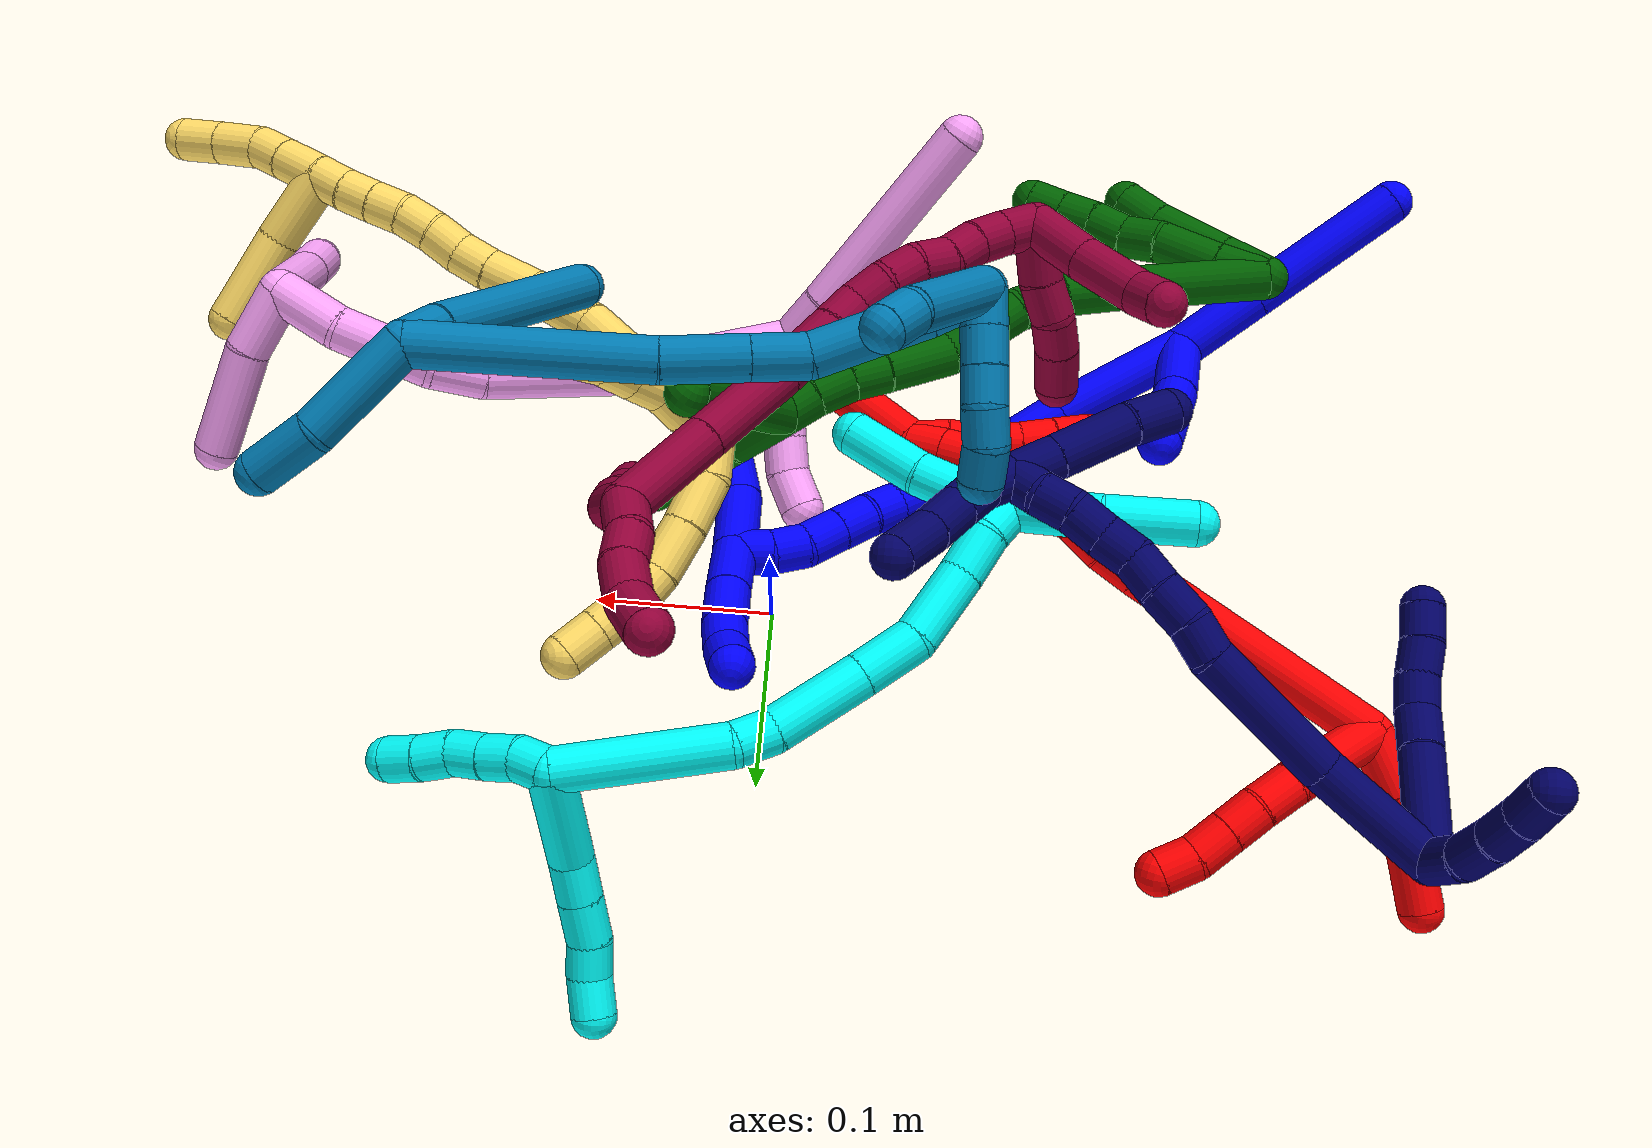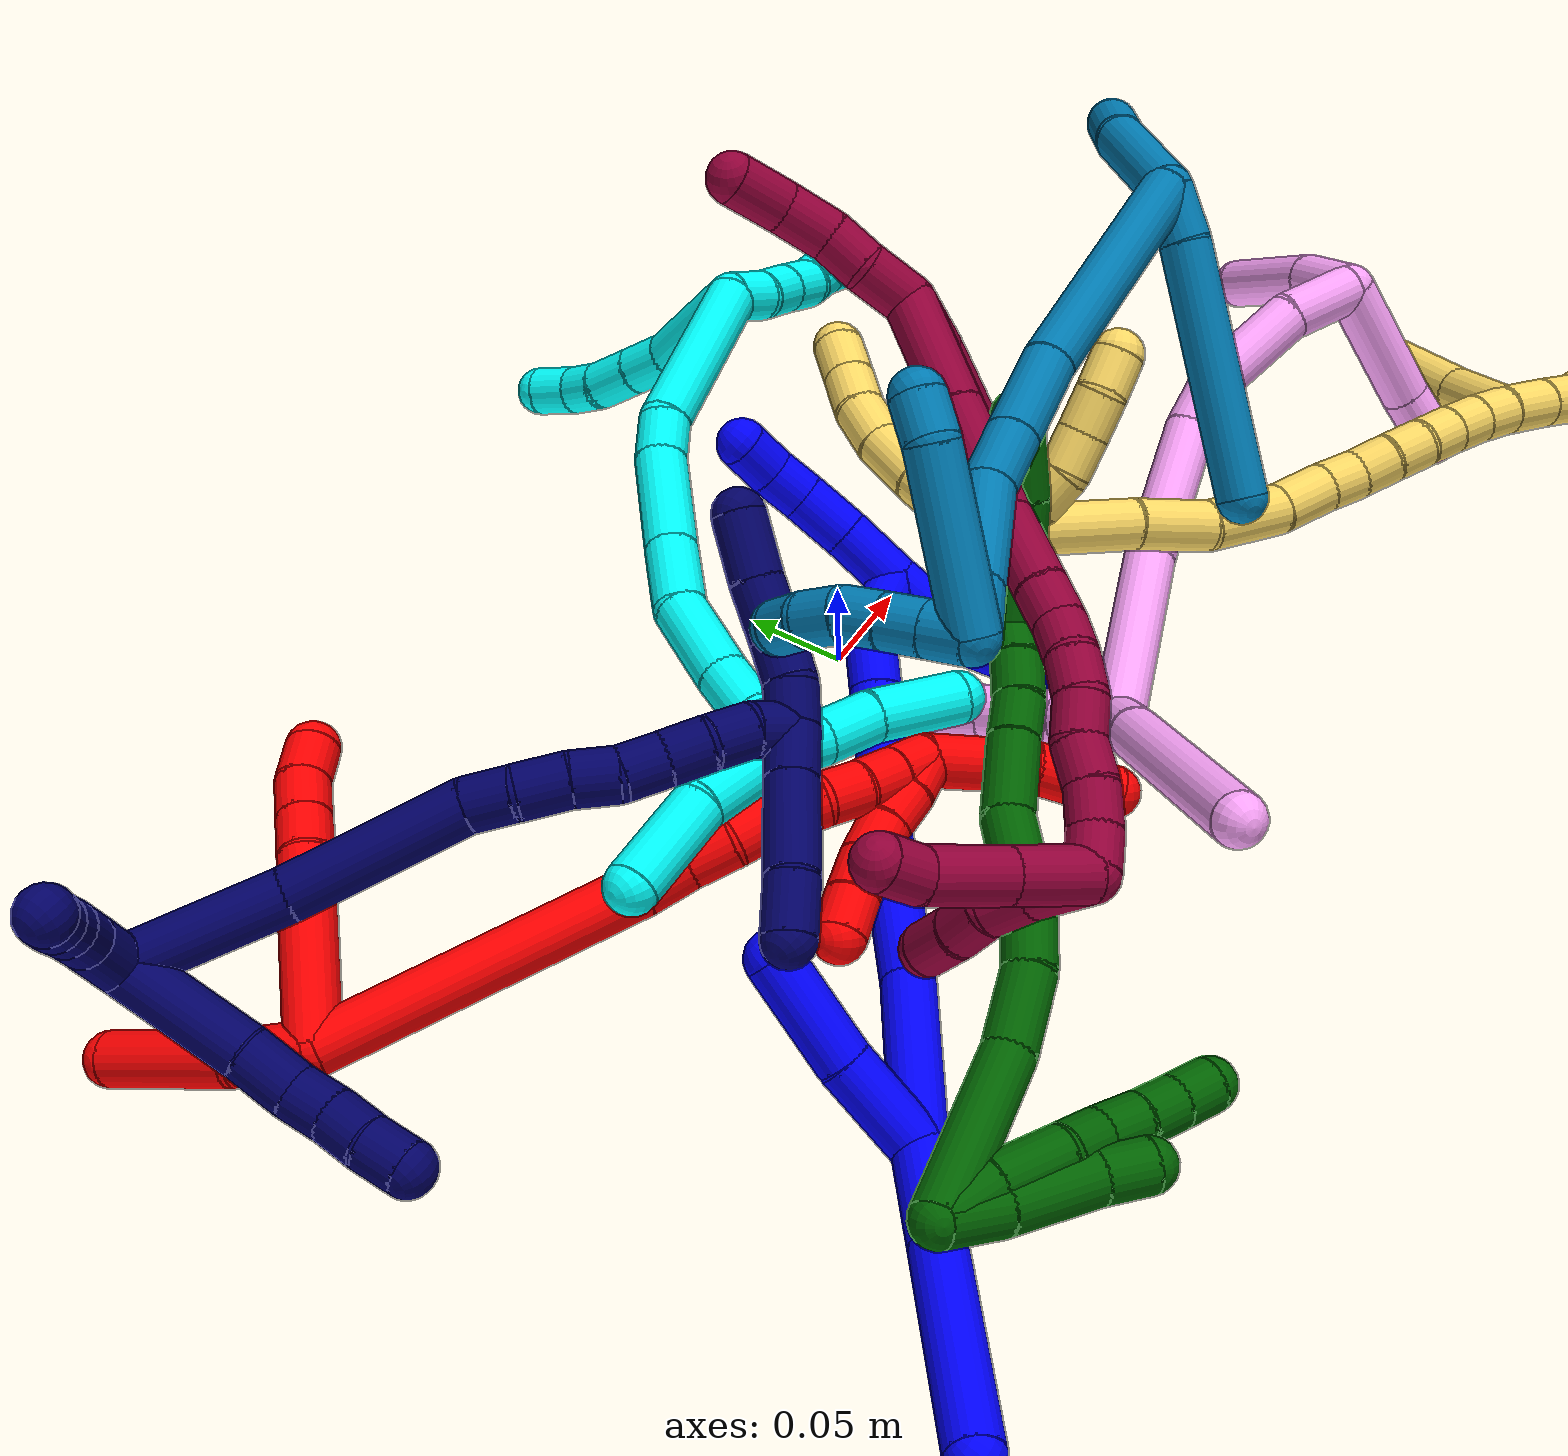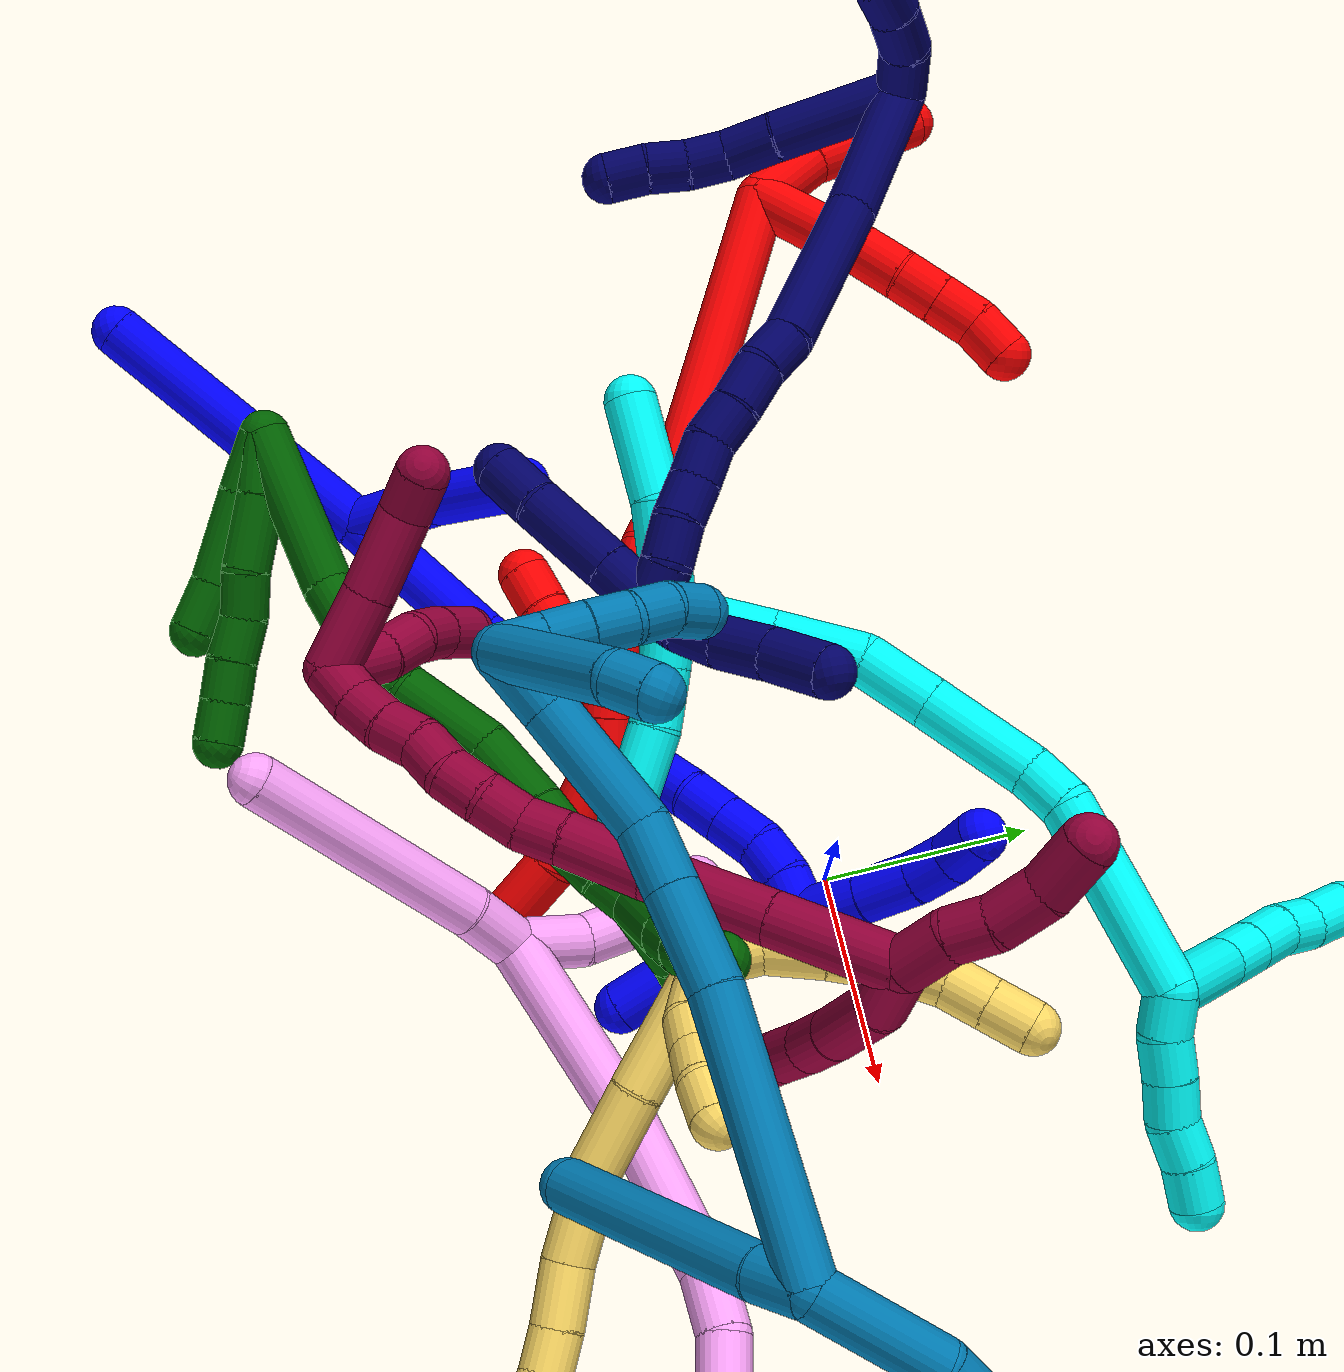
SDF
<sdf version="1.7">
 <world name="default">
  <plugin name="TubeGeneratorPlugin" filename="libtube_generator_plugin.so"/>
  <model name="photoneo_s_sensor">
   <static>1</static>
   <pose>0 0 2 1.57079 1.57079 3.14159</pose>
   <link name="link">
    <inertial><mass>0.1</mass></inertial>
    <sensor name="sensor" type="depth">
     <update_rate>30</update_rate>
     <camera>
      <horizontal_fov>1.22</horizontal_fov>
      <image><width>1920</width><height>1200</height><format>B8G8R8</format></image>
      <clip><near>0.1</near><far>4</far></clip>
      <depth_camera><output>points</output></depth_camera>
     </camera>
     <plugin name="camera_plugin" filename="libgazebo_ros_depth_camera.so">
      <baseline>0.2</baseline>
      <alwaysOn>1</alwaysOn>
      <updateRate>0.0</updateRate>
      <cameraName>camera_ir</cameraName>
      <imageTopicName>/camera/color/image_raw</imageTopicName>
      <cameraInfoTopicName>/camera/color/camera_info</cameraInfoTopicName>
      <depthImageTopicName>/camera/depth/image_raw</depthImageTopicName>
      <depthImageCameraInfoTopicName>/camera/depth/camera_info</depthImageCameraInfoTopicName>
      <pointCloudTopicName>/camera/depth/points</pointCloudTopicName>
      <frameName>fr_optical</frameName>
      <pointCloudCutoff>0.1</pointCloudCutoff>
      <pointCloudCutoffMax>2.0</pointCloudCutoffMax>
      <distortionK1>0</distortionK1>
      <distortionK2>0</distortionK2>
      <distortionK3>0</distortionK3>
      <distortionT1>0</distortionT1>
      <distortionT2>0</distortionT2>
      <CxPrime>0</CxPrime>
      <Cx>0</Cx>
      <Cy>0</Cy>
      <focalLength>0</focalLength>
      <hackBaseline>0</hackBaseline>
     </plugin>
    </sensor>
   </link>
  </model>
  <gravity>0 0 -9.8</gravity>
  <magnetic_field>6e-06 2.3e-05 -4.2e-05</magnetic_field>
  <atmosphere type="adiabatic"/>
  <physics name="default_physics" default="0" type="ode">
   <max_step_size>0.003</max_step_size>
   <real_time_factor>1</real_time_factor>
   <real_time_update_rate>1000</real_time_update_rate>
   <max_contacts>10000</max_contacts>
   <ode>
    <solver>
     <type>quick</type>
     <iters>100</iters>
     <sor>1.3</sor>
     <use_dynamic_moi_rescaling>0</use_dynamic_moi_rescaling>
    </solver>
    <constraints>
     <contact_max_correcting_vel>0</contact_max_correcting_vel>
     <contact_surface_layer>0.001</contact_surface_layer>
     <cfm>0</cfm>
     <erp>0.2</erp>
    </constraints>
   </ode>
  </physics>
  <scene><ambient>0.4 0.4 0.4 1</ambient><background>0.7 0.7 0.7 1</background><shadows>0</shadows></scene>
  <audio><device>default</device></audio>
  <spherical_coordinates>
   <surface_model>EARTH_WGS84</surface_model>
   <latitude_deg>0</latitude_deg>
   <longitude_deg>0</longitude_deg>
   <elevation>0</elevation>
   <heading_deg>0</heading_deg>
  </spherical_coordinates>
  <model name="bin">
   <static>1</static>
   <link name="bottom">
    <collision name="collision-bottom">
     <pose>0 0 -0.01 0 -0 0</pose>
     <geometry><box><size>0.8 0.6 0.02</size></box></geometry>
     <surface>
      <friction><ode><mu>100</mu><mu2>100</mu2></ode></friction>
      <contact><collide_bitmask>65535</collide_bitmask></contact>
     </surface>
    </collision>
   </link>
   <link name="west_wall">
    <collision name="collision-west_wall">
     <pose>-0.41 0 0.1 0 -0 0</pose>
     <geometry><box><size>0.02 0.6 0.2</size></box></geometry>
     <surface>
      <friction><ode><mu>100</mu><mu2>100</mu2></ode></friction>
      <contact><collide_bitmask>65535</collide_bitmask></contact>
     </surface>
    </collision>
   </link>
   <link name="east_wall">
    <collision name="collision-east_wall">
     <pose>0.41 0 0.1 0 -0 0</pose>
     <geometry><box><size>0.02 0.6 0.2</size></box></geometry>
     <surface>
      <friction><ode><mu>100</mu><mu2>100</mu2></ode></friction>
      <contact><collide_bitmask>65535</collide_bitmask></contact>
     </surface>
    </collision>
   </link>
   <link name="south_wall">
    <collision name="collision-south_wall">
     <pose>0 -0.31 0.1 0 -0 0</pose>
     <geometry><box><size>0.8 0.02 0.2</size></box></geometry>
     <surface>
      <friction><ode><mu>100</mu><mu2>100</mu2></ode></friction>
      <contact><collide_bitmask>65535</collide_bitmask></contact>
     </surface>
    </collision>
   </link>
   <link name="north_wall">
    <collision name="collision-north_wall">
     <pose>0 0.31 0.1 0 -0 0</pose>
     <geometry><box><size>0.8 0.02 0.2</size></box></geometry>
     <surface>
      <friction><ode><mu>100</mu><mu2>100</mu2></ode></friction>
      <contact><collide_bitmask>65535</collide_bitmask></contact>
     </surface>
    </collision>
   </link>
  </model>
  <model name="1">
   <static>0</static>
   <link name="1">
    <collision name="collision-cylinder-e_1_2_8">
     <pose>-0.017516 -0.015907 0.010958 0.96757 -0.736555 -0.400086</pose>
     <geometry><cylinder><radius>0.0125</radius><length>0.05215</length></cylinder></geometry>
     <surface>
      <friction><ode><mu>1.16</mu><mu2>1.16</mu2><slip1>0</slip1><slip2>0</slip2></ode></friction>
      <contact><ode><kp>1e+06</kp><kd>1</kd><max_vel>0</max_vel><min_depth>0.001</min_depth></ode></contact>
     </surface>
    </collision>
    <visual name="visual-cylinder-e_1_2_8">
     <pose>-0.017516 -0.015907 0.010958 0.96757 -0.736555 -0.400086</pose>
     <geometry><cylinder><radius>0.0125</radius><length>0.05215</length></cylinder></geometry>
     <material><ambient>0 0 1 1</ambient></material>
    </visual>
    <collision name="collision-cylinder-e_2_8_6">
     <pose>-0.06829 -0.061553 0.041992 0.977001 -0.747485 -0.41097</pose>
     <geometry><cylinder><radius>0.0125</radius><length>0.09785</length></cylinder></geometry>
     <surface>
      <friction><ode><mu>1.16</mu><mu2>1.16</mu2><slip1>0</slip1><slip2>0</slip2></ode></friction>
      <contact><ode><kp>1e+06</kp><kd>1</kd><max_vel>0</max_vel><min_depth>0.001</min_depth></ode></contact>
     </surface>
    </collision>
    <visual name="visual-cylinder-e_2_8_6">
     <pose>-0.06829 -0.061553 0.041992 0.977001 -0.747485 -0.41097</pose>
     <geometry><cylinder><radius>0.0125</radius><length>0.09785</length></cylinder></geometry>
     <material><ambient>0 0 1 1</ambient></material>
    </visual>
    <collision name="collision-cylinder-e_1_2_9">
     <pose>0.000178 0.003471 -0.023557 -2.99528 0.007477 -0.101935</pose>
     <geometry><cylinder><radius>0.0125</radius><length>0.047624</length></cylinder></geometry>
     <surface>
      <friction><ode><mu>1.16</mu><mu2>1.16</mu2><slip1>0</slip1><slip2>0</slip2></ode></friction>
      <contact><ode><kp>1e+06</kp><kd>1</kd><max_vel>0</max_vel><min_depth>0.001</min_depth></ode></contact>
     </surface>
    </collision>
    <visual name="visual-cylinder-e_1_2_9">
     <pose>0.000178 0.003471 -0.023557 -2.99528 0.007477 -0.101935</pose>
     <geometry><cylinder><radius>0.0125</radius><length>0.047624</length></cylinder></geometry>
     <material><ambient>0 0 1 1</ambient></material>
    </visual>
    <collision name="collision-cylinder-e_2_9_5">
     <pose>0.000384 0.013724 -0.072408 -2.87967 0.001083 -0.008225</pose>
     <geometry><cylinder><radius>0.0125</radius><length>0.052376</length></cylinder></geometry>
     <surface>
      <friction><ode><mu>1.16</mu><mu2>1.16</mu2><slip1>0</slip1><slip2>0</slip2></ode></friction>
      <contact><ode><kp>1e+06</kp><kd>1</kd><max_vel>0</max_vel><min_depth>0.001</min_depth></ode></contact>
     </surface>
    </collision>
    <visual name="visual-cylinder-e_2_9_5">
     <pose>0.000384 0.013724 -0.072408 -2.87967 0.001083 -0.008225</pose>
     <geometry><cylinder><radius>0.0125</radius><length>0.052376</length></cylinder></geometry>
     <material><ambient>0 0 1 1</ambient></material>
    </visual>
    <collision name="collision-cylinder-e_1_2_10">
     <pose>0.022192 0.029916 -0.018893 -2.13407 0.560178 -0.961979</pose>
     <geometry><cylinder><radius>0.0125</radius><length>0.083531</length></cylinder></geometry>
     <surface>
      <friction><ode><mu>1.16</mu><mu2>1.16</mu2><slip1>0</slip1><slip2>0</slip2></ode></friction>
      <contact><ode><kp>1e+06</kp><kd>1</kd><max_vel>0</max_vel><min_depth>0.001</min_depth></ode></contact>
     </surface>
    </collision>
    <visual name="visual-cylinder-e_1_2_10">
     <pose>0.022192 0.029916 -0.018893 -2.13407 0.560178 -0.961979</pose>
     <geometry><cylinder><radius>0.0125</radius><length>0.083531</length></cylinder></geometry>
     <material><ambient>0 0 1 1</ambient></material>
    </visual>
    <collision name="collision-cylinder-e_2_10_11">
     <pose>0.065736 0.087653 -0.059073 -2.22394 0.547401 -1.03361</pose>
     <geometry><cylinder><radius>0.0125</radius><length>0.082053</length></cylinder></geometry>
     <surface>
      <friction><ode><mu>1.16</mu><mu2>1.16</mu2><slip1>0</slip1><slip2>0</slip2></ode></friction>
      <contact><ode><kp>1e+06</kp><kd>1</kd><max_vel>0</max_vel><min_depth>0.001</min_depth></ode></contact>
     </surface>
    </collision>
    <visual name="visual-cylinder-e_2_10_11">
     <pose>0.065736 0.087653 -0.059073 -2.22394 0.547401 -1.03361</pose>
     <geometry><cylinder><radius>0.0125</radius><length>0.082053</length></cylinder></geometry>
     <material><ambient>0 0 1 1</ambient></material>
    </visual>
    <collision name="collision-cylinder-e_3_11_12">
     <pose>0.092022 0.127367 -0.088743 -2.18471 0.32692 -0.615797</pose>
     <geometry><cylinder><radius>0.0125</radius><length>0.030725</length></cylinder></geometry>
     <surface>
      <friction><ode><mu>1.16</mu><mu2>1.16</mu2><slip1>0</slip1><slip2>0</slip2></ode></friction>
      <contact><ode><kp>1e+06</kp><kd>1</kd><max_vel>0</max_vel><min_depth>0.001</min_depth></ode></contact>
     </surface>
    </collision>
    <visual name="visual-cylinder-e_3_11_12">
     <pose>0.092022 0.127367 -0.088743 -2.18471 0.32692 -0.615797</pose>
     <geometry><cylinder><radius>0.0125</radius><length>0.030725</length></cylinder></geometry>
     <material><ambient>0 0 1 1</ambient></material>
    </visual>
    <collision name="collision-cylinder-e_4_12_13">
     <pose>0.098087 0.146701 -0.103894 -2.30896 0.111927 -0.252056</pose>
     <geometry><cylinder><radius>0.0125</radius><length>0.020249</length></cylinder></geometry>
     <surface>
      <friction><ode><mu>1.16</mu><mu2>1.16</mu2><slip1>0</slip1><slip2>0</slip2></ode></friction>
      <contact><ode><kp>1e+06</kp><kd>1</kd><max_vel>0</max_vel><min_depth>0.001</min_depth></ode></contact>
     </surface>
    </collision>
    <visual name="visual-cylinder-e_4_12_13">
     <pose>0.098087 0.146701 -0.103894 -2.30896 0.111927 -0.252056</pose>
     <geometry><cylinder><radius>0.0125</radius><length>0.020249</length></cylinder></geometry>
     <material><ambient>0 0 1 1</ambient></material>
    </visual>
    <collision name="collision-cylinder-e_5_13_14">
     <pose>0.102333 0.161938 -0.117103 -2.26124 0.298958 -0.61896</pose>
     <geometry><cylinder><radius>0.0125</radius><length>0.021158</length></cylinder></geometry>
     <surface>
      <friction><ode><mu>1.16</mu><mu2>1.16</mu2><slip1>0</slip1><slip2>0</slip2></ode></friction>
      <contact><ode><kp>1e+06</kp><kd>1</kd><max_vel>0</max_vel><min_depth>0.001</min_depth></ode></contact>
     </surface>
    </collision>
    <visual name="visual-cylinder-e_5_13_14">
     <pose>0.102333 0.161938 -0.117103 -2.26124 0.298958 -0.61896</pose>
     <geometry><cylinder><radius>0.0125</radius><length>0.021158</length></cylinder></geometry>
     <material><ambient>0 0 1 1</ambient></material>
    </visual>
    <collision name="collision-cylinder-e_6_14_15">
     <pose>0.108758 0.177846 -0.130286 -2.26429 0.303878 -0.63097</pose>
     <geometry><cylinder><radius>0.0125</radius><length>0.022114</length></cylinder></geometry>
     <surface>
      <friction><ode><mu>1.16</mu><mu2>1.16</mu2><slip1>0</slip1><slip2>0</slip2></ode></friction>
      <contact><ode><kp>1e+06</kp><kd>1</kd><max_vel>0</max_vel><min_depth>0.001</min_depth></ode></contact>
     </surface>
    </collision>
    <visual name="visual-cylinder-e_6_14_15">
     <pose>0.108758 0.177846 -0.130286 -2.26429 0.303878 -0.63097</pose>
     <geometry><cylinder><radius>0.0125</radius><length>0.022114</length></cylinder></geometry>
     <material><ambient>0 0 1 1</ambient></material>
    </visual>
    <collision name="collision-cylinder-e_7_15_16">
     <pose>0.114678 0.19485 -0.140872 -1.97871 0.263448 -0.397849</pose>
     <geometry><cylinder><radius>0.0125</radius><length>0.020063</length></cylinder></geometry>
     <surface>
      <friction><ode><mu>1.16</mu><mu2>1.16</mu2><slip1>0</slip1><slip2>0</slip2></ode></friction>
      <contact><ode><kp>1e+06</kp><kd>1</kd><max_vel>0</max_vel><min_depth>0.001</min_depth></ode></contact>
     </surface>
    </collision>
    <visual name="visual-cylinder-e_7_15_16">
     <pose>0.114678 0.19485 -0.140872 -1.97871 0.263448 -0.397849</pose>
     <geometry><cylinder><radius>0.0125</radius><length>0.020063</length></cylinder></geometry>
     <material><ambient>0 0 1 1</ambient></material>
    </visual>
    <collision name="collision-cylinder-e_8_16_1">
     <pose>0.119567 0.213383 -0.14642 -1.74588 0.228389 -0.271839</pose>
     <geometry><cylinder><radius>0.0125</radius><length>0.020107</length></cylinder></geometry>
     <surface>
      <friction><ode><mu>1.16</mu><mu2>1.16</mu2><slip1>0</slip1><slip2>0</slip2></ode></friction>
      <contact><ode><kp>1e+06</kp><kd>1</kd><max_vel>0</max_vel><min_depth>0.001</min_depth></ode></contact>
     </surface>
    </collision>
    <visual name="visual-cylinder-e_8_16_1">
     <pose>0.119567 0.213383 -0.14642 -1.74588 0.228389 -0.271839</pose>
     <geometry><cylinder><radius>0.0125</radius><length>0.020107</length></cylinder></geometry>
     <material><ambient>0 0 1 1</ambient></material>
    </visual>
    <collision name="collision-cylinder-e_1_1_17">
     <pose>0.121469 0.22319 -0.125755 -0.007333 -0.016724 6.1e-05</pose>
     <geometry><cylinder><radius>0.0125</radius><length>0.04475</length></cylinder></geometry>
     <surface>
      <friction><ode><mu>1.16</mu><mu2>1.16</mu2><slip1>0</slip1><slip2>0</slip2></ode></friction>
      <contact><ode><kp>1e+06</kp><kd>1</kd><max_vel>0</max_vel><min_depth>0.001</min_depth></ode></contact>
     </surface>
    </collision>
    <visual name="visual-cylinder-e_1_1_17">
     <pose>0.121469 0.22319 -0.125755 -0.007333 -0.016724 6.1e-05</pose>
     <geometry><cylinder><radius>0.0125</radius><length>0.04475</length></cylinder></geometry>
     <material><ambient>0 0 1 1</ambient></material>
    </visual>
    <collision name="collision-cylinder-e_2_17_4">
     <pose>0.11642 0.231851 -0.077517 -0.317363 -0.170048 0.027276</pose>
     <geometry><cylinder><radius>0.0125</radius><length>0.05525</length></cylinder></geometry>
     <surface>
      <friction><ode><mu>1.16</mu><mu2>1.16</mu2><slip1>0</slip1><slip2>0</slip2></ode></friction>
      <contact><ode><kp>1e+06</kp><kd>1</kd><max_vel>0</max_vel><min_depth>0.001</min_depth></ode></contact>
     </surface>
    </collision>
    <visual name="visual-cylinder-e_2_17_4">
     <pose>0.11642 0.231851 -0.077517 -0.317363 -0.170048 0.027276</pose>
     <geometry><cylinder><radius>0.0125</radius><length>0.05525</length></cylinder></geometry>
     <material><ambient>0 0 1 1</ambient></material>
    </visual>
    <collision name="collision-cylinder-e_1_1_18">
     <pose>0.122066 0.223732 -0.164499 -3.09848 0.013572 -0.609798</pose>
     <geometry><cylinder><radius>0.0125</radius><length>0.032778</length></cylinder></geometry>
     <surface>
      <friction><ode><mu>1.16</mu><mu2>1.16</mu2><slip1>0</slip1><slip2>0</slip2></ode></friction>
      <contact><ode><kp>1e+06</kp><kd>1</kd><max_vel>0</max_vel><min_depth>0.001</min_depth></ode></contact>
     </surface>
    </collision>
    <visual name="visual-cylinder-e_1_1_18">
     <pose>0.122066 0.223732 -0.164499 -3.09848 0.013572 -0.609798</pose>
     <geometry><cylinder><radius>0.0125</radius><length>0.032778</length></cylinder></geometry>
     <material><ambient>0 0 1 1</ambient></material>
    </visual>
    <collision name="collision-cylinder-e_2_18_19">
     <pose>0.122549 0.224367 -0.194387 3.13627 0.019335 2.60448</pose>
     <geometry><cylinder><radius>0.0125</radius><length>0.027038</length></cylinder></geometry>
     <surface>
      <friction><ode><mu>1.16</mu><mu2>1.16</mu2><slip1>0</slip1><slip2>0</slip2></ode></friction>
      <contact><ode><kp>1e+06</kp><kd>1</kd><max_vel>0</max_vel><min_depth>0.001</min_depth></ode></contact>
     </surface>
    </collision>
    <visual name="visual-cylinder-e_2_18_19">
     <pose>0.122549 0.224367 -0.194387 3.13627 0.019335 2.60448</pose>
     <geometry><cylinder><radius>0.0125</radius><length>0.027038</length></cylinder></geometry>
     <material><ambient>0 0 1 1</ambient></material>
    </visual>
    <collision name="collision-cylinder-e_3_19_20">
     <pose>0.121604 0.223399 -0.217812 3.05139 -0.120728 -1.8588</pose>
     <geometry><cylinder><radius>0.0125</radius><length>0.020044</length></cylinder></geometry>
     <surface>
      <friction><ode><mu>1.16</mu><mu2>1.16</mu2><slip1>0</slip1><slip2>0</slip2></ode></friction>
      <contact><ode><kp>1e+06</kp><kd>1</kd><max_vel>0</max_vel><min_depth>0.001</min_depth></ode></contact>
     </surface>
    </collision>
    <visual name="visual-cylinder-e_3_19_20">
     <pose>0.121604 0.223399 -0.217812 3.05139 -0.120728 -1.8588</pose>
     <geometry><cylinder><radius>0.0125</radius><length>0.020044</length></cylinder></geometry>
     <material><ambient>0 0 1 1</ambient></material>
    </visual>
    <collision name="collision-cylinder-e_4_20_3">
     <pose>0.116711 0.221653 -0.237053 3.05077 -0.374688 -2.67104</pose>
     <geometry><cylinder><radius>0.0125</radius><length>0.02014</length></cylinder></geometry>
     <surface>
      <friction><ode><mu>1.16</mu><mu2>1.16</mu2><slip1>0</slip1><slip2>0</slip2></ode></friction>
      <contact><ode><kp>1e+06</kp><kd>1</kd><max_vel>0</max_vel><min_depth>0.001</min_depth></ode></contact>
     </surface>
    </collision>
    <visual name="visual-cylinder-e_4_20_3">
     <pose>0.116711 0.221653 -0.237053 3.05077 -0.374688 -2.67104</pose>
     <geometry><cylinder><radius>0.0125</radius><length>0.02014</length></cylinder></geometry>
     <material><ambient>0 0 1 1</ambient></material>
    </visual>
    <collision name="collision-sphere-3">
     <pose>0.113026 0.220803 -0.246386 0 -0 0</pose>
     <geometry><sphere><radius>0.0125</radius></sphere></geometry>
     <surface>
      <friction><ode><mu>1.16</mu><mu2>1.16</mu2><slip1>0</slip1><slip2>0</slip2></ode></friction>
      <contact><ode><kp>1e+06</kp><kd>1</kd><max_vel>0</max_vel><min_depth>0.001</min_depth></ode></contact>
     </surface>
    </collision>
    <visual name="visual-sphere-3">
     <pose>0.113026 0.220803 -0.246386 0 -0 0</pose>
     <geometry><sphere><radius>0.0125</radius></sphere></geometry>
     <material><ambient>0 0 1 1</ambient></material>
    </visual>
    <collision name="collision-sphere-20">
     <pose>0.120397 0.222503 -0.227721 0 -0 0</pose>
     <geometry><sphere><radius>0.0125</radius></sphere></geometry>
     <surface>
      <friction><ode><mu>1.16</mu><mu2>1.16</mu2><slip1>0</slip1><slip2>0</slip2></ode></friction>
      <contact><ode><kp>1e+06</kp><kd>1</kd><max_vel>0</max_vel><min_depth>0.001</min_depth></ode></contact>
     </surface>
    </collision>
    <visual name="visual-sphere-20">
     <pose>0.120397 0.222503 -0.227721 0 -0 0</pose>
     <geometry><sphere><radius>0.0125</radius></sphere></geometry>
     <material><ambient>0 0 1 1</ambient></material>
    </visual>
    <collision name="collision-sphere-19">
     <pose>0.122811 0.224295 -0.207904 0 -0 0</pose>
     <geometry><sphere><radius>0.0125</radius></sphere></geometry>
     <surface>
      <friction><ode><mu>1.16</mu><mu2>1.16</mu2><slip1>0</slip1><slip2>0</slip2></ode></friction>
      <contact><ode><kp>1e+06</kp><kd>1</kd><max_vel>0</max_vel><min_depth>0.001</min_depth></ode></contact>
     </surface>
    </collision>
    <visual name="visual-sphere-19">
     <pose>0.122811 0.224295 -0.207904 0 -0 0</pose>
     <geometry><sphere><radius>0.0125</radius></sphere></geometry>
     <material><ambient>0 0 1 1</ambient></material>
    </visual>
    <collision name="collision-sphere-10">
     <pose>0.044383 0.059832 -0.037785 0 -0 0</pose>
     <geometry><sphere><radius>0.0125</radius></sphere></geometry>
     <surface>
      <friction><ode><mu>1.16</mu><mu2>1.16</mu2><slip1>0</slip1><slip2>0</slip2></ode></friction>
      <contact><ode><kp>1e+06</kp><kd>1</kd><max_vel>0</max_vel><min_depth>0.001</min_depth></ode></contact>
     </surface>
    </collision>
    <visual name="visual-sphere-10">
     <pose>0.044383 0.059832 -0.037785 0 -0 0</pose>
     <geometry><sphere><radius>0.0125</radius></sphere></geometry>
     <material><ambient>0 0 1 1</ambient></material>
    </visual>
    <collision name="collision-sphere-5">
     <pose>0.000413 0.020505 -0.097703 0 -0 0</pose>
     <geometry><sphere><radius>0.0125</radius></sphere></geometry>
     <surface>
      <friction><ode><mu>1.16</mu><mu2>1.16</mu2><slip1>0</slip1><slip2>0</slip2></ode></friction>
      <contact><ode><kp>1e+06</kp><kd>1</kd><max_vel>0</max_vel><min_depth>0.001</min_depth></ode></contact>
     </surface>
    </collision>
    <visual name="visual-sphere-5">
     <pose>0.000413 0.020505 -0.097703 0 -0 0</pose>
     <geometry><sphere><radius>0.0125</radius></sphere></geometry>
     <material><ambient>0 0 1 1</ambient></material>
    </visual>
    <collision name="collision-sphere-6">
     <pose>-0.101549 -0.091293 0.062068 0 -0 0</pose>
     <geometry><sphere><radius>0.0125</radius></sphere></geometry>
     <surface>
      <friction><ode><mu>1.16</mu><mu2>1.16</mu2><slip1>0</slip1><slip2>0</slip2></ode></friction>
      <contact><ode><kp>1e+06</kp><kd>1</kd><max_vel>0</max_vel><min_depth>0.001</min_depth></ode></contact>
     </surface>
    </collision>
    <visual name="visual-sphere-6">
     <pose>-0.101549 -0.091293 0.062068 0 -0 0</pose>
     <geometry><sphere><radius>0.0125</radius></sphere></geometry>
     <material><ambient>0 0 1 1</ambient></material>
    </visual>
    <collision name="collision-sphere-9">
     <pose>0.000356 0.006943 -0.047113 0 -0 0</pose>
     <geometry><sphere><radius>0.0125</radius></sphere></geometry>
     <surface>
      <friction><ode><mu>1.16</mu><mu2>1.16</mu2><slip1>0</slip1><slip2>0</slip2></ode></friction>
      <contact><ode><kp>1e+06</kp><kd>1</kd><max_vel>0</max_vel><min_depth>0.001</min_depth></ode></contact>
     </surface>
    </collision>
    <visual name="visual-sphere-9">
     <pose>0.000356 0.006943 -0.047113 0 -0 0</pose>
     <geometry><sphere><radius>0.0125</radius></sphere></geometry>
     <material><ambient>0 0 1 1</ambient></material>
    </visual>
    <collision name="collision-sphere-2">
     <geometry><sphere><radius>0.0125</radius></sphere></geometry>
     <surface>
      <friction><ode><mu>1.16</mu><mu2>1.16</mu2><slip1>0</slip1><slip2>0</slip2></ode></friction>
      <contact><ode><kp>1e+06</kp><kd>1</kd><max_vel>0</max_vel><min_depth>0.001</min_depth></ode></contact>
     </surface>
    </collision>
    <visual name="visual-sphere-2">
     <geometry><sphere><radius>0.0125</radius></sphere></geometry>
     <material><ambient>0 0 1 1</ambient></material>
    </visual>
    <collision name="collision-sphere-8">
     <pose>-0.035031 -0.031814 0.021916 0 -0 0</pose>
     <geometry><sphere><radius>0.0125</radius></sphere></geometry>
     <surface>
      <friction><ode><mu>1.16</mu><mu2>1.16</mu2><slip1>0</slip1><slip2>0</slip2></ode></friction>
      <contact><ode><kp>1e+06</kp><kd>1</kd><max_vel>0</max_vel><min_depth>0.001</min_depth></ode></contact>
     </surface>
    </collision>
    <visual name="visual-sphere-8">
     <pose>-0.035031 -0.031814 0.021916 0 -0 0</pose>
     <geometry><sphere><radius>0.0125</radius></sphere></geometry>
     <material><ambient>0 0 1 1</ambient></material>
    </visual>
    <collision name="collision-sphere-11">
     <pose>0.087089 0.115474 -0.080361 0 -0 0</pose>
     <geometry><sphere><radius>0.0125</radius></sphere></geometry>
     <surface>
      <friction><ode><mu>1.16</mu><mu2>1.16</mu2><slip1>0</slip1><slip2>0</slip2></ode></friction>
      <contact><ode><kp>1e+06</kp><kd>1</kd><max_vel>0</max_vel><min_depth>0.001</min_depth></ode></contact>
     </surface>
    </collision>
    <visual name="visual-sphere-11">
     <pose>0.087089 0.115474 -0.080361 0 -0 0</pose>
     <geometry><sphere><radius>0.0125</radius></sphere></geometry>
     <material><ambient>0 0 1 1</ambient></material>
    </visual>
    <collision name="collision-sphere-12">
     <pose>0.096956 0.139259 -0.097124 0 -0 0</pose>
     <geometry><sphere><radius>0.0125</radius></sphere></geometry>
     <surface>
      <friction><ode><mu>1.16</mu><mu2>1.16</mu2><slip1>0</slip1><slip2>0</slip2></ode></friction>
      <contact><ode><kp>1e+06</kp><kd>1</kd><max_vel>0</max_vel><min_depth>0.001</min_depth></ode></contact>
     </surface>
    </collision>
    <visual name="visual-sphere-12">
     <pose>0.096956 0.139259 -0.097124 0 -0 0</pose>
     <geometry><sphere><radius>0.0125</radius></sphere></geometry>
     <material><ambient>0 0 1 1</ambient></material>
    </visual>
    <collision name="collision-sphere-13">
     <pose>0.099217 0.154143 -0.110664 0 -0 0</pose>
     <geometry><sphere><radius>0.0125</radius></sphere></geometry>
     <surface>
      <friction><ode><mu>1.16</mu><mu2>1.16</mu2><slip1>0</slip1><slip2>0</slip2></ode></friction>
      <contact><ode><kp>1e+06</kp><kd>1</kd><max_vel>0</max_vel><min_depth>0.001</min_depth></ode></contact>
     </surface>
    </collision>
    <visual name="visual-sphere-13">
     <pose>0.099217 0.154143 -0.110664 0 -0 0</pose>
     <geometry><sphere><radius>0.0125</radius></sphere></geometry>
     <material><ambient>0 0 1 1</ambient></material>
    </visual>
    <collision name="collision-sphere-14">
     <pose>0.105449 0.169732 -0.123542 0 -0 0</pose>
     <geometry><sphere><radius>0.0125</radius></sphere></geometry>
     <surface>
      <friction><ode><mu>1.16</mu><mu2>1.16</mu2><slip1>0</slip1><slip2>0</slip2></ode></friction>
      <contact><ode><kp>1e+06</kp><kd>1</kd><max_vel>0</max_vel><min_depth>0.001</min_depth></ode></contact>
     </surface>
    </collision>
    <visual name="visual-sphere-14">
     <pose>0.105449 0.169732 -0.123542 0 -0 0</pose>
     <geometry><sphere><radius>0.0125</radius></sphere></geometry>
     <material><ambient>0 0 1 1</ambient></material>
    </visual>
    <collision name="collision-sphere-15">
     <pose>0.112066 0.185959 -0.13703 0 -0 0</pose>
     <geometry><sphere><radius>0.0125</radius></sphere></geometry>
     <surface>
      <friction><ode><mu>1.16</mu><mu2>1.16</mu2><slip1>0</slip1><slip2>0</slip2></ode></friction>
      <contact><ode><kp>1e+06</kp><kd>1</kd><max_vel>0</max_vel><min_depth>0.001</min_depth></ode></contact>
     </surface>
    </collision>
    <visual name="visual-sphere-15">
     <pose>0.112066 0.185959 -0.13703 0 -0 0</pose>
     <geometry><sphere><radius>0.0125</radius></sphere></geometry>
     <material><ambient>0 0 1 1</ambient></material>
    </visual>
    <collision name="collision-sphere-16">
     <pose>0.117291 0.20374 -0.144715 0 -0 0</pose>
     <geometry><sphere><radius>0.0125</radius></sphere></geometry>
     <surface>
      <friction><ode><mu>1.16</mu><mu2>1.16</mu2><slip1>0</slip1><slip2>0</slip2></ode></friction>
      <contact><ode><kp>1e+06</kp><kd>1</kd><max_vel>0</max_vel><min_depth>0.001</min_depth></ode></contact>
     </surface>
    </collision>
    <visual name="visual-sphere-16">
     <pose>0.117291 0.20374 -0.144715 0 -0 0</pose>
     <geometry><sphere><radius>0.0125</radius></sphere></geometry>
     <material><ambient>0 0 1 1</ambient></material>
    </visual>
    <collision name="collision-sphere-1">
     <pose>0.121843 0.223026 -0.148126 0 -0 0</pose>
     <geometry><sphere><radius>0.0125</radius></sphere></geometry>
     <surface>
      <friction><ode><mu>1.16</mu><mu2>1.16</mu2><slip1>0</slip1><slip2>0</slip2></ode></friction>
      <contact><ode><kp>1e+06</kp><kd>1</kd><max_vel>0</max_vel><min_depth>0.001</min_depth></ode></contact>
     </surface>
    </collision>
    <visual name="visual-sphere-1">
     <pose>0.121843 0.223026 -0.148126 0 -0 0</pose>
     <geometry><sphere><radius>0.0125</radius></sphere></geometry>
     <material><ambient>0 0 1 1</ambient></material>
    </visual>
    <collision name="collision-sphere-18">
     <pose>0.122288 0.224439 -0.180871 0 -0 0</pose>
     <geometry><sphere><radius>0.0125</radius></sphere></geometry>
     <surface>
      <friction><ode><mu>1.16</mu><mu2>1.16</mu2><slip1>0</slip1><slip2>0</slip2></ode></friction>
      <contact><ode><kp>1e+06</kp><kd>1</kd><max_vel>0</max_vel><min_depth>0.001</min_depth></ode></contact>
     </surface>
    </collision>
    <visual name="visual-sphere-18">
     <pose>0.122288 0.224439 -0.180871 0 -0 0</pose>
     <geometry><sphere><radius>0.0125</radius></sphere></geometry>
     <material><ambient>0 0 1 1</ambient></material>
    </visual>
    <collision name="collision-sphere-17">
     <pose>0.121095 0.223354 -0.103384 0 -0 0</pose>
     <geometry><sphere><radius>0.0125</radius></sphere></geometry>
     <surface>
      <friction><ode><mu>1.16</mu><mu2>1.16</mu2><slip1>0</slip1><slip2>0</slip2></ode></friction>
      <contact><ode><kp>1e+06</kp><kd>1</kd><max_vel>0</max_vel><min_depth>0.001</min_depth></ode></contact>
     </surface>
    </collision>
    <visual name="visual-sphere-17">
     <pose>0.121095 0.223354 -0.103384 0 -0 0</pose>
     <geometry><sphere><radius>0.0125</radius></sphere></geometry>
     <material><ambient>0 0 1 1</ambient></material>
    </visual>
    <collision name="collision-sphere-4">
     <pose>0.111745 0.240347 -0.05165 0 -0 0</pose>
     <geometry><sphere><radius>0.0125</radius></sphere></geometry>
     <surface>
      <friction><ode><mu>1.16</mu><mu2>1.16</mu2><slip1>0</slip1><slip2>0</slip2></ode></friction>
      <contact><ode><kp>1e+06</kp><kd>1</kd><max_vel>0</max_vel><min_depth>0.001</min_depth></ode></contact>
     </surface>
    </collision>
    <visual name="visual-sphere-4">
     <pose>0.111745 0.240347 -0.05165 0 -0 0</pose>
     <geometry><sphere><radius>0.0125</radius></sphere></geometry>
     <material><ambient>0 0 1 1</ambient></material>
    </visual>
    <inertial>
     <pose>0.05032 0.095073 -0.069756 0 -0 0</pose>
     <mass>0.75</mass>
     <inertia>
      <ixx>6.1e-05</ixx>
      <ixy>0</ixy>
      <ixz>0</ixz>
      <iyy>-2.3e-05</iyy>
      <iyz>0</iyz>
      <izz>-3.4e-05</izz>
     </inertia>
    </inertial>
   </link>
   <pose>-0.223502 -0.17807 0.012456 2.6521 0.958203 1.02562</pose>
  </model>
  <model name="2">
   <static>0</static>
   <link name="2">
    <collision name="collision-cylinder-e_1_2_8">
     <pose>0.007991 0.029522 -0.008074 -1.83777 0.255402 -0.333346</pose>
     <geometry><cylinder><radius>0.0125</radius><length>0.063264</length></cylinder></geometry>
     <surface>
      <friction><ode><mu>1.16</mu><mu2>1.16</mu2><slip1>0</slip1><slip2>0</slip2></ode></friction>
      <contact><ode><kp>1e+06</kp><kd>1</kd><max_vel>0</max_vel><min_depth>0.001</min_depth></ode></contact>
     </surface>
    </collision>
    <visual name="visual-cylinder-e_1_2_8">
     <pose>0.007991 0.029522 -0.008074 -1.83777 0.255402 -0.333346</pose>
     <geometry><cylinder><radius>0.0125</radius><length>0.063264</length></cylinder></geometry>
     <material><ambient>1 0 0 1</ambient></material>
    </visual>
    <collision name="collision-cylinder-e_2_8_9">
     <pose>0.016389 0.069861 -0.020445 -1.94882 0.034861 -0.051347</pose>
     <geometry><cylinder><radius>0.0125</radius><length>0.023293</length></cylinder></geometry>
     <surface>
      <friction><ode><mu>1.16</mu><mu2>1.16</mu2><slip1>0</slip1><slip2>0</slip2></ode></friction>
      <contact><ode><kp>1e+06</kp><kd>1</kd><max_vel>0</max_vel><min_depth>0.001</min_depth></ode></contact>
     </surface>
    </collision>
    <visual name="visual-cylinder-e_2_8_9">
     <pose>0.016389 0.069861 -0.020445 -1.94882 0.034861 -0.051347</pose>
     <geometry><cylinder><radius>0.0125</radius><length>0.023293</length></cylinder></geometry>
     <material><ambient>1 0 0 1</ambient></material>
    </visual>
    <collision name="collision-cylinder-e_3_9_10">
     <pose>0.015709 0.090194 -0.029065 -1.99732 -0.10349 0.160499</pose>
     <geometry><cylinder><radius>0.0125</radius><length>0.021017</length></cylinder></geometry>
     <surface>
      <friction><ode><mu>1.16</mu><mu2>1.16</mu2><slip1>0</slip1><slip2>0</slip2></ode></friction>
      <contact><ode><kp>1e+06</kp><kd>1</kd><max_vel>0</max_vel><min_depth>0.001</min_depth></ode></contact>
     </surface>
    </collision>
    <visual name="visual-cylinder-e_3_9_10">
     <pose>0.015709 0.090194 -0.029065 -1.99732 -0.10349 0.160499</pose>
     <geometry><cylinder><radius>0.0125</radius><length>0.021017</length></cylinder></geometry>
     <material><ambient>1 0 0 1</ambient></material>
    </visual>
    <collision name="collision-cylinder-e_4_10_11">
     <pose>0.013377 0.109506 -0.037941 -2.0058 -0.114907 0.179815</pose>
     <geometry><cylinder><radius>0.0125</radius><length>0.021748</length></cylinder></geometry>
     <surface>
      <friction><ode><mu>1.16</mu><mu2>1.16</mu2><slip1>0</slip1><slip2>0</slip2></ode></friction>
      <contact><ode><kp>1e+06</kp><kd>1</kd><max_vel>0</max_vel><min_depth>0.001</min_depth></ode></contact>
     </surface>
    </collision>
    <visual name="visual-cylinder-e_4_10_11">
     <pose>0.013377 0.109506 -0.037941 -2.0058 -0.114907 0.179815</pose>
     <geometry><cylinder><radius>0.0125</radius><length>0.021748</length></cylinder></geometry>
     <material><ambient>1 0 0 1</ambient></material>
    </visual>
    <collision name="collision-cylinder-e_5_11_6">
     <pose>0.012454 0.12759 -0.048667 -2.21106 0.031306 -0.062345</pose>
     <geometry><cylinder><radius>0.0125</radius><length>0.020679</length></cylinder></geometry>
     <surface>
      <friction><ode><mu>1.16</mu><mu2>1.16</mu2><slip1>0</slip1><slip2>0</slip2></ode></friction>
      <contact><ode><kp>1e+06</kp><kd>1</kd><max_vel>0</max_vel><min_depth>0.001</min_depth></ode></contact>
     </surface>
    </collision>
    <visual name="visual-cylinder-e_5_11_6">
     <pose>0.012454 0.12759 -0.048667 -2.21106 0.031306 -0.062345</pose>
     <geometry><cylinder><radius>0.0125</radius><length>0.020679</length></cylinder></geometry>
     <material><ambient>1 0 0 1</ambient></material>
    </visual>
    <collision name="collision-cylinder-e_1_2_12">
     <pose>-0.012944 0.007308 0.010082 -0.62718 -0.804781 0.274312</pose>
     <geometry><cylinder><radius>0.0125</radius><length>0.035922</length></cylinder></geometry>
     <surface>
      <friction><ode><mu>1.16</mu><mu2>1.16</mu2><slip1>0</slip1><slip2>0</slip2></ode></friction>
      <contact><ode><kp>1e+06</kp><kd>1</kd><max_vel>0</max_vel><min_depth>0.001</min_depth></ode></contact>
     </surface>
    </collision>
    <visual name="visual-cylinder-e_1_2_12">
     <pose>-0.012944 0.007308 0.010082 -0.62718 -0.804781 0.274312</pose>
     <geometry><cylinder><radius>0.0125</radius><length>0.035922</length></cylinder></geometry>
     <material><ambient>1 0 0 1</ambient></material>
    </visual>
    <collision name="collision-cylinder-e_2_12_5">
     <pose>-0.050558 0.031499 0.031691 -0.971772 -0.878812 0.486649</pose>
     <geometry><cylinder><radius>0.0125</radius><length>0.064078</length></cylinder></geometry>
     <surface>
      <friction><ode><mu>1.16</mu><mu2>1.16</mu2><slip1>0</slip1><slip2>0</slip2></ode></friction>
      <contact><ode><kp>1e+06</kp><kd>1</kd><max_vel>0</max_vel><min_depth>0.001</min_depth></ode></contact>
     </surface>
    </collision>
    <visual name="visual-cylinder-e_2_12_5">
     <pose>-0.050558 0.031499 0.031691 -0.971772 -0.878812 0.486649</pose>
     <geometry><cylinder><radius>0.0125</radius><length>0.064078</length></cylinder></geometry>
     <material><ambient>1 0 0 1</ambient></material>
    </visual>
    <collision name="collision-cylinder-e_1_2_13">
     <pose>0.041052 0.001507 -0.063659 -3.11793 0.572633 -3.06124</pose>
     <geometry><cylinder><radius>0.0125</radius><length>0.151525</length></cylinder></geometry>
     <surface>
      <friction><ode><mu>1.16</mu><mu2>1.16</mu2><slip1>0</slip1><slip2>0</slip2></ode></friction>
      <contact><ode><kp>1e+06</kp><kd>1</kd><max_vel>0</max_vel><min_depth>0.001</min_depth></ode></contact>
     </surface>
    </collision>
    <visual name="visual-cylinder-e_1_2_13">
     <pose>0.041052 0.001507 -0.063659 -3.11793 0.572633 -3.06124</pose>
     <geometry><cylinder><radius>0.0125</radius><length>0.151525</length></cylinder></geometry>
     <material><ambient>1 0 0 1</ambient></material>
    </visual>
    <collision name="collision-cylinder-e_2_13_14">
     <pose>0.089524 0.003686 -0.135921 -3.06362 0.710203 -2.93199</pose>
     <geometry><cylinder><radius>0.0125</radius><length>0.022763</length></cylinder></geometry>
     <surface>
      <friction><ode><mu>1.16</mu><mu2>1.16</mu2><slip1>0</slip1><slip2>0</slip2></ode></friction>
      <contact><ode><kp>1e+06</kp><kd>1</kd><max_vel>0</max_vel><min_depth>0.001</min_depth></ode></contact>
     </surface>
    </collision>
    <visual name="visual-cylinder-e_2_13_14">
     <pose>0.089524 0.003686 -0.135921 -3.06362 0.710203 -2.93199</pose>
     <geometry><cylinder><radius>0.0125</radius><length>0.022763</length></cylinder></geometry>
     <material><ambient>1 0 0 1</ambient></material>
    </visual>
    <collision name="collision-cylinder-e_3_14_15">
     <pose>0.104827 0.003671 -0.152191 3.05227 0.797303 2.93018</pose>
     <geometry><cylinder><radius>0.0125</radius><length>0.022036</length></cylinder></geometry>
     <surface>
      <friction><ode><mu>1.16</mu><mu2>1.16</mu2><slip1>0</slip1><slip2>0</slip2></ode></friction>
      <contact><ode><kp>1e+06</kp><kd>1</kd><max_vel>0</max_vel><min_depth>0.001</min_depth></ode></contact>
     </surface>
    </collision>
    <visual name="visual-cylinder-e_3_14_15">
     <pose>0.104827 0.003671 -0.152191 3.05227 0.797303 2.93018</pose>
     <geometry><cylinder><radius>0.0125</radius><length>0.022036</length></cylinder></geometry>
     <material><ambient>1 0 0 1</ambient></material>
    </visual>
    <collision name="collision-cylinder-e_4_15_16">
     <pose>0.119349 0.003746 -0.169502 -3.06282 0.601457 -2.88883</pose>
     <geometry><cylinder><radius>0.0125</radius><length>0.023464</length></cylinder></geometry>
     <surface>
      <friction><ode><mu>1.16</mu><mu2>1.16</mu2><slip1>0</slip1><slip2>0</slip2></ode></friction>
      <contact><ode><kp>1e+06</kp><kd>1</kd><max_vel>0</max_vel><min_depth>0.001</min_depth></ode></contact>
     </surface>
    </collision>
    <visual name="visual-cylinder-e_4_15_16">
     <pose>0.119349 0.003746 -0.169502 -3.06282 0.601457 -2.88883</pose>
     <geometry><cylinder><radius>0.0125</radius><length>0.023464</length></cylinder></geometry>
     <material><ambient>1 0 0 1</ambient></material>
    </visual>
    <collision name="collision-cylinder-e_5_16_17">
     <pose>0.130996 0.003541 -0.187796 3.03041 0.522087 2.73083</pose>
     <geometry><cylinder><radius>0.0125</radius><length>0.020086</length></cylinder></geometry>
     <surface>
      <friction><ode><mu>1.16</mu><mu2>1.16</mu2><slip1>0</slip1><slip2>0</slip2></ode></friction>
      <contact><ode><kp>1e+06</kp><kd>1</kd><max_vel>0</max_vel><min_depth>0.001</min_depth></ode></contact>
     </surface>
    </collision>
    <visual name="visual-cylinder-e_5_16_17">
     <pose>0.130996 0.003541 -0.187796 3.03041 0.522087 2.73083</pose>
     <geometry><cylinder><radius>0.0125</radius><length>0.020086</length></cylinder></geometry>
     <material><ambient>1 0 0 1</ambient></material>
    </visual>
    <collision name="collision-cylinder-e_6_17_18">
     <pose>0.138775 0.002598 -0.206091 -3.13922 0.279817 -3.12472</pose>
     <geometry><cylinder><radius>0.0125</radius><length>0.020067</length></cylinder></geometry>
     <surface>
      <friction><ode><mu>1.16</mu><mu2>1.16</mu2><slip1>0</slip1><slip2>0</slip2></ode></friction>
      <contact><ode><kp>1e+06</kp><kd>1</kd><max_vel>0</max_vel><min_depth>0.001</min_depth></ode></contact>
     </surface>
    </collision>
    <visual name="visual-cylinder-e_6_17_18">
     <pose>0.138775 0.002598 -0.206091 -3.13922 0.279817 -3.12472</pose>
     <geometry><cylinder><radius>0.0125</radius><length>0.020067</length></cylinder></geometry>
     <material><ambient>1 0 0 1</ambient></material>
    </visual>
    <collision name="collision-cylinder-e_7_18_19">
     <pose>0.143171 0.003722 -0.225561 -3.03002 0.162791 -1.94099</pose>
     <geometry><cylinder><radius>0.0125</radius><length>0.020042</length></cylinder></geometry>
     <surface>
      <friction><ode><mu>1.16</mu><mu2>1.16</mu2><slip1>0</slip1><slip2>0</slip2></ode></friction>
      <contact><ode><kp>1e+06</kp><kd>1</kd><max_vel>0</max_vel><min_depth>0.001</min_depth></ode></contact>
     </surface>
    </collision>
    <visual name="visual-cylinder-e_7_18_19">
     <pose>0.143171 0.003722 -0.225561 -3.03002 0.162791 -1.94099</pose>
     <geometry><cylinder><radius>0.0125</radius><length>0.020042</length></cylinder></geometry>
     <material><ambient>1 0 0 1</ambient></material>
    </visual>
    <collision name="collision-cylinder-e_8_19_1">
     <pose>0.146079 0.006177 -0.245221 -3.00474 0.128626 -1.50864</pose>
     <geometry><cylinder><radius>0.0125</radius><length>0.020017</length></cylinder></geometry>
     <surface>
      <friction><ode><mu>1.16</mu><mu2>1.16</mu2><slip1>0</slip1><slip2>0</slip2></ode></friction>
      <contact><ode><kp>1e+06</kp><kd>1</kd><max_vel>0</max_vel><min_depth>0.001</min_depth></ode></contact>
     </surface>
    </collision>
    <visual name="visual-cylinder-e_8_19_1">
     <pose>0.146079 0.006177 -0.245221 -3.00474 0.128626 -1.50864</pose>
     <geometry><cylinder><radius>0.0125</radius><length>0.020017</length></cylinder></geometry>
     <material><ambient>1 0 0 1</ambient></material>
    </visual>
    <collision name="collision-cylinder-e_1_1_20">
     <pose>0.144639 0.001453 -0.247595 0.683781 -0.275841 -0.098709</pose>
     <geometry><cylinder><radius>0.0125</radius><length>0.02</length></cylinder></geometry>
     <surface>
      <friction><ode><mu>1.16</mu><mu2>1.16</mu2><slip1>0</slip1><slip2>0</slip2></ode></friction>
      <contact><ode><kp>1e+06</kp><kd>1</kd><max_vel>0</max_vel><min_depth>0.001</min_depth></ode></contact>
     </surface>
    </collision>
    <visual name="visual-cylinder-e_1_1_20">
     <pose>0.144639 0.001453 -0.247595 0.683781 -0.275841 -0.098709</pose>
     <geometry><cylinder><radius>0.0125</radius><length>0.02</length></cylinder></geometry>
     <material><ambient>1 0 0 1</ambient></material>
    </visual>
    <collision name="collision-cylinder-e_2_20_21">
     <pose>0.138871 -0.009545 -0.23198 0.542696 -0.309304 -0.08669</pose>
     <geometry><cylinder><radius>0.0125</radius><length>0.02</length></cylinder></geometry>
     <surface>
      <friction><ode><mu>1.16</mu><mu2>1.16</mu2><slip1>0</slip1><slip2>0</slip2></ode></friction>
      <contact><ode><kp>1e+06</kp><kd>1</kd><max_vel>0</max_vel><min_depth>0.001</min_depth></ode></contact>
     </surface>
    </collision>
    <visual name="visual-cylinder-e_2_20_21">
     <pose>0.138871 -0.009545 -0.23198 0.542696 -0.309304 -0.08669</pose>
     <geometry><cylinder><radius>0.0125</radius><length>0.02</length></cylinder></geometry>
     <material><ambient>1 0 0 1</ambient></material>
    </visual>
    <collision name="collision-cylinder-e_3_21_22">
     <pose>0.132582 -0.020529 -0.216564 0.695997 -0.330513 -0.120854</pose>
     <geometry><cylinder><radius>0.0125</radius><length>0.02</length></cylinder></geometry>
     <surface>
      <friction><ode><mu>1.16</mu><mu2>1.16</mu2><slip1>0</slip1><slip2>0</slip2></ode></friction>
      <contact><ode><kp>1e+06</kp><kd>1</kd><max_vel>0</max_vel><min_depth>0.001</min_depth></ode></contact>
     </surface>
    </collision>
    <visual name="visual-cylinder-e_3_21_22">
     <pose>0.132582 -0.020529 -0.216564 0.695997 -0.330513 -0.120854</pose>
     <geometry><cylinder><radius>0.0125</radius><length>0.02</length></cylinder></geometry>
     <material><ambient>1 0 0 1</ambient></material>
    </visual>
    <collision name="collision-cylinder-e_4_22_23">
     <pose>0.126888 -0.033431 -0.202431 0.782751 -0.247411 -0.102531</pose>
     <geometry><cylinder><radius>0.0125</radius><length>0.02</length></cylinder></geometry>
     <surface>
      <friction><ode><mu>1.16</mu><mu2>1.16</mu2><slip1>0</slip1><slip2>0</slip2></ode></friction>
      <contact><ode><kp>1e+06</kp><kd>1</kd><max_vel>0</max_vel><min_depth>0.001</min_depth></ode></contact>
     </surface>
    </collision>
    <visual name="visual-cylinder-e_4_22_23">
     <pose>0.126888 -0.033431 -0.202431 0.782751 -0.247411 -0.102531</pose>
     <geometry><cylinder><radius>0.0125</radius><length>0.02</length></cylinder></geometry>
     <material><ambient>1 0 0 1</ambient></material>
    </visual>
    <collision name="collision-cylinder-e_5_23_4">
     <pose>0.121529 -0.04734 -0.189114 0.831802 -0.295297 -0.13119</pose>
     <geometry><cylinder><radius>0.0125</radius><length>0.02</length></cylinder></geometry>
     <surface>
      <friction><ode><mu>1.16</mu><mu2>1.16</mu2><slip1>0</slip1><slip2>0</slip2></ode></friction>
      <contact><ode><kp>1e+06</kp><kd>1</kd><max_vel>0</max_vel><min_depth>0.001</min_depth></ode></contact>
     </surface>
    </collision>
    <visual name="visual-cylinder-e_5_23_4">
     <pose>0.121529 -0.04734 -0.189114 0.831802 -0.295297 -0.13119</pose>
     <geometry><cylinder><radius>0.0125</radius><length>0.02</length></cylinder></geometry>
     <material><ambient>1 0 0 1</ambient></material>
    </visual>
    <collision name="collision-cylinder-e_1_1_24">
     <pose>0.151238 -0.000798 -0.281635 2.83793 0.138248 0.849844</pose>
     <geometry><cylinder><radius>0.0125</radius><length>0.056248</length></cylinder></geometry>
     <surface>
      <friction><ode><mu>1.16</mu><mu2>1.16</mu2><slip1>0</slip1><slip2>0</slip2></ode></friction>
      <contact><ode><kp>1e+06</kp><kd>1</kd><max_vel>0</max_vel><min_depth>0.001</min_depth></ode></contact>
     </surface>
    </collision>
    <visual name="visual-cylinder-e_1_1_24">
     <pose>0.151238 -0.000798 -0.281635 2.83793 0.138248 0.849844</pose>
     <geometry><cylinder><radius>0.0125</radius><length>0.056248</length></cylinder></geometry>
     <material><ambient>1 0 0 1</ambient></material>
    </visual>
    <collision name="collision-cylinder-e_2_24_3">
     <pose>0.157538 -0.020711 -0.326615 2.57968 0.111032 0.380479</pose>
     <geometry><cylinder><radius>0.0125</radius><length>0.043752</length></cylinder></geometry>
     <surface>
      <friction><ode><mu>1.16</mu><mu2>1.16</mu2><slip1>0</slip1><slip2>0</slip2></ode></friction>
      <contact><ode><kp>1e+06</kp><kd>1</kd><max_vel>0</max_vel><min_depth>0.001</min_depth></ode></contact>
     </surface>
    </collision>
    <visual name="visual-cylinder-e_2_24_3">
     <pose>0.157538 -0.020711 -0.326615 2.57968 0.111032 0.380479</pose>
     <geometry><cylinder><radius>0.0125</radius><length>0.043752</length></cylinder></geometry>
     <material><ambient>1 0 0 1</ambient></material>
    </visual>
    <collision name="collision-sphere-3">
     <pose>0.159962 -0.032295 -0.345013 0 -0 0</pose>
     <geometry><sphere><radius>0.0125</radius></sphere></geometry>
     <surface>
      <friction><ode><mu>1.16</mu><mu2>1.16</mu2><slip1>0</slip1><slip2>0</slip2></ode></friction>
      <contact><ode><kp>1e+06</kp><kd>1</kd><max_vel>0</max_vel><min_depth>0.001</min_depth></ode></contact>
     </surface>
    </collision>
    <visual name="visual-sphere-3">
     <pose>0.159962 -0.032295 -0.345013 0 -0 0</pose>
     <geometry><sphere><radius>0.0125</radius></sphere></geometry>
     <material><ambient>1 0 0 1</ambient></material>
    </visual>
    <collision name="collision-sphere-24">
     <pose>0.155114 -0.009127 -0.308216 0 -0 0</pose>
     <geometry><sphere><radius>0.0125</radius></sphere></geometry>
     <surface>
      <friction><ode><mu>1.16</mu><mu2>1.16</mu2><slip1>0</slip1><slip2>0</slip2></ode></friction>
      <contact><ode><kp>1e+06</kp><kd>1</kd><max_vel>0</max_vel><min_depth>0.001</min_depth></ode></contact>
     </surface>
    </collision>
    <visual name="visual-sphere-24">
     <pose>0.155114 -0.009127 -0.308216 0 -0 0</pose>
     <geometry><sphere><radius>0.0125</radius></sphere></geometry>
     <material><ambient>1 0 0 1</ambient></material>
    </visual>
    <collision name="collision-sphere-4">
     <pose>0.118618 -0.054411 -0.18267 0 -0 0</pose>
     <geometry><sphere><radius>0.0125</radius></sphere></geometry>
     <surface>
      <friction><ode><mu>1.16</mu><mu2>1.16</mu2><slip1>0</slip1><slip2>0</slip2></ode></friction>
      <contact><ode><kp>1e+06</kp><kd>1</kd><max_vel>0</max_vel><min_depth>0.001</min_depth></ode></contact>
     </surface>
    </collision>
    <visual name="visual-sphere-4">
     <pose>0.118618 -0.054411 -0.18267 0 -0 0</pose>
     <geometry><sphere><radius>0.0125</radius></sphere></geometry>
     <material><ambient>1 0 0 1</ambient></material>
    </visual>
    <collision name="collision-sphere-23">
     <pose>0.124439 -0.040268 -0.195558 0 -0 0</pose>
     <geometry><sphere><radius>0.0125</radius></sphere></geometry>
     <surface>
      <friction><ode><mu>1.16</mu><mu2>1.16</mu2><slip1>0</slip1><slip2>0</slip2></ode></friction>
      <contact><ode><kp>1e+06</kp><kd>1</kd><max_vel>0</max_vel><min_depth>0.001</min_depth></ode></contact>
     </surface>
    </collision>
    <visual name="visual-sphere-23">
     <pose>0.124439 -0.040268 -0.195558 0 -0 0</pose>
     <geometry><sphere><radius>0.0125</radius></sphere></geometry>
     <material><ambient>1 0 0 1</ambient></material>
    </visual>
    <collision name="collision-sphere-22">
     <pose>0.129337 -0.026593 -0.209305 0 -0 0</pose>
     <geometry><sphere><radius>0.0125</radius></sphere></geometry>
     <surface>
      <friction><ode><mu>1.16</mu><mu2>1.16</mu2><slip1>0</slip1><slip2>0</slip2></ode></friction>
      <contact><ode><kp>1e+06</kp><kd>1</kd><max_vel>0</max_vel><min_depth>0.001</min_depth></ode></contact>
     </surface>
    </collision>
    <visual name="visual-sphere-22">
     <pose>0.129337 -0.026593 -0.209305 0 -0 0</pose>
     <geometry><sphere><radius>0.0125</radius></sphere></geometry>
     <material><ambient>1 0 0 1</ambient></material>
    </visual>
    <collision name="collision-sphere-21">
     <pose>0.135827 -0.014464 -0.223823 0 -0 0</pose>
     <geometry><sphere><radius>0.0125</radius></sphere></geometry>
     <surface>
      <friction><ode><mu>1.16</mu><mu2>1.16</mu2><slip1>0</slip1><slip2>0</slip2></ode></friction>
      <contact><ode><kp>1e+06</kp><kd>1</kd><max_vel>0</max_vel><min_depth>0.001</min_depth></ode></contact>
     </surface>
    </collision>
    <visual name="visual-sphere-21">
     <pose>0.135827 -0.014464 -0.223823 0 -0 0</pose>
     <geometry><sphere><radius>0.0125</radius></sphere></geometry>
     <material><ambient>1 0 0 1</ambient></material>
    </visual>
    <collision name="collision-sphere-20">
     <pose>0.141915 -0.004625 -0.240137 0 -0 0</pose>
     <geometry><sphere><radius>0.0125</radius></sphere></geometry>
     <surface>
      <friction><ode><mu>1.16</mu><mu2>1.16</mu2><slip1>0</slip1><slip2>0</slip2></ode></friction>
      <contact><ode><kp>1e+06</kp><kd>1</kd><max_vel>0</max_vel><min_depth>0.001</min_depth></ode></contact>
     </surface>
    </collision>
    <visual name="visual-sphere-20">
     <pose>0.141915 -0.004625 -0.240137 0 -0 0</pose>
     <geometry><sphere><radius>0.0125</radius></sphere></geometry>
     <material><ambient>1 0 0 1</ambient></material>
    </visual>
    <collision name="collision-sphere-6">
     <pose>0.012777 0.135877 -0.054841 0 -0 0</pose>
     <geometry><sphere><radius>0.0125</radius></sphere></geometry>
     <surface>
      <friction><ode><mu>1.16</mu><mu2>1.16</mu2><slip1>0</slip1><slip2>0</slip2></ode></friction>
      <contact><ode><kp>1e+06</kp><kd>1</kd><max_vel>0</max_vel><min_depth>0.001</min_depth></ode></contact>
     </surface>
    </collision>
    <visual name="visual-sphere-6">
     <pose>0.012777 0.135877 -0.054841 0 -0 0</pose>
     <geometry><sphere><radius>0.0125</radius></sphere></geometry>
     <material><ambient>1 0 0 1</ambient></material>
    </visual>
    <collision name="collision-sphere-11">
     <pose>0.01213 0.119302 -0.042493 0 -0 0</pose>
     <geometry><sphere><radius>0.0125</radius></sphere></geometry>
     <surface>
      <friction><ode><mu>1.16</mu><mu2>1.16</mu2><slip1>0</slip1><slip2>0</slip2></ode></friction>
      <contact><ode><kp>1e+06</kp><kd>1</kd><max_vel>0</max_vel><min_depth>0.001</min_depth></ode></contact>
     </surface>
    </collision>
    <visual name="visual-sphere-11">
     <pose>0.01213 0.119302 -0.042493 0 -0 0</pose>
     <geometry><sphere><radius>0.0125</radius></sphere></geometry>
     <material><ambient>1 0 0 1</ambient></material>
    </visual>
    <collision name="collision-sphere-10">
     <pose>0.014623 0.09971 -0.033389 0 -0 0</pose>
     <geometry><sphere><radius>0.0125</radius></sphere></geometry>
     <surface>
      <friction><ode><mu>1.16</mu><mu2>1.16</mu2><slip1>0</slip1><slip2>0</slip2></ode></friction>
      <contact><ode><kp>1e+06</kp><kd>1</kd><max_vel>0</max_vel><min_depth>0.001</min_depth></ode></contact>
     </surface>
    </collision>
    <visual name="visual-sphere-10">
     <pose>0.014623 0.09971 -0.033389 0 -0 0</pose>
     <geometry><sphere><radius>0.0125</radius></sphere></geometry>
     <material><ambient>1 0 0 1</ambient></material>
    </visual>
    <collision name="collision-sphere-9">
     <pose>0.016795 0.080678 -0.02474 0 -0 0</pose>
     <geometry><sphere><radius>0.0125</radius></sphere></geometry>
     <surface>
      <friction><ode><mu>1.16</mu><mu2>1.16</mu2><slip1>0</slip1><slip2>0</slip2></ode></friction>
      <contact><ode><kp>1e+06</kp><kd>1</kd><max_vel>0</max_vel><min_depth>0.001</min_depth></ode></contact>
     </surface>
    </collision>
    <visual name="visual-sphere-9">
     <pose>0.016795 0.080678 -0.02474 0 -0 0</pose>
     <geometry><sphere><radius>0.0125</radius></sphere></geometry>
     <material><ambient>1 0 0 1</ambient></material>
    </visual>
    <collision name="collision-sphere-2">
     <geometry><sphere><radius>0.0125</radius></sphere></geometry>
     <surface>
      <friction><ode><mu>1.16</mu><mu2>1.16</mu2><slip1>0</slip1><slip2>0</slip2></ode></friction>
      <contact><ode><kp>1e+06</kp><kd>1</kd><max_vel>0</max_vel><min_depth>0.001</min_depth></ode></contact>
     </surface>
    </collision>
    <visual name="visual-sphere-2">
     <geometry><sphere><radius>0.0125</radius></sphere></geometry>
     <material><ambient>1 0 0 1</ambient></material>
    </visual>
    <collision name="collision-sphere-19">
     <pose>0.144795 0.004823 -0.235389 0 -0 0</pose>
     <geometry><sphere><radius>0.0125</radius></sphere></geometry>
     <surface>
      <friction><ode><mu>1.16</mu><mu2>1.16</mu2><slip1>0</slip1><slip2>0</slip2></ode></friction>
      <contact><ode><kp>1e+06</kp><kd>1</kd><max_vel>0</max_vel><min_depth>0.001</min_depth></ode></contact>
     </surface>
    </collision>
    <visual name="visual-sphere-19">
     <pose>0.144795 0.004823 -0.235389 0 -0 0</pose>
     <geometry><sphere><radius>0.0125</radius></sphere></geometry>
     <material><ambient>1 0 0 1</ambient></material>
    </visual>
    <collision name="collision-sphere-8">
     <pose>0.015983 0.059043 -0.016149 0 -0 0</pose>
     <geometry><sphere><radius>0.0125</radius></sphere></geometry>
     <surface>
      <friction><ode><mu>1.16</mu><mu2>1.16</mu2><slip1>0</slip1><slip2>0</slip2></ode></friction>
      <contact><ode><kp>1e+06</kp><kd>1</kd><max_vel>0</max_vel><min_depth>0.001</min_depth></ode></contact>
     </surface>
    </collision>
    <visual name="visual-sphere-8">
     <pose>0.015983 0.059043 -0.016149 0 -0 0</pose>
     <geometry><sphere><radius>0.0125</radius></sphere></geometry>
     <material><ambient>1 0 0 1</ambient></material>
    </visual>
    <collision name="collision-sphere-12">
     <pose>-0.025889 0.014615 0.020164 0 -0 0</pose>
     <geometry><sphere><radius>0.0125</radius></sphere></geometry>
     <surface>
      <friction><ode><mu>1.16</mu><mu2>1.16</mu2><slip1>0</slip1><slip2>0</slip2></ode></friction>
      <contact><ode><kp>1e+06</kp><kd>1</kd><max_vel>0</max_vel><min_depth>0.001</min_depth></ode></contact>
     </surface>
    </collision>
    <visual name="visual-sphere-12">
     <pose>-0.025889 0.014615 0.020164 0 -0 0</pose>
     <geometry><sphere><radius>0.0125</radius></sphere></geometry>
     <material><ambient>1 0 0 1</ambient></material>
    </visual>
    <collision name="collision-sphere-5">
     <pose>-0.075227 0.048382 0.043217 0 -0 0</pose>
     <geometry><sphere><radius>0.0125</radius></sphere></geometry>
     <surface>
      <friction><ode><mu>1.16</mu><mu2>1.16</mu2><slip1>0</slip1><slip2>0</slip2></ode></friction>
      <contact><ode><kp>1e+06</kp><kd>1</kd><max_vel>0</max_vel><min_depth>0.001</min_depth></ode></contact>
     </surface>
    </collision>
    <visual name="visual-sphere-5">
     <pose>-0.075227 0.048382 0.043217 0 -0 0</pose>
     <geometry><sphere><radius>0.0125</radius></sphere></geometry>
     <material><ambient>1 0 0 1</ambient></material>
    </visual>
    <collision name="collision-sphere-13">
     <pose>0.082103 0.003014 -0.127317 0 -0 0</pose>
     <geometry><sphere><radius>0.0125</radius></sphere></geometry>
     <surface>
      <friction><ode><mu>1.16</mu><mu2>1.16</mu2><slip1>0</slip1><slip2>0</slip2></ode></friction>
      <contact><ode><kp>1e+06</kp><kd>1</kd><max_vel>0</max_vel><min_depth>0.001</min_depth></ode></contact>
     </surface>
    </collision>
    <visual name="visual-sphere-13">
     <pose>0.082103 0.003014 -0.127317 0 -0 0</pose>
     <geometry><sphere><radius>0.0125</radius></sphere></geometry>
     <material><ambient>1 0 0 1</ambient></material>
    </visual>
    <collision name="collision-sphere-14">
     <pose>0.096944 0.004358 -0.144524 0 -0 0</pose>
     <geometry><sphere><radius>0.0125</radius></sphere></geometry>
     <surface>
      <friction><ode><mu>1.16</mu><mu2>1.16</mu2><slip1>0</slip1><slip2>0</slip2></ode></friction>
      <contact><ode><kp>1e+06</kp><kd>1</kd><max_vel>0</max_vel><min_depth>0.001</min_depth></ode></contact>
     </surface>
    </collision>
    <visual name="visual-sphere-14">
     <pose>0.096944 0.004358 -0.144524 0 -0 0</pose>
     <geometry><sphere><radius>0.0125</radius></sphere></geometry>
     <material><ambient>1 0 0 1</ambient></material>
    </visual>
    <collision name="collision-sphere-15">
     <pose>0.11271 0.002985 -0.159858 0 -0 0</pose>
     <geometry><sphere><radius>0.0125</radius></sphere></geometry>
     <surface>
      <friction><ode><mu>1.16</mu><mu2>1.16</mu2><slip1>0</slip1><slip2>0</slip2></ode></friction>
      <contact><ode><kp>1e+06</kp><kd>1</kd><max_vel>0</max_vel><min_depth>0.001</min_depth></ode></contact>
     </surface>
    </collision>
    <visual name="visual-sphere-15">
     <pose>0.11271 0.002985 -0.159858 0 -0 0</pose>
     <geometry><sphere><radius>0.0125</radius></sphere></geometry>
     <material><ambient>1 0 0 1</ambient></material>
    </visual>
    <collision name="collision-sphere-16">
     <pose>0.125988 0.004507 -0.179145 0 -0 0</pose>
     <geometry><sphere><radius>0.0125</radius></sphere></geometry>
     <surface>
      <friction><ode><mu>1.16</mu><mu2>1.16</mu2><slip1>0</slip1><slip2>0</slip2></ode></friction>
      <contact><ode><kp>1e+06</kp><kd>1</kd><max_vel>0</max_vel><min_depth>0.001</min_depth></ode></contact>
     </surface>
    </collision>
    <visual name="visual-sphere-16">
     <pose>0.125988 0.004507 -0.179145 0 -0 0</pose>
     <geometry><sphere><radius>0.0125</radius></sphere></geometry>
     <material><ambient>1 0 0 1</ambient></material>
    </visual>
    <collision name="collision-sphere-17">
     <pose>0.136004 0.002575 -0.196447 0 -0 0</pose>
     <geometry><sphere><radius>0.0125</radius></sphere></geometry>
     <surface>
      <friction><ode><mu>1.16</mu><mu2>1.16</mu2><slip1>0</slip1><slip2>0</slip2></ode></friction>
      <contact><ode><kp>1e+06</kp><kd>1</kd><max_vel>0</max_vel><min_depth>0.001</min_depth></ode></contact>
     </surface>
    </collision>
    <visual name="visual-sphere-17">
     <pose>0.136004 0.002575 -0.196447 0 -0 0</pose>
     <geometry><sphere><radius>0.0125</radius></sphere></geometry>
     <material><ambient>1 0 0 1</ambient></material>
    </visual>
    <collision name="collision-sphere-18">
     <pose>0.141546 0.002621 -0.215734 0 -0 0</pose>
     <geometry><sphere><radius>0.0125</radius></sphere></geometry>
     <surface>
      <friction><ode><mu>1.16</mu><mu2>1.16</mu2><slip1>0</slip1><slip2>0</slip2></ode></friction>
      <contact><ode><kp>1e+06</kp><kd>1</kd><max_vel>0</max_vel><min_depth>0.001</min_depth></ode></contact>
     </surface>
    </collision>
    <visual name="visual-sphere-18">
     <pose>0.141546 0.002621 -0.215734 0 -0 0</pose>
     <geometry><sphere><radius>0.0125</radius></sphere></geometry>
     <material><ambient>1 0 0 1</ambient></material>
    </visual>
    <collision name="collision-sphere-1">
     <pose>0.147362 0.007532 -0.255054 0 -0 0</pose>
     <geometry><sphere><radius>0.0125</radius></sphere></geometry>
     <surface>
      <friction><ode><mu>1.16</mu><mu2>1.16</mu2><slip1>0</slip1><slip2>0</slip2></ode></friction>
      <contact><ode><kp>1e+06</kp><kd>1</kd><max_vel>0</max_vel><min_depth>0.001</min_depth></ode></contact>
     </surface>
    </collision>
    <visual name="visual-sphere-1">
     <pose>0.147362 0.007532 -0.255054 0 -0 0</pose>
     <geometry><sphere><radius>0.0125</radius></sphere></geometry>
     <material><ambient>1 0 0 1</ambient></material>
    </visual>
    <inertial>
     <pose>0.068439 0.013807 -0.120439 0 -0 0</pose>
     <mass>0.75</mass>
     <inertia>
      <ixx>-0.000184</ixx>
      <ixy>0</ixy>
      <ixz>0</ixz>
      <iyy>0.000311</iyy>
      <iyz>0</iyz>
      <izz>-0.000207</izz>
     </inertia>
    </inertial>
   </link>
   <pose>-0.32923 0.051774 0.042832 0.516169 -1.01359 -0.969501</pose>
  </model>
  <model name="3">
   <static>0</static>
   <link name="3">
    <collision name="collision-cylinder-e_1_2_8">
     <pose>-0.002595 0.029356 0.002947 -1.47076 -0.087737 0.079381</pose>
     <geometry><cylinder><radius>0.0125</radius><length>0.059235</length></cylinder></geometry>
     <surface>
      <friction><ode><mu>1.16</mu><mu2>1.16</mu2><slip1>0</slip1><slip2>0</slip2></ode></friction>
      <contact><ode><kp>1e+06</kp><kd>1</kd><max_vel>0</max_vel><min_depth>0.001</min_depth></ode></contact>
     </surface>
    </collision>
    <visual name="visual-cylinder-e_1_2_8">
     <pose>-0.002595 0.029356 0.002947 -1.47076 -0.087737 0.079381</pose>
     <geometry><cylinder><radius>0.0125</radius><length>0.059235</length></cylinder></geometry>
     <material><ambient>0.003922 1 0.996078 1</ambient></material>
    </visual>
    <collision name="collision-cylinder-e_2_8_9">
     <pose>-0.003447 0.070142 0.00855 -1.34238 0.147528 -0.117244</pose>
     <geometry><cylinder><radius>0.0125</radius><length>0.023727</length></cylinder></geometry>
     <surface>
      <friction><ode><mu>1.16</mu><mu2>1.16</mu2><slip1>0</slip1><slip2>0</slip2></ode></friction>
      <contact><ode><kp>1e+06</kp><kd>1</kd><max_vel>0</max_vel><min_depth>0.001</min_depth></ode></contact>
     </surface>
    </collision>
    <visual name="visual-cylinder-e_2_8_9">
     <pose>-0.003447 0.070142 0.00855 -1.34238 0.147528 -0.117244</pose>
     <geometry><cylinder><radius>0.0125</radius><length>0.023727</length></cylinder></geometry>
     <material><ambient>0.003922 1 0.996078 1</ambient></material>
    </visual>
    <collision name="collision-cylinder-e_3_9_10">
     <pose>0.000168 0.093732 0.014153 -1.33313 0.148442 -0.116858</pose>
     <geometry><cylinder><radius>0.0125</radius><length>0.025302</length></cylinder></geometry>
     <surface>
      <friction><ode><mu>1.16</mu><mu2>1.16</mu2><slip1>0</slip1><slip2>0</slip2></ode></friction>
      <contact><ode><kp>1e+06</kp><kd>1</kd><max_vel>0</max_vel><min_depth>0.001</min_depth></ode></contact>
     </surface>
    </collision>
    <visual name="visual-cylinder-e_3_9_10">
     <pose>0.000168 0.093732 0.014153 -1.33313 0.148442 -0.116858</pose>
     <geometry><cylinder><radius>0.0125</radius><length>0.025302</length></cylinder></geometry>
     <material><ambient>0.003922 1 0.996078 1</ambient></material>
    </visual>
    <collision name="collision-cylinder-e_4_10_11">
     <pose>0.005116 0.115383 0.017837 -1.49316 0.31261 -0.289572</pose>
     <geometry><cylinder><radius>0.0125</radius><length>0.020009</length></cylinder></geometry>
     <surface>
      <friction><ode><mu>1.16</mu><mu2>1.16</mu2><slip1>0</slip1><slip2>0</slip2></ode></friction>
      <contact><ode><kp>1e+06</kp><kd>1</kd><max_vel>0</max_vel><min_depth>0.001</min_depth></ode></contact>
     </surface>
    </collision>
    <visual name="visual-cylinder-e_4_10_11">
     <pose>0.005116 0.115383 0.017837 -1.49316 0.31261 -0.289572</pose>
     <geometry><cylinder><radius>0.0125</radius><length>0.020009</length></cylinder></geometry>
     <material><ambient>0.003922 1 0.996078 1</ambient></material>
    </visual>
    <collision name="collision-cylinder-e_5_11_6">
     <pose>0.01309 0.134081 0.02162 -1.25144 0.467637 -0.340861</pose>
     <geometry><cylinder><radius>0.0125</radius><length>0.021727</length></cylinder></geometry>
     <surface>
      <friction><ode><mu>1.16</mu><mu2>1.16</mu2><slip1>0</slip1><slip2>0</slip2></ode></friction>
      <contact><ode><kp>1e+06</kp><kd>1</kd><max_vel>0</max_vel><min_depth>0.001</min_depth></ode></contact>
     </surface>
    </collision>
    <visual name="visual-cylinder-e_5_11_6">
     <pose>0.01309 0.134081 0.02162 -1.25144 0.467637 -0.340861</pose>
     <geometry><cylinder><radius>0.0125</radius><length>0.021727</length></cylinder></geometry>
     <material><ambient>0.003922 1 0.996078 1</ambient></material>
    </visual>
    <collision name="collision-cylinder-e_1_2_12">
     <pose>-0.002625 0.000441 -0.009639 -3.09586 -0.265588 2.80248</pose>
     <geometry><cylinder><radius>0.0125</radius><length>0.02</length></cylinder></geometry>
     <surface>
      <friction><ode><mu>1.16</mu><mu2>1.16</mu2><slip1>0</slip1><slip2>0</slip2></ode></friction>
      <contact><ode><kp>1e+06</kp><kd>1</kd><max_vel>0</max_vel><min_depth>0.001</min_depth></ode></contact>
     </surface>
    </collision>
    <visual name="visual-cylinder-e_1_2_12">
     <pose>-0.002625 0.000441 -0.009639 -3.09586 -0.265588 2.80248</pose>
     <geometry><cylinder><radius>0.0125</radius><length>0.02</length></cylinder></geometry>
     <material><ambient>0.003922 1 0.996078 1</ambient></material>
    </visual>
    <collision name="collision-cylinder-e_2_12_13">
     <pose>-0.005594 0.003062 -0.029032 -2.92174 -0.034439 0.309563</pose>
     <geometry><cylinder><radius>0.0125</radius><length>0.02</length></cylinder></geometry>
     <surface>
      <friction><ode><mu>1.16</mu><mu2>1.16</mu2><slip1>0</slip1><slip2>0</slip2></ode></friction>
      <contact><ode><kp>1e+06</kp><kd>1</kd><max_vel>0</max_vel><min_depth>0.001</min_depth></ode></contact>
     </surface>
    </collision>
    <visual name="visual-cylinder-e_2_12_13">
     <pose>-0.005594 0.003062 -0.029032 -2.92174 -0.034439 0.309563</pose>
     <geometry><cylinder><radius>0.0125</radius><length>0.02</length></cylinder></geometry>
     <material><ambient>0.003922 1 0.996078 1</ambient></material>
    </visual>
    <collision name="collision-cylinder-e_3_13_14">
     <pose>-0.00691 0.006973 -0.048586 -2.9667 -0.097323 1.01412</pose>
     <geometry><cylinder><radius>0.0125</radius><length>0.02</length></cylinder></geometry>
     <surface>
      <friction><ode><mu>1.16</mu><mu2>1.16</mu2><slip1>0</slip1><slip2>0</slip2></ode></friction>
      <contact><ode><kp>1e+06</kp><kd>1</kd><max_vel>0</max_vel><min_depth>0.001</min_depth></ode></contact>
     </surface>
    </collision>
    <visual name="visual-cylinder-e_3_13_14">
     <pose>-0.00691 0.006973 -0.048586 -2.9667 -0.097323 1.01412</pose>
     <geometry><cylinder><radius>0.0125</radius><length>0.02</length></cylinder></geometry>
     <material><ambient>0.003922 1 0.996078 1</ambient></material>
    </visual>
    <collision name="collision-cylinder-e_4_14_15">
     <pose>-0.006273 0.011693 -0.067794 -2.83402 0.161562 -0.962597</pose>
     <geometry><cylinder><radius>0.0125</radius><length>0.02</length></cylinder></geometry>
     <surface>
      <friction><ode><mu>1.16</mu><mu2>1.16</mu2><slip1>0</slip1><slip2>0</slip2></ode></friction>
      <contact><ode><kp>1e+06</kp><kd>1</kd><max_vel>0</max_vel><min_depth>0.001</min_depth></ode></contact>
     </surface>
    </collision>
    <visual name="visual-cylinder-e_4_14_15">
     <pose>-0.006273 0.011693 -0.067794 -2.83402 0.161562 -0.962597</pose>
     <geometry><cylinder><radius>0.0125</radius><length>0.02</length></cylinder></geometry>
     <material><ambient>0.003922 1 0.996078 1</ambient></material>
    </visual>
    <collision name="collision-cylinder-e_5_15_5">
     <pose>-0.004495 0.017345 -0.086838 -2.87193 0.016894 -0.124379</pose>
     <geometry><cylinder><radius>0.0125</radius><length>0.02</length></cylinder></geometry>
     <surface>
      <friction><ode><mu>1.16</mu><mu2>1.16</mu2><slip1>0</slip1><slip2>0</slip2></ode></friction>
      <contact><ode><kp>1e+06</kp><kd>1</kd><max_vel>0</max_vel><min_depth>0.001</min_depth></ode></contact>
     </surface>
    </collision>
    <visual name="visual-cylinder-e_5_15_5">
     <pose>-0.004495 0.017345 -0.086838 -2.87193 0.016894 -0.124379</pose>
     <geometry><cylinder><radius>0.0125</radius><length>0.02</length></cylinder></geometry>
     <material><ambient>0.003922 1 0.996078 1</ambient></material>
    </visual>
    <collision name="collision-cylinder-e_1_2_16">
     <pose>-0.021339 -0.003531 0.041731 0.084422 -0.471236 -0.020279</pose>
     <geometry><cylinder><radius>0.0125</radius><length>0.094007</length></cylinder></geometry>
     <surface>
      <friction><ode><mu>1.16</mu><mu2>1.16</mu2><slip1>0</slip1><slip2>0</slip2></ode></friction>
      <contact><ode><kp>1e+06</kp><kd>1</kd><max_vel>0</max_vel><min_depth>0.001</min_depth></ode></contact>
     </surface>
    </collision>
    <visual name="visual-cylinder-e_1_2_16">
     <pose>-0.021339 -0.003531 0.041731 0.084422 -0.471236 -0.020279</pose>
     <geometry><cylinder><radius>0.0125</radius><length>0.094007</length></cylinder></geometry>
     <material><ambient>0.003922 1 0.996078 1</ambient></material>
    </visual>
    <collision name="collision-cylinder-e_2_16_17">
     <pose>-0.050928 -0.007789 0.09117 0.093874 -0.8172 -0.040669</pose>
     <geometry><cylinder><radius>0.0125</radius><length>0.022627</length></cylinder></geometry>
     <surface>
      <friction><ode><mu>1.16</mu><mu2>1.16</mu2><slip1>0</slip1><slip2>0</slip2></ode></friction>
      <contact><ode><kp>1e+06</kp><kd>1</kd><max_vel>0</max_vel><min_depth>0.001</min_depth></ode></contact>
     </surface>
    </collision>
    <visual name="visual-cylinder-e_2_16_17">
     <pose>-0.050928 -0.007789 0.09117 0.093874 -0.8172 -0.040669</pose>
     <geometry><cylinder><radius>0.0125</radius><length>0.022627</length></cylinder></geometry>
     <material><ambient>0.003922 1 0.996078 1</ambient></material>
    </visual>
    <collision name="collision-cylinder-e_3_17_18">
     <pose>-0.079705 -0.016274 0.11558 0.434938 -0.839518 -0.196589</pose>
     <geometry><cylinder><radius>0.0125</radius><length>0.055157</length></cylinder></geometry>
     <surface>
      <friction><ode><mu>1.16</mu><mu2>1.16</mu2><slip1>0</slip1><slip2>0</slip2></ode></friction>
      <contact><ode><kp>1e+06</kp><kd>1</kd><max_vel>0</max_vel><min_depth>0.001</min_depth></ode></contact>
     </surface>
    </collision>
    <visual name="visual-cylinder-e_3_17_18">
     <pose>-0.079705 -0.016274 0.11558 0.434938 -0.839518 -0.196589</pose>
     <geometry><cylinder><radius>0.0125</radius><length>0.055157</length></cylinder></geometry>
     <material><ambient>0.003922 1 0.996078 1</ambient></material>
    </visual>
    <collision name="collision-cylinder-e_4_18_19">
     <pose>-0.113439 -0.029605 0.14297 0.480466 -0.831095 -0.215341</pose>
     <geometry><cylinder><radius>0.0125</radius><length>0.035759</length></cylinder></geometry>
     <surface>
      <friction><ode><mu>1.16</mu><mu2>1.16</mu2><slip1>0</slip1><slip2>0</slip2></ode></friction>
      <contact><ode><kp>1e+06</kp><kd>1</kd><max_vel>0</max_vel><min_depth>0.001</min_depth></ode></contact>
     </surface>
    </collision>
    <visual name="visual-cylinder-e_4_18_19">
     <pose>-0.113439 -0.029605 0.14297 0.480466 -0.831095 -0.215341</pose>
     <geometry><cylinder><radius>0.0125</radius><length>0.035759</length></cylinder></geometry>
     <material><ambient>0.003922 1 0.996078 1</ambient></material>
    </visual>
    <collision name="collision-cylinder-e_5_19_20">
     <pose>-0.14465 -0.045513 0.16033 0.997611 -0.971286 -0.559942</pose>
     <geometry><cylinder><radius>0.0125</radius><length>0.043612</length></cylinder></geometry>
     <surface>
      <friction><ode><mu>1.16</mu><mu2>1.16</mu2><slip1>0</slip1><slip2>0</slip2></ode></friction>
      <contact><ode><kp>1e+06</kp><kd>1</kd><max_vel>0</max_vel><min_depth>0.001</min_depth></ode></contact>
     </surface>
    </collision>
    <visual name="visual-cylinder-e_5_19_20">
     <pose>-0.14465 -0.045513 0.16033 0.997611 -0.971286 -0.559942</pose>
     <geometry><cylinder><radius>0.0125</radius><length>0.043612</length></cylinder></geometry>
     <material><ambient>0.003922 1 0.996078 1</ambient></material>
    </visual>
    <collision name="collision-cylinder-e_6_20_21">
     <pose>-0.173283 -0.063486 0.170976 1.09098 -0.890135 -0.563578</pose>
     <geometry><cylinder><radius>0.0125</radius><length>0.027356</length></cylinder></geometry>
     <surface>
      <friction><ode><mu>1.16</mu><mu2>1.16</mu2><slip1>0</slip1><slip2>0</slip2></ode></friction>
      <contact><ode><kp>1e+06</kp><kd>1</kd><max_vel>0</max_vel><min_depth>0.001</min_depth></ode></contact>
     </surface>
    </collision>
    <visual name="visual-cylinder-e_6_20_21">
     <pose>-0.173283 -0.063486 0.170976 1.09098 -0.890135 -0.563578</pose>
     <geometry><cylinder><radius>0.0125</radius><length>0.027356</length></cylinder></geometry>
     <material><ambient>0.003922 1 0.996078 1</ambient></material>
    </visual>
    <collision name="collision-cylinder-e_7_21_1">
     <pose>-0.193353 -0.074743 0.178576 0.784698 -1.07336 -0.482762</pose>
     <geometry><cylinder><radius>0.0125</radius><length>0.021483</length></cylinder></geometry>
     <surface>
      <friction><ode><mu>1.16</mu><mu2>1.16</mu2><slip1>0</slip1><slip2>0</slip2></ode></friction>
      <contact><ode><kp>1e+06</kp><kd>1</kd><max_vel>0</max_vel><min_depth>0.001</min_depth></ode></contact>
     </surface>
    </collision>
    <visual name="visual-cylinder-e_7_21_1">
     <pose>-0.193353 -0.074743 0.178576 0.784698 -1.07336 -0.482762</pose>
     <geometry><cylinder><radius>0.0125</radius><length>0.021483</length></cylinder></geometry>
     <material><ambient>0.003922 1 0.996078 1</ambient></material>
    </visual>
    <collision name="collision-cylinder-e_1_1_22">
     <pose>-0.205364 -0.078721 0.169089 3.11444 -0.193556 -2.86366</pose>
     <geometry><cylinder><radius>0.0125</radius><length>0.026737</length></cylinder></geometry>
     <surface>
      <friction><ode><mu>1.16</mu><mu2>1.16</mu2><slip1>0</slip1><slip2>0</slip2></ode></friction>
      <contact><ode><kp>1e+06</kp><kd>1</kd><max_vel>0</max_vel><min_depth>0.001</min_depth></ode></contact>
     </surface>
    </collision>
    <visual name="visual-cylinder-e_1_1_22">
     <pose>-0.205364 -0.078721 0.169089 3.11444 -0.193556 -2.86366</pose>
     <geometry><cylinder><radius>0.0125</radius><length>0.026737</length></cylinder></geometry>
     <material><ambient>0.003922 1 0.996078 1</ambient></material>
    </visual>
    <collision name="collision-cylinder-e_2_22_23">
     <pose>-0.209586 -0.081911 0.142019 2.94126 -0.115422 -1.04346</pose>
     <geometry><cylinder><radius>0.0125</radius><length>0.028672</length></cylinder></geometry>
     <surface>
      <friction><ode><mu>1.16</mu><mu2>1.16</mu2><slip1>0</slip1><slip2>0</slip2></ode></friction>
      <contact><ode><kp>1e+06</kp><kd>1</kd><max_vel>0</max_vel><min_depth>0.001</min_depth></ode></contact>
     </surface>
    </collision>
    <visual name="visual-cylinder-e_2_22_23">
     <pose>-0.209586 -0.081911 0.142019 2.94126 -0.115422 -1.04346</pose>
     <geometry><cylinder><radius>0.0125</radius><length>0.028672</length></cylinder></geometry>
     <material><ambient>0.003922 1 0.996078 1</ambient></material>
    </visual>
    <collision name="collision-cylinder-e_3_23_4">
     <pose>-0.217669 -0.089866 0.107339 2.89935 -0.292647 -1.76095</pose>
     <geometry><cylinder><radius>0.0125</radius><length>0.044591</length></cylinder></geometry>
     <surface>
      <friction><ode><mu>1.16</mu><mu2>1.16</mu2><slip1>0</slip1><slip2>0</slip2></ode></friction>
      <contact><ode><kp>1e+06</kp><kd>1</kd><max_vel>0</max_vel><min_depth>0.001</min_depth></ode></contact>
     </surface>
    </collision>
    <visual name="visual-cylinder-e_3_23_4">
     <pose>-0.217669 -0.089866 0.107339 2.89935 -0.292647 -1.76095</pose>
     <geometry><cylinder><radius>0.0125</radius><length>0.044591</length></cylinder></geometry>
     <material><ambient>0.003922 1 0.996078 1</ambient></material>
    </visual>
    <collision name="collision-cylinder-e_1_1_24">
     <pose>-0.203703 -0.079945 0.207295 0.062874 -0.036206 -0.001139</pose>
     <geometry><cylinder><radius>0.0125</radius><length>0.050316</length></cylinder></geometry>
     <surface>
      <friction><ode><mu>1.16</mu><mu2>1.16</mu2><slip1>0</slip1><slip2>0</slip2></ode></friction>
      <contact><ode><kp>1e+06</kp><kd>1</kd><max_vel>0</max_vel><min_depth>0.001</min_depth></ode></contact>
     </surface>
    </collision>
    <visual name="visual-cylinder-e_1_1_24">
     <pose>-0.203703 -0.079945 0.207295 0.062874 -0.036206 -0.001139</pose>
     <geometry><cylinder><radius>0.0125</radius><length>0.050316</length></cylinder></geometry>
     <material><ambient>0.003922 1 0.996078 1</ambient></material>
    </visual>
    <collision name="collision-cylinder-e_2_24_3">
     <pose>-0.211566 -0.080354 0.256207 -0.049112 -0.283665 0.007014</pose>
     <geometry><cylinder><radius>0.0125</radius><length>0.049684</length></cylinder></geometry>
     <surface>
      <friction><ode><mu>1.16</mu><mu2>1.16</mu2><slip1>0</slip1><slip2>0</slip2></ode></friction>
      <contact><ode><kp>1e+06</kp><kd>1</kd><max_vel>0</max_vel><min_depth>0.001</min_depth></ode></contact>
     </surface>
    </collision>
    <visual name="visual-cylinder-e_2_24_3">
     <pose>-0.211566 -0.080354 0.256207 -0.049112 -0.283665 0.007014</pose>
     <geometry><cylinder><radius>0.0125</radius><length>0.049684</length></cylinder></geometry>
     <material><ambient>0.003922 1 0.996078 1</ambient></material>
    </visual>
    <collision name="collision-sphere-3">
     <pose>-0.218519 -0.079183 0.280027 0 -0 0</pose>
     <geometry><sphere><radius>0.0125</radius></sphere></geometry>
     <surface>
      <friction><ode><mu>1.16</mu><mu2>1.16</mu2><slip1>0</slip1><slip2>0</slip2></ode></friction>
      <contact><ode><kp>1e+06</kp><kd>1</kd><max_vel>0</max_vel><min_depth>0.001</min_depth></ode></contact>
     </surface>
    </collision>
    <visual name="visual-sphere-3">
     <pose>-0.218519 -0.079183 0.280027 0 -0 0</pose>
     <geometry><sphere><radius>0.0125</radius></sphere></geometry>
     <material><ambient>0.003922 1 0.996078 1</ambient></material>
    </visual>
    <collision name="collision-sphere-24">
     <pose>-0.204614 -0.081525 0.232387 0 -0 0</pose>
     <geometry><sphere><radius>0.0125</radius></sphere></geometry>
     <surface>
      <friction><ode><mu>1.16</mu><mu2>1.16</mu2><slip1>0</slip1><slip2>0</slip2></ode></friction>
      <contact><ode><kp>1e+06</kp><kd>1</kd><max_vel>0</max_vel><min_depth>0.001</min_depth></ode></contact>
     </surface>
    </collision>
    <visual name="visual-sphere-24">
     <pose>-0.204614 -0.081525 0.232387 0 -0 0</pose>
     <geometry><sphere><radius>0.0125</radius></sphere></geometry>
     <material><ambient>0.003922 1 0.996078 1</ambient></material>
    </visual>
    <collision name="collision-sphere-4">
     <pose>-0.224101 -0.094987 0.086614 0 -0 0</pose>
     <geometry><sphere><radius>0.0125</radius></sphere></geometry>
     <surface>
      <friction><ode><mu>1.16</mu><mu2>1.16</mu2><slip1>0</slip1><slip2>0</slip2></ode></friction>
      <contact><ode><kp>1e+06</kp><kd>1</kd><max_vel>0</max_vel><min_depth>0.001</min_depth></ode></contact>
     </surface>
    </collision>
    <visual name="visual-sphere-4">
     <pose>-0.224101 -0.094987 0.086614 0 -0 0</pose>
     <geometry><sphere><radius>0.0125</radius></sphere></geometry>
     <material><ambient>0.003922 1 0.996078 1</ambient></material>
    </visual>
    <collision name="collision-sphere-23">
     <pose>-0.211237 -0.084745 0.128063 0 -0 0</pose>
     <geometry><sphere><radius>0.0125</radius></sphere></geometry>
     <surface>
      <friction><ode><mu>1.16</mu><mu2>1.16</mu2><slip1>0</slip1><slip2>0</slip2></ode></friction>
      <contact><ode><kp>1e+06</kp><kd>1</kd><max_vel>0</max_vel><min_depth>0.001</min_depth></ode></contact>
     </surface>
    </collision>
    <visual name="visual-sphere-23">
     <pose>-0.211237 -0.084745 0.128063 0 -0 0</pose>
     <geometry><sphere><radius>0.0125</radius></sphere></geometry>
     <material><ambient>0.003922 1 0.996078 1</ambient></material>
    </visual>
    <collision name="collision-sphere-22">
     <pose>-0.207935 -0.079078 0.155974 0 -0 0</pose>
     <geometry><sphere><radius>0.0125</radius></sphere></geometry>
     <surface>
      <friction><ode><mu>1.16</mu><mu2>1.16</mu2><slip1>0</slip1><slip2>0</slip2></ode></friction>
      <contact><ode><kp>1e+06</kp><kd>1</kd><max_vel>0</max_vel><min_depth>0.001</min_depth></ode></contact>
     </surface>
    </collision>
    <visual name="visual-sphere-22">
     <pose>-0.207935 -0.079078 0.155974 0 -0 0</pose>
     <geometry><sphere><radius>0.0125</radius></sphere></geometry>
     <material><ambient>0.003922 1 0.996078 1</ambient></material>
    </visual>
    <collision name="collision-sphere-1">
     <pose>-0.202792 -0.078365 0.182203 0 -0 0</pose>
     <geometry><sphere><radius>0.0125</radius></sphere></geometry>
     <surface>
      <friction><ode><mu>1.16</mu><mu2>1.16</mu2><slip1>0</slip1><slip2>0</slip2></ode></friction>
      <contact><ode><kp>1e+06</kp><kd>1</kd><max_vel>0</max_vel><min_depth>0.001</min_depth></ode></contact>
     </surface>
    </collision>
    <visual name="visual-sphere-1">
     <pose>-0.202792 -0.078365 0.182203 0 -0 0</pose>
     <geometry><sphere><radius>0.0125</radius></sphere></geometry>
     <material><ambient>0.003922 1 0.996078 1</ambient></material>
    </visual>
    <collision name="collision-sphere-21">
     <pose>-0.183913 -0.071122 0.174949 0 -0 0</pose>
     <geometry><sphere><radius>0.0125</radius></sphere></geometry>
     <surface>
      <friction><ode><mu>1.16</mu><mu2>1.16</mu2><slip1>0</slip1><slip2>0</slip2></ode></friction>
      <contact><ode><kp>1e+06</kp><kd>1</kd><max_vel>0</max_vel><min_depth>0.001</min_depth></ode></contact>
     </surface>
    </collision>
    <visual name="visual-sphere-21">
     <pose>-0.183913 -0.071122 0.174949 0 -0 0</pose>
     <geometry><sphere><radius>0.0125</radius></sphere></geometry>
     <material><ambient>0.003922 1 0.996078 1</ambient></material>
    </visual>
    <collision name="collision-sphere-6">
     <pose>0.017987 0.143288 0.024665 0 -0 0</pose>
     <geometry><sphere><radius>0.0125</radius></sphere></geometry>
     <surface>
      <friction><ode><mu>1.16</mu><mu2>1.16</mu2><slip1>0</slip1><slip2>0</slip2></ode></friction>
      <contact><ode><kp>1e+06</kp><kd>1</kd><max_vel>0</max_vel><min_depth>0.001</min_depth></ode></contact>
     </surface>
    </collision>
    <visual name="visual-sphere-6">
     <pose>0.017987 0.143288 0.024665 0 -0 0</pose>
     <geometry><sphere><radius>0.0125</radius></sphere></geometry>
     <material><ambient>0.003922 1 0.996078 1</ambient></material>
    </visual>
    <collision name="collision-sphere-11">
     <pose>0.008193 0.124874 0.018576 0 -0 0</pose>
     <geometry><sphere><radius>0.0125</radius></sphere></geometry>
     <surface>
      <friction><ode><mu>1.16</mu><mu2>1.16</mu2><slip1>0</slip1><slip2>0</slip2></ode></friction>
      <contact><ode><kp>1e+06</kp><kd>1</kd><max_vel>0</max_vel><min_depth>0.001</min_depth></ode></contact>
     </surface>
    </collision>
    <visual name="visual-sphere-11">
     <pose>0.008193 0.124874 0.018576 0 -0 0</pose>
     <geometry><sphere><radius>0.0125</radius></sphere></geometry>
     <material><ambient>0.003922 1 0.996078 1</ambient></material>
    </visual>
    <collision name="collision-sphere-10">
     <pose>0.002039 0.105892 0.017099 0 -0 0</pose>
     <geometry><sphere><radius>0.0125</radius></sphere></geometry>
     <surface>
      <friction><ode><mu>1.16</mu><mu2>1.16</mu2><slip1>0</slip1><slip2>0</slip2></ode></friction>
      <contact><ode><kp>1e+06</kp><kd>1</kd><max_vel>0</max_vel><min_depth>0.001</min_depth></ode></contact>
     </surface>
    </collision>
    <visual name="visual-sphere-10">
     <pose>0.002039 0.105892 0.017099 0 -0 0</pose>
     <geometry><sphere><radius>0.0125</radius></sphere></geometry>
     <material><ambient>0.003922 1 0.996078 1</ambient></material>
    </visual>
    <collision name="collision-sphere-9">
     <pose>-0.001703 0.081572 0.011207 0 -0 0</pose>
     <geometry><sphere><radius>0.0125</radius></sphere></geometry>
     <surface>
      <friction><ode><mu>1.16</mu><mu2>1.16</mu2><slip1>0</slip1><slip2>0</slip2></ode></friction>
      <contact><ode><kp>1e+06</kp><kd>1</kd><max_vel>0</max_vel><min_depth>0.001</min_depth></ode></contact>
     </surface>
    </collision>
    <visual name="visual-sphere-9">
     <pose>-0.001703 0.081572 0.011207 0 -0 0</pose>
     <geometry><sphere><radius>0.0125</radius></sphere></geometry>
     <material><ambient>0.003922 1 0.996078 1</ambient></material>
    </visual>
    <collision name="collision-sphere-2">
     <geometry><sphere><radius>0.0125</radius></sphere></geometry>
     <surface>
      <friction><ode><mu>1.16</mu><mu2>1.16</mu2><slip1>0</slip1><slip2>0</slip2></ode></friction>
      <contact><ode><kp>1e+06</kp><kd>1</kd><max_vel>0</max_vel><min_depth>0.001</min_depth></ode></contact>
     </surface>
    </collision>
    <visual name="visual-sphere-2">
     <geometry><sphere><radius>0.0125</radius></sphere></geometry>
     <material><ambient>0.003922 1 0.996078 1</ambient></material>
    </visual>
    <collision name="collision-sphere-19">
     <pose>-0.126646 -0.035175 0.153657 0 -0 0</pose>
     <geometry><sphere><radius>0.0125</radius></sphere></geometry>
     <surface>
      <friction><ode><mu>1.16</mu><mu2>1.16</mu2><slip1>0</slip1><slip2>0</slip2></ode></friction>
      <contact><ode><kp>1e+06</kp><kd>1</kd><max_vel>0</max_vel><min_depth>0.001</min_depth></ode></contact>
     </surface>
    </collision>
    <visual name="visual-sphere-19">
     <pose>-0.126646 -0.035175 0.153657 0 -0 0</pose>
     <geometry><sphere><radius>0.0125</radius></sphere></geometry>
     <material><ambient>0.003922 1 0.996078 1</ambient></material>
    </visual>
    <collision name="collision-sphere-8">
     <pose>-0.00519 0.058712 0.005893 0 -0 0</pose>
     <geometry><sphere><radius>0.0125</radius></sphere></geometry>
     <surface>
      <friction><ode><mu>1.16</mu><mu2>1.16</mu2><slip1>0</slip1><slip2>0</slip2></ode></friction>
      <contact><ode><kp>1e+06</kp><kd>1</kd><max_vel>0</max_vel><min_depth>0.001</min_depth></ode></contact>
     </surface>
    </collision>
    <visual name="visual-sphere-8">
     <pose>-0.00519 0.058712 0.005893 0 -0 0</pose>
     <geometry><sphere><radius>0.0125</radius></sphere></geometry>
     <material><ambient>0.003922 1 0.996078 1</ambient></material>
    </visual>
    <collision name="collision-sphere-12">
     <pose>-0.00525 0.000882 -0.019279 0 -0 0</pose>
     <geometry><sphere><radius>0.0125</radius></sphere></geometry>
     <surface>
      <friction><ode><mu>1.16</mu><mu2>1.16</mu2><slip1>0</slip1><slip2>0</slip2></ode></friction>
      <contact><ode><kp>1e+06</kp><kd>1</kd><max_vel>0</max_vel><min_depth>0.001</min_depth></ode></contact>
     </surface>
    </collision>
    <visual name="visual-sphere-12">
     <pose>-0.00525 0.000882 -0.019279 0 -0 0</pose>
     <geometry><sphere><radius>0.0125</radius></sphere></geometry>
     <material><ambient>0.003922 1 0.996078 1</ambient></material>
    </visual>
    <collision name="collision-sphere-13">
     <pose>-0.005938 0.005241 -0.038786 0 -0 0</pose>
     <geometry><sphere><radius>0.0125</radius></sphere></geometry>
     <surface>
      <friction><ode><mu>1.16</mu><mu2>1.16</mu2><slip1>0</slip1><slip2>0</slip2></ode></friction>
      <contact><ode><kp>1e+06</kp><kd>1</kd><max_vel>0</max_vel><min_depth>0.001</min_depth></ode></contact>
     </surface>
    </collision>
    <visual name="visual-sphere-13">
     <pose>-0.005938 0.005241 -0.038786 0 -0 0</pose>
     <geometry><sphere><radius>0.0125</radius></sphere></geometry>
     <material><ambient>0.003922 1 0.996078 1</ambient></material>
    </visual>
    <collision name="collision-sphere-14">
     <pose>-0.007882 0.008705 -0.058387 0 -0 0</pose>
     <geometry><sphere><radius>0.0125</radius></sphere></geometry>
     <surface>
      <friction><ode><mu>1.16</mu><mu2>1.16</mu2><slip1>0</slip1><slip2>0</slip2></ode></friction>
      <contact><ode><kp>1e+06</kp><kd>1</kd><max_vel>0</max_vel><min_depth>0.001</min_depth></ode></contact>
     </surface>
    </collision>
    <visual name="visual-sphere-14">
     <pose>-0.007882 0.008705 -0.058387 0 -0 0</pose>
     <geometry><sphere><radius>0.0125</radius></sphere></geometry>
     <material><ambient>0.003922 1 0.996078 1</ambient></material>
    </visual>
    <collision name="collision-sphere-15">
     <pose>-0.004664 0.014681 -0.077201 0 -0 0</pose>
     <geometry><sphere><radius>0.0125</radius></sphere></geometry>
     <surface>
      <friction><ode><mu>1.16</mu><mu2>1.16</mu2><slip1>0</slip1><slip2>0</slip2></ode></friction>
      <contact><ode><kp>1e+06</kp><kd>1</kd><max_vel>0</max_vel><min_depth>0.001</min_depth></ode></contact>
     </surface>
    </collision>
    <visual name="visual-sphere-15">
     <pose>-0.004664 0.014681 -0.077201 0 -0 0</pose>
     <geometry><sphere><radius>0.0125</radius></sphere></geometry>
     <material><ambient>0.003922 1 0.996078 1</ambient></material>
    </visual>
    <collision name="collision-sphere-5">
     <pose>-0.004327 0.020008 -0.096475 0 -0 0</pose>
     <geometry><sphere><radius>0.0125</radius></sphere></geometry>
     <surface>
      <friction><ode><mu>1.16</mu><mu2>1.16</mu2><slip1>0</slip1><slip2>0</slip2></ode></friction>
      <contact><ode><kp>1e+06</kp><kd>1</kd><max_vel>0</max_vel><min_depth>0.001</min_depth></ode></contact>
     </surface>
    </collision>
    <visual name="visual-sphere-5">
     <pose>-0.004327 0.020008 -0.096475 0 -0 0</pose>
     <geometry><sphere><radius>0.0125</radius></sphere></geometry>
     <material><ambient>0.003922 1 0.996078 1</ambient></material>
    </visual>
    <collision name="collision-sphere-16">
     <pose>-0.042678 -0.007063 0.083462 0 -0 0</pose>
     <geometry><sphere><radius>0.0125</radius></sphere></geometry>
     <surface>
      <friction><ode><mu>1.16</mu><mu2>1.16</mu2><slip1>0</slip1><slip2>0</slip2></ode></friction>
      <contact><ode><kp>1e+06</kp><kd>1</kd><max_vel>0</max_vel><min_depth>0.001</min_depth></ode></contact>
     </surface>
    </collision>
    <visual name="visual-sphere-16">
     <pose>-0.042678 -0.007063 0.083462 0 -0 0</pose>
     <geometry><sphere><radius>0.0125</radius></sphere></geometry>
     <material><ambient>0.003922 1 0.996078 1</ambient></material>
    </visual>
    <collision name="collision-sphere-17">
     <pose>-0.059178 -0.008514 0.098877 0 -0 0</pose>
     <geometry><sphere><radius>0.0125</radius></sphere></geometry>
     <surface>
      <friction><ode><mu>1.16</mu><mu2>1.16</mu2><slip1>0</slip1><slip2>0</slip2></ode></friction>
      <contact><ode><kp>1e+06</kp><kd>1</kd><max_vel>0</max_vel><min_depth>0.001</min_depth></ode></contact>
     </surface>
    </collision>
    <visual name="visual-sphere-17">
     <pose>-0.059178 -0.008514 0.098877 0 -0 0</pose>
     <geometry><sphere><radius>0.0125</radius></sphere></geometry>
     <material><ambient>0.003922 1 0.996078 1</ambient></material>
    </visual>
    <collision name="collision-sphere-18">
     <pose>-0.100233 -0.024035 0.132282 0 -0 0</pose>
     <geometry><sphere><radius>0.0125</radius></sphere></geometry>
     <surface>
      <friction><ode><mu>1.16</mu><mu2>1.16</mu2><slip1>0</slip1><slip2>0</slip2></ode></friction>
      <contact><ode><kp>1e+06</kp><kd>1</kd><max_vel>0</max_vel><min_depth>0.001</min_depth></ode></contact>
     </surface>
    </collision>
    <visual name="visual-sphere-18">
     <pose>-0.100233 -0.024035 0.132282 0 -0 0</pose>
     <geometry><sphere><radius>0.0125</radius></sphere></geometry>
     <material><ambient>0.003922 1 0.996078 1</ambient></material>
    </visual>
    <collision name="collision-sphere-20">
     <pose>-0.162653 -0.05585 0.167002 0 -0 0</pose>
     <geometry><sphere><radius>0.0125</radius></sphere></geometry>
     <surface>
      <friction><ode><mu>1.16</mu><mu2>1.16</mu2><slip1>0</slip1><slip2>0</slip2></ode></friction>
      <contact><ode><kp>1e+06</kp><kd>1</kd><max_vel>0</max_vel><min_depth>0.001</min_depth></ode></contact>
     </surface>
    </collision>
    <visual name="visual-sphere-20">
     <pose>-0.162653 -0.05585 0.167002 0 -0 0</pose>
     <geometry><sphere><radius>0.0125</radius></sphere></geometry>
     <material><ambient>0.003922 1 0.996078 1</ambient></material>
    </visual>
    <inertial>
     <pose>-0.092191 -0.01664 0.088323 0 -0 0</pose>
     <mass>0.75</mass>
     <inertia><ixx>0.000101</ixx><ixy>0</ixy><ixz>0</ixz><iyy>0.000121</iyy><iyz>0</iyz><izz>7e-05</izz></inertia>
    </inertial>
   </link>
   <pose>0.101037 0.12433 0.10505 -1.28645 -0.644204 1.21312</pose>
  </model>
  <model name="4">
   <static>0</static>
   <link name="4">
    <collision name="collision-cylinder-e_1_2_8">
     <pose>-0.002423 0.003553 0.014364 -0.2425 -0.162325 0.019822</pose>
     <geometry><cylinder><radius>0.0125</radius><length>0.029988</length></cylinder></geometry>
     <surface>
      <friction><ode><mu>1.16</mu><mu2>1.16</mu2><slip1>0</slip1><slip2>0</slip2></ode></friction>
      <contact><ode><kp>1e+06</kp><kd>1</kd><max_vel>0</max_vel><min_depth>0.001</min_depth></ode></contact>
     </surface>
    </collision>
    <visual name="visual-cylinder-e_1_2_8">
     <pose>-0.002423 0.003553 0.014364 -0.2425 -0.162325 0.019822</pose>
     <geometry><cylinder><radius>0.0125</radius><length>0.029988</length></cylinder></geometry>
     <material><ambient>1 0.65098 0.996078 1</ambient></material>
    </visual>
    <collision name="collision-cylinder-e_2_8_6">
     <pose>-0.01349 0.013286 0.087786 -0.104264 -0.144547 0.007555</pose>
     <geometry><cylinder><radius>0.0125</radius><length>0.120012</length></cylinder></geometry>
     <surface>
      <friction><ode><mu>1.16</mu><mu2>1.16</mu2><slip1>0</slip1><slip2>0</slip2></ode></friction>
      <contact><ode><kp>1e+06</kp><kd>1</kd><max_vel>0</max_vel><min_depth>0.001</min_depth></ode></contact>
     </surface>
    </collision>
    <visual name="visual-cylinder-e_2_8_6">
     <pose>-0.01349 0.013286 0.087786 -0.104264 -0.144547 0.007555</pose>
     <geometry><cylinder><radius>0.0125</radius><length>0.120012</length></cylinder></geometry>
     <material><ambient>1 0.65098 0.996078 1</ambient></material>
    </visual>
    <collision name="collision-cylinder-e_1_2_9">
     <pose>-0.006793 3.3e-05 -0.016692 -3.13964 -0.386494 3.13159</pose>
     <geometry><cylinder><radius>0.0125</radius><length>0.036044</length></cylinder></geometry>
     <surface>
      <friction><ode><mu>1.16</mu><mu2>1.16</mu2><slip1>0</slip1><slip2>0</slip2></ode></friction>
      <contact><ode><kp>1e+06</kp><kd>1</kd><max_vel>0</max_vel><min_depth>0.001</min_depth></ode></contact>
     </surface>
    </collision>
    <visual name="visual-cylinder-e_1_2_9">
     <pose>-0.006793 3.3e-05 -0.016692 -3.13964 -0.386494 3.13159</pose>
     <geometry><cylinder><radius>0.0125</radius><length>0.036044</length></cylinder></geometry>
     <material><ambient>1 0.65098 0.996078 1</ambient></material>
    </visual>
    <collision name="collision-cylinder-e_2_9_10">
     <pose>-0.019481 0.002518 -0.041596 -2.85134 -0.602501 2.26222</pose>
     <geometry><cylinder><radius>0.0125</radius><length>0.020803</length></cylinder></geometry>
     <surface>
      <friction><ode><mu>1.16</mu><mu2>1.16</mu2><slip1>0</slip1><slip2>0</slip2></ode></friction>
      <contact><ode><kp>1e+06</kp><kd>1</kd><max_vel>0</max_vel><min_depth>0.001</min_depth></ode></contact>
     </surface>
    </collision>
    <visual name="visual-cylinder-e_2_9_10">
     <pose>-0.019481 0.002518 -0.041596 -2.85134 -0.602501 2.26222</pose>
     <geometry><cylinder><radius>0.0125</radius><length>0.020803</length></cylinder></geometry>
     <material><ambient>1 0.65098 0.996078 1</ambient></material>
    </visual>
    <collision name="collision-cylinder-e_3_10_11">
     <pose>-0.031385 0.007824 -0.057843 -2.80036 -0.613923 2.14584</pose>
     <geometry><cylinder><radius>0.0125</radius><length>0.020862</length></cylinder></geometry>
     <surface>
      <friction><ode><mu>1.16</mu><mu2>1.16</mu2><slip1>0</slip1><slip2>0</slip2></ode></friction>
      <contact><ode><kp>1e+06</kp><kd>1</kd><max_vel>0</max_vel><min_depth>0.001</min_depth></ode></contact>
     </surface>
    </collision>
    <visual name="visual-cylinder-e_3_10_11">
     <pose>-0.031385 0.007824 -0.057843 -2.80036 -0.613923 2.14584</pose>
     <geometry><cylinder><radius>0.0125</radius><length>0.020862</length></cylinder></geometry>
     <material><ambient>1 0.65098 0.996078 1</ambient></material>
    </visual>
    <collision name="collision-cylinder-e_4_11_5">
     <pose>-0.045833 0.01517 -0.071606 -2.47659 -0.859012 1.84956</pose>
     <geometry><cylinder><radius>0.0125</radius><length>0.022291</length></cylinder></geometry>
     <surface>
      <friction><ode><mu>1.16</mu><mu2>1.16</mu2><slip1>0</slip1><slip2>0</slip2></ode></friction>
      <contact><ode><kp>1e+06</kp><kd>1</kd><max_vel>0</max_vel><min_depth>0.001</min_depth></ode></contact>
     </surface>
    </collision>
    <visual name="visual-cylinder-e_4_11_5">
     <pose>-0.045833 0.01517 -0.071606 -2.47659 -0.859012 1.84956</pose>
     <geometry><cylinder><radius>0.0125</radius><length>0.022291</length></cylinder></geometry>
     <material><ambient>1 0.65098 0.996078 1</ambient></material>
    </visual>
    <collision name="collision-cylinder-e_1_2_12">
     <pose>0.036372 0.012291 -0.031037 -2.76452 0.828239 -2.3225</pose>
     <geometry><cylinder><radius>0.0125</radius><length>0.098739</length></cylinder></geometry>
     <surface>
      <friction><ode><mu>1.16</mu><mu2>1.16</mu2><slip1>0</slip1><slip2>0</slip2></ode></friction>
      <contact><ode><kp>1e+06</kp><kd>1</kd><max_vel>0</max_vel><min_depth>0.001</min_depth></ode></contact>
     </surface>
    </collision>
    <visual name="visual-cylinder-e_1_2_12">
     <pose>0.036372 0.012291 -0.031037 -2.76452 0.828239 -2.3225</pose>
     <geometry><cylinder><radius>0.0125</radius><length>0.098739</length></cylinder></geometry>
     <material><ambient>1 0.65098 0.996078 1</ambient></material>
    </visual>
    <collision name="collision-cylinder-e_2_12_13">
     <pose>0.104485 0.037173 -0.080403 -2.53971 0.95968 -2.06606</pose>
     <geometry><cylinder><radius>0.0125</radius><length>0.077509</length></cylinder></geometry>
     <surface>
      <friction><ode><mu>1.16</mu><mu2>1.16</mu2><slip1>0</slip1><slip2>0</slip2></ode></friction>
      <contact><ode><kp>1e+06</kp><kd>1</kd><max_vel>0</max_vel><min_depth>0.001</min_depth></ode></contact>
     </surface>
    </collision>
    <visual name="visual-cylinder-e_2_12_13">
     <pose>0.104485 0.037173 -0.080403 -2.53971 0.95968 -2.06606</pose>
     <geometry><cylinder><radius>0.0125</radius><length>0.077509</length></cylinder></geometry>
     <material><ambient>1 0.65098 0.996078 1</ambient></material>
    </visual>
    <collision name="collision-cylinder-e_3_13_14">
     <pose>0.149902 0.054641 -0.102662 -2.24908 1.1413 -1.86052</pose>
     <geometry><cylinder><radius>0.0125</radius><length>0.030086</length></cylinder></geometry>
     <surface>
      <friction><ode><mu>1.16</mu><mu2>1.16</mu2><slip1>0</slip1><slip2>0</slip2></ode></friction>
      <contact><ode><kp>1e+06</kp><kd>1</kd><max_vel>0</max_vel><min_depth>0.001</min_depth></ode></contact>
     </surface>
    </collision>
    <visual name="visual-cylinder-e_3_13_14">
     <pose>0.149902 0.054641 -0.102662 -2.24908 1.1413 -1.86052</pose>
     <geometry><cylinder><radius>0.0125</radius><length>0.030086</length></cylinder></geometry>
     <material><ambient>1 0.65098 0.996078 1</ambient></material>
    </visual>
    <collision name="collision-cylinder-e_4_14_15">
     <pose>0.190669 0.060398 -0.110462 -2.91796 1.42535 -2.88318</pose>
     <geometry><cylinder><radius>0.0125</radius><length>0.05476</length></cylinder></geometry>
     <surface>
      <friction><ode><mu>1.16</mu><mu2>1.16</mu2><slip1>0</slip1><slip2>0</slip2></ode></friction>
      <contact><ode><kp>1e+06</kp><kd>1</kd><max_vel>0</max_vel><min_depth>0.001</min_depth></ode></contact>
     </surface>
    </collision>
    <visual name="visual-cylinder-e_4_14_15">
     <pose>0.190669 0.060398 -0.110462 -2.91796 1.42535 -2.88318</pose>
     <geometry><cylinder><radius>0.0125</radius><length>0.05476</length></cylinder></geometry>
     <material><ambient>1 0.65098 0.996078 1</ambient></material>
    </visual>
    <collision name="collision-cylinder-e_5_15_1">
     <pose>0.236835 0.057471 -0.114644 1.65275 1.37312 1.45413</pose>
     <geometry><cylinder><radius>0.0125</radius><length>0.038907</length></cylinder></geometry>
     <surface>
      <friction><ode><mu>1.16</mu><mu2>1.16</mu2><slip1>0</slip1><slip2>0</slip2></ode></friction>
      <contact><ode><kp>1e+06</kp><kd>1</kd><max_vel>0</max_vel><min_depth>0.001</min_depth></ode></contact>
     </surface>
    </collision>
    <visual name="visual-cylinder-e_5_15_1">
     <pose>0.236835 0.057471 -0.114644 1.65275 1.37312 1.45413</pose>
     <geometry><cylinder><radius>0.0125</radius><length>0.038907</length></cylinder></geometry>
     <material><ambient>1 0.65098 0.996078 1</ambient></material>
    </visual>
    <collision name="collision-cylinder-e_1_1_16">
     <pose>0.25633 0.053358 -0.134102 3.12568 0.021984 1.88874</pose>
     <geometry><cylinder><radius>0.0125</radius><length>0.038304</length></cylinder></geometry>
     <surface>
      <friction><ode><mu>1.16</mu><mu2>1.16</mu2><slip1>0</slip1><slip2>0</slip2></ode></friction>
      <contact><ode><kp>1e+06</kp><kd>1</kd><max_vel>0</max_vel><min_depth>0.001</min_depth></ode></contact>
     </surface>
    </collision>
    <visual name="visual-cylinder-e_1_1_16">
     <pose>0.25633 0.053358 -0.134102 3.12568 0.021984 1.88874</pose>
     <geometry><cylinder><radius>0.0125</radius><length>0.038304</length></cylinder></geometry>
     <material><ambient>1 0.65098 0.996078 1</ambient></material>
    </visual>
    <collision name="collision-cylinder-e_2_16_4">
     <pose>0.2521 0.049509 -0.183536 3.0251 -0.151379 -1.83059</pose>
     <geometry><cylinder><radius>0.0125</radius><length>0.061696</length></cylinder></geometry>
     <surface>
      <friction><ode><mu>1.16</mu><mu2>1.16</mu2><slip1>0</slip1><slip2>0</slip2></ode></friction>
      <contact><ode><kp>1e+06</kp><kd>1</kd><max_vel>0</max_vel><min_depth>0.001</min_depth></ode></contact>
     </surface>
    </collision>
    <visual name="visual-cylinder-e_2_16_4">
     <pose>0.2521 0.049509 -0.183536 3.0251 -0.151379 -1.83059</pose>
     <geometry><cylinder><radius>0.0125</radius><length>0.061696</length></cylinder></geometry>
     <material><ambient>1 0.65098 0.996078 1</ambient></material>
    </visual>
    <collision name="collision-cylinder-e_1_1_17">
     <pose>0.258311 0.019294 -0.114502 1.55755 0.069741 0.068823</pose>
     <geometry><cylinder><radius>0.0125</radius><length>0.068912</length></cylinder></geometry>
     <surface>
      <friction><ode><mu>1.16</mu><mu2>1.16</mu2><slip1>0</slip1><slip2>0</slip2></ode></friction>
      <contact><ode><kp>1e+06</kp><kd>1</kd><max_vel>0</max_vel><min_depth>0.001</min_depth></ode></contact>
     </surface>
    </collision>
    <visual name="visual-cylinder-e_1_1_17">
     <pose>0.258311 0.019294 -0.114502 1.55755 0.069741 0.068823</pose>
     <geometry><cylinder><radius>0.0125</radius><length>0.068912</length></cylinder></geometry>
     <material><ambient>1 0.65098 0.996078 1</ambient></material>
    </visual>
    <collision name="collision-cylinder-e_2_17_3">
     <pose>0.261952 -0.03045 -0.112122 1.44627 0.079881 0.070513</pose>
     <geometry><cylinder><radius>0.0125</radius><length>0.031088</length></cylinder></geometry>
     <surface>
      <friction><ode><mu>1.16</mu><mu2>1.16</mu2><slip1>0</slip1><slip2>0</slip2></ode></friction>
      <contact><ode><kp>1e+06</kp><kd>1</kd><max_vel>0</max_vel><min_depth>0.001</min_depth></ode></contact>
     </surface>
    </collision>
    <visual name="visual-cylinder-e_2_17_3">
     <pose>0.261952 -0.03045 -0.112122 1.44627 0.079881 0.070513</pose>
     <geometry><cylinder><radius>0.0125</radius><length>0.031088</length></cylinder></geometry>
     <material><ambient>1 0.65098 0.996078 1</ambient></material>
    </visual>
    <collision name="collision-sphere-3">
     <pose>0.263192 -0.045824 -0.110197 0 -0 0</pose>
     <geometry><sphere><radius>0.0125</radius></sphere></geometry>
     <surface>
      <friction><ode><mu>1.16</mu><mu2>1.16</mu2><slip1>0</slip1><slip2>0</slip2></ode></friction>
      <contact><ode><kp>1e+06</kp><kd>1</kd><max_vel>0</max_vel><min_depth>0.001</min_depth></ode></contact>
     </surface>
    </collision>
    <visual name="visual-sphere-3">
     <pose>0.263192 -0.045824 -0.110197 0 -0 0</pose>
     <geometry><sphere><radius>0.0125</radius></sphere></geometry>
     <material><ambient>1 0.65098 0.996078 1</ambient></material>
    </visual>
    <collision name="collision-sphere-17">
     <pose>0.260712 -0.015076 -0.114046 0 -0 0</pose>
     <geometry><sphere><radius>0.0125</radius></sphere></geometry>
     <surface>
      <friction><ode><mu>1.16</mu><mu2>1.16</mu2><slip1>0</slip1><slip2>0</slip2></ode></friction>
      <contact><ode><kp>1e+06</kp><kd>1</kd><max_vel>0</max_vel><min_depth>0.001</min_depth></ode></contact>
     </surface>
    </collision>
    <visual name="visual-sphere-17">
     <pose>0.260712 -0.015076 -0.114046 0 -0 0</pose>
     <geometry><sphere><radius>0.0125</radius></sphere></geometry>
     <material><ambient>1 0.65098 0.996078 1</ambient></material>
    </visual>
    <collision name="collision-sphere-4">
     <pose>0.247448 0.045965 -0.213824 0 -0 0</pose>
     <geometry><sphere><radius>0.0125</radius></sphere></geometry>
     <surface>
      <friction><ode><mu>1.16</mu><mu2>1.16</mu2><slip1>0</slip1><slip2>0</slip2></ode></friction>
      <contact><ode><kp>1e+06</kp><kd>1</kd><max_vel>0</max_vel><min_depth>0.001</min_depth></ode></contact>
     </surface>
    </collision>
    <visual name="visual-sphere-4">
     <pose>0.247448 0.045965 -0.213824 0 -0 0</pose>
     <geometry><sphere><radius>0.0125</radius></sphere></geometry>
     <material><ambient>1 0.65098 0.996078 1</ambient></material>
    </visual>
    <collision name="collision-sphere-16">
     <pose>0.256751 0.053054 -0.153247 0 -0 0</pose>
     <geometry><sphere><radius>0.0125</radius></sphere></geometry>
     <surface>
      <friction><ode><mu>1.16</mu><mu2>1.16</mu2><slip1>0</slip1><slip2>0</slip2></ode></friction>
      <contact><ode><kp>1e+06</kp><kd>1</kd><max_vel>0</max_vel><min_depth>0.001</min_depth></ode></contact>
     </surface>
    </collision>
    <visual name="visual-sphere-16">
     <pose>0.256751 0.053054 -0.153247 0 -0 0</pose>
     <geometry><sphere><radius>0.0125</radius></sphere></geometry>
     <material><ambient>1 0.65098 0.996078 1</ambient></material>
    </visual>
    <collision name="collision-sphere-1">
     <pose>0.255909 0.053663 -0.114957 0 -0 0</pose>
     <geometry><sphere><radius>0.0125</radius></sphere></geometry>
     <surface>
      <friction><ode><mu>1.16</mu><mu2>1.16</mu2><slip1>0</slip1><slip2>0</slip2></ode></friction>
      <contact><ode><kp>1e+06</kp><kd>1</kd><max_vel>0</max_vel><min_depth>0.001</min_depth></ode></contact>
     </surface>
    </collision>
    <visual name="visual-sphere-1">
     <pose>0.255909 0.053663 -0.114957 0 -0 0</pose>
     <geometry><sphere><radius>0.0125</radius></sphere></geometry>
     <material><ambient>1 0.65098 0.996078 1</ambient></material>
    </visual>
    <collision name="collision-sphere-15">
     <pose>0.21776 0.061278 -0.114331 0 -0 0</pose>
     <geometry><sphere><radius>0.0125</radius></sphere></geometry>
     <surface>
      <friction><ode><mu>1.16</mu><mu2>1.16</mu2><slip1>0</slip1><slip2>0</slip2></ode></friction>
      <contact><ode><kp>1e+06</kp><kd>1</kd><max_vel>0</max_vel><min_depth>0.001</min_depth></ode></contact>
     </surface>
    </collision>
    <visual name="visual-sphere-15">
     <pose>0.21776 0.061278 -0.114331 0 -0 0</pose>
     <geometry><sphere><radius>0.0125</radius></sphere></geometry>
     <material><ambient>1 0.65098 0.996078 1</ambient></material>
    </visual>
    <collision name="collision-sphere-14">
     <pose>0.163578 0.059518 -0.106593 0 -0 0</pose>
     <geometry><sphere><radius>0.0125</radius></sphere></geometry>
     <surface>
      <friction><ode><mu>1.16</mu><mu2>1.16</mu2><slip1>0</slip1><slip2>0</slip2></ode></friction>
      <contact><ode><kp>1e+06</kp><kd>1</kd><max_vel>0</max_vel><min_depth>0.001</min_depth></ode></contact>
     </surface>
    </collision>
    <visual name="visual-sphere-14">
     <pose>0.163578 0.059518 -0.106593 0 -0 0</pose>
     <geometry><sphere><radius>0.0125</radius></sphere></geometry>
     <material><ambient>1 0.65098 0.996078 1</ambient></material>
    </visual>
    <collision name="collision-sphere-13">
     <pose>0.136225 0.049763 -0.098732 0 -0 0</pose>
     <geometry><sphere><radius>0.0125</radius></sphere></geometry>
     <surface>
      <friction><ode><mu>1.16</mu><mu2>1.16</mu2><slip1>0</slip1><slip2>0</slip2></ode></friction>
      <contact><ode><kp>1e+06</kp><kd>1</kd><max_vel>0</max_vel><min_depth>0.001</min_depth></ode></contact>
     </surface>
    </collision>
    <visual name="visual-sphere-13">
     <pose>0.136225 0.049763 -0.098732 0 -0 0</pose>
     <geometry><sphere><radius>0.0125</radius></sphere></geometry>
     <material><ambient>1 0.65098 0.996078 1</ambient></material>
    </visual>
    <collision name="collision-sphere-12">
     <pose>0.072745 0.024583 -0.062074 0 -0 0</pose>
     <geometry><sphere><radius>0.0125</radius></sphere></geometry>
     <surface>
      <friction><ode><mu>1.16</mu><mu2>1.16</mu2><slip1>0</slip1><slip2>0</slip2></ode></friction>
      <contact><ode><kp>1e+06</kp><kd>1</kd><max_vel>0</max_vel><min_depth>0.001</min_depth></ode></contact>
     </surface>
    </collision>
    <visual name="visual-sphere-12">
     <pose>0.072745 0.024583 -0.062074 0 -0 0</pose>
     <geometry><sphere><radius>0.0125</radius></sphere></geometry>
     <material><ambient>1 0.65098 0.996078 1</ambient></material>
    </visual>
    <collision name="collision-sphere-5">
     <pose>-0.054273 0.019662 -0.077335 0 -0 0</pose>
     <geometry><sphere><radius>0.0125</radius></sphere></geometry>
     <surface>
      <friction><ode><mu>1.16</mu><mu2>1.16</mu2><slip1>0</slip1><slip2>0</slip2></ode></friction>
      <contact><ode><kp>1e+06</kp><kd>1</kd><max_vel>0</max_vel><min_depth>0.001</min_depth></ode></contact>
     </surface>
    </collision>
    <visual name="visual-sphere-5">
     <pose>-0.054273 0.019662 -0.077335 0 -0 0</pose>
     <geometry><sphere><radius>0.0125</radius></sphere></geometry>
     <material><ambient>1 0.65098 0.996078 1</ambient></material>
    </visual>
    <collision name="collision-sphere-8">
     <pose>-0.004847 0.007106 0.028728 0 -0 0</pose>
     <geometry><sphere><radius>0.0125</radius></sphere></geometry>
     <surface>
      <friction><ode><mu>1.16</mu><mu2>1.16</mu2><slip1>0</slip1><slip2>0</slip2></ode></friction>
      <contact><ode><kp>1e+06</kp><kd>1</kd><max_vel>0</max_vel><min_depth>0.001</min_depth></ode></contact>
     </surface>
    </collision>
    <visual name="visual-sphere-8">
     <pose>-0.004847 0.007106 0.028728 0 -0 0</pose>
     <geometry><sphere><radius>0.0125</radius></sphere></geometry>
     <material><ambient>1 0.65098 0.996078 1</ambient></material>
    </visual>
    <collision name="collision-sphere-2">
     <geometry><sphere><radius>0.0125</radius></sphere></geometry>
     <surface>
      <friction><ode><mu>1.16</mu><mu2>1.16</mu2><slip1>0</slip1><slip2>0</slip2></ode></friction>
      <contact><ode><kp>1e+06</kp><kd>1</kd><max_vel>0</max_vel><min_depth>0.001</min_depth></ode></contact>
     </surface>
    </collision>
    <visual name="visual-sphere-2">
     <geometry><sphere><radius>0.0125</radius></sphere></geometry>
     <material><ambient>1 0.65098 0.996078 1</ambient></material>
    </visual>
    <collision name="collision-sphere-9">
     <pose>-0.013586 6.5e-05 -0.033385 0 -0 0</pose>
     <geometry><sphere><radius>0.0125</radius></sphere></geometry>
     <surface>
      <friction><ode><mu>1.16</mu><mu2>1.16</mu2><slip1>0</slip1><slip2>0</slip2></ode></friction>
      <contact><ode><kp>1e+06</kp><kd>1</kd><max_vel>0</max_vel><min_depth>0.001</min_depth></ode></contact>
     </surface>
    </collision>
    <visual name="visual-sphere-9">
     <pose>-0.013586 6.5e-05 -0.033385 0 -0 0</pose>
     <geometry><sphere><radius>0.0125</radius></sphere></geometry>
     <material><ambient>1 0.65098 0.996078 1</ambient></material>
    </visual>
    <collision name="collision-sphere-6">
     <pose>-0.022133 0.019466 0.146843 0 -0 0</pose>
     <geometry><sphere><radius>0.0125</radius></sphere></geometry>
     <surface>
      <friction><ode><mu>1.16</mu><mu2>1.16</mu2><slip1>0</slip1><slip2>0</slip2></ode></friction>
      <contact><ode><kp>1e+06</kp><kd>1</kd><max_vel>0</max_vel><min_depth>0.001</min_depth></ode></contact>
     </surface>
    </collision>
    <visual name="visual-sphere-6">
     <pose>-0.022133 0.019466 0.146843 0 -0 0</pose>
     <geometry><sphere><radius>0.0125</radius></sphere></geometry>
     <material><ambient>1 0.65098 0.996078 1</ambient></material>
    </visual>
    <collision name="collision-sphere-10">
     <pose>-0.025376 0.004971 -0.049808 0 -0 0</pose>
     <geometry><sphere><radius>0.0125</radius></sphere></geometry>
     <surface>
      <friction><ode><mu>1.16</mu><mu2>1.16</mu2><slip1>0</slip1><slip2>0</slip2></ode></friction>
      <contact><ode><kp>1e+06</kp><kd>1</kd><max_vel>0</max_vel><min_depth>0.001</min_depth></ode></contact>
     </surface>
    </collision>
    <visual name="visual-sphere-10">
     <pose>-0.025376 0.004971 -0.049808 0 -0 0</pose>
     <geometry><sphere><radius>0.0125</radius></sphere></geometry>
     <material><ambient>1 0.65098 0.996078 1</ambient></material>
    </visual>
    <collision name="collision-sphere-11">
     <pose>-0.037394 0.010678 -0.065877 0 -0 0</pose>
     <geometry><sphere><radius>0.0125</radius></sphere></geometry>
     <surface>
      <friction><ode><mu>1.16</mu><mu2>1.16</mu2><slip1>0</slip1><slip2>0</slip2></ode></friction>
      <contact><ode><kp>1e+06</kp><kd>1</kd><max_vel>0</max_vel><min_depth>0.001</min_depth></ode></contact>
     </surface>
    </collision>
    <visual name="visual-sphere-11">
     <pose>-0.037394 0.010678 -0.065877 0 -0 0</pose>
     <geometry><sphere><radius>0.0125</radius></sphere></geometry>
     <material><ambient>1 0.65098 0.996078 1</ambient></material>
    </visual>
    <inertial>
     <pose>0.110871 0.025359 -0.058713 0 -0 0</pose>
     <mass>0.75</mass>
     <inertia>
      <ixx>5.9e-05</ixx>
      <ixy>0</ixy>
      <ixz>0</ixz>
      <iyy>0.000224</iyy>
      <iyz>0</iyz>
      <izz>-0.000121</izz>
     </inertia>
    </inertial>
   </link>
   <pose>0.001788 -0.150624 0.0432 1.06814 -0.226673 -0.406848</pose>
  </model>
  <model name="5">
   <static>0</static>
   <link name="5">
    <collision name="collision-cylinder-e_1_2_8">
     <pose>-0.002178 0.011184 0.002927 -1.31479 -0.186199 0.143902</pose>
     <geometry><cylinder><radius>0.0125</radius><length>0.023528</length></cylinder></geometry>
     <surface>
      <friction><ode><mu>1.16</mu><mu2>1.16</mu2><slip1>0</slip1><slip2>0</slip2></ode></friction>
      <contact><ode><kp>1e+06</kp><kd>1</kd><max_vel>0</max_vel><min_depth>0.001</min_depth></ode></contact>
     </surface>
    </collision>
    <visual name="visual-cylinder-e_1_2_8">
     <pose>-0.002178 0.011184 0.002927 -1.31479 -0.186199 0.143902</pose>
     <geometry><cylinder><radius>0.0125</radius><length>0.023528</length></cylinder></geometry>
     <material><ambient>1 0.858824 0.4 1</ambient></material>
    </visual>
    <collision name="collision-cylinder-e_2_8_9">
     <pose>-0.004503 0.035185 0.013431 -1.03695 -0.009895 0.005645</pose>
     <geometry><cylinder><radius>0.0125</radius><length>0.029778</length></cylinder></geometry>
     <surface>
      <friction><ode><mu>1.16</mu><mu2>1.16</mu2><slip1>0</slip1><slip2>0</slip2></ode></friction>
      <contact><ode><kp>1e+06</kp><kd>1</kd><max_vel>0</max_vel><min_depth>0.001</min_depth></ode></contact>
     </surface>
    </collision>
    <visual name="visual-cylinder-e_2_8_9">
     <pose>-0.004503 0.035185 0.013431 -1.03695 -0.009895 0.005645</pose>
     <geometry><cylinder><radius>0.0125</radius><length>0.029778</length></cylinder></geometry>
     <material><ambient>1 0.858824 0.4 1</ambient></material>
    </visual>
    <collision name="collision-cylinder-e_3_9_10">
     <pose>-0.003759 0.060342 0.029171 -0.986274 0.060182 -0.03235</pose>
     <geometry><cylinder><radius>0.0125</radius><length>0.029647</length></cylinder></geometry>
     <surface>
      <friction><ode><mu>1.16</mu><mu2>1.16</mu2><slip1>0</slip1><slip2>0</slip2></ode></friction>
      <contact><ode><kp>1e+06</kp><kd>1</kd><max_vel>0</max_vel><min_depth>0.001</min_depth></ode></contact>
     </surface>
    </collision>
    <visual name="visual-cylinder-e_3_9_10">
     <pose>-0.003759 0.060342 0.029171 -0.986274 0.060182 -0.03235</pose>
     <geometry><cylinder><radius>0.0125</radius><length>0.029647</length></cylinder></geometry>
     <material><ambient>1 0.858824 0.4 1</ambient></material>
    </visual>
    <collision name="collision-cylinder-e_4_10_11">
     <pose>-0.001675 0.081386 0.0456 -0.81141 0.098975 -0.042541</pose>
     <geometry><cylinder><radius>0.0125</radius><length>0.024123</length></cylinder></geometry>
     <surface>
      <friction><ode><mu>1.16</mu><mu2>1.16</mu2><slip1>0</slip1><slip2>0</slip2></ode></friction>
      <contact><ode><kp>1e+06</kp><kd>1</kd><max_vel>0</max_vel><min_depth>0.001</min_depth></ode></contact>
     </surface>
    </collision>
    <visual name="visual-cylinder-e_4_10_11">
     <pose>-0.001675 0.081386 0.0456 -0.81141 0.098975 -0.042541</pose>
     <geometry><cylinder><radius>0.0125</radius><length>0.024123</length></cylinder></geometry>
     <material><ambient>1 0.858824 0.4 1</ambient></material>
    </visual>
    <collision name="collision-cylinder-e_5_11_12">
     <pose>0.001913 0.096352 0.061997 -0.655997 0.229386 -0.078362</pose>
     <geometry><cylinder><radius>0.0125</radius><length>0.021081</length></cylinder></geometry>
     <surface>
      <friction><ode><mu>1.16</mu><mu2>1.16</mu2><slip1>0</slip1><slip2>0</slip2></ode></friction>
      <contact><ode><kp>1e+06</kp><kd>1</kd><max_vel>0</max_vel><min_depth>0.001</min_depth></ode></contact>
     </surface>
    </collision>
    <visual name="visual-cylinder-e_5_11_12">
     <pose>0.001913 0.096352 0.061997 -0.655997 0.229386 -0.078362</pose>
     <geometry><cylinder><radius>0.0125</radius><length>0.021081</length></cylinder></geometry>
     <material><ambient>1 0.858824 0.4 1</ambient></material>
    </visual>
    <collision name="collision-cylinder-e_6_12_6">
     <pose>0.006787 0.109113 0.07855 -0.657517 0.228806 -0.078357</pose>
     <geometry><cylinder><radius>0.0125</radius><length>0.021843</length></cylinder></geometry>
     <surface>
      <friction><ode><mu>1.16</mu><mu2>1.16</mu2><slip1>0</slip1><slip2>0</slip2></ode></friction>
      <contact><ode><kp>1e+06</kp><kd>1</kd><max_vel>0</max_vel><min_depth>0.001</min_depth></ode></contact>
     </surface>
    </collision>
    <visual name="visual-cylinder-e_6_12_6">
     <pose>0.006787 0.109113 0.07855 -0.657517 0.228806 -0.078357</pose>
     <geometry><cylinder><radius>0.0125</radius><length>0.021843</length></cylinder></geometry>
     <material><ambient>1 0.858824 0.4 1</ambient></material>
    </visual>
    <collision name="collision-cylinder-e_1_2_13">
     <pose>0.002527 -0.006354 0.007297 0.716481 0.255423 0.096079</pose>
     <geometry><cylinder><radius>0.0125</radius><length>0.02</length></cylinder></geometry>
     <surface>
      <friction><ode><mu>1.16</mu><mu2>1.16</mu2><slip1>0</slip1><slip2>0</slip2></ode></friction>
      <contact><ode><kp>1e+06</kp><kd>1</kd><max_vel>0</max_vel><min_depth>0.001</min_depth></ode></contact>
     </surface>
    </collision>
    <visual name="visual-cylinder-e_1_2_13">
     <pose>0.002527 -0.006354 0.007297 0.716481 0.255423 0.096079</pose>
     <geometry><cylinder><radius>0.0125</radius><length>0.02</length></cylinder></geometry>
     <material><ambient>1 0.858824 0.4 1</ambient></material>
    </visual>
    <collision name="collision-cylinder-e_2_13_14">
     <pose>0.005523 -0.018657 0.022618 0.637875 0.047003 0.015523</pose>
     <geometry><cylinder><radius>0.0125</radius><length>0.02</length></cylinder></geometry>
     <surface>
      <friction><ode><mu>1.16</mu><mu2>1.16</mu2><slip1>0</slip1><slip2>0</slip2></ode></friction>
      <contact><ode><kp>1e+06</kp><kd>1</kd><max_vel>0</max_vel><min_depth>0.001</min_depth></ode></contact>
     </surface>
    </collision>
    <visual name="visual-cylinder-e_2_13_14">
     <pose>0.005523 -0.018657 0.022618 0.637875 0.047003 0.015523</pose>
     <geometry><cylinder><radius>0.0125</radius><length>0.02</length></cylinder></geometry>
     <material><ambient>1 0.858824 0.4 1</ambient></material>
    </visual>
    <collision name="collision-cylinder-e_3_14_15">
     <pose>0.00643 -0.027725 0.040133 0.317596 0.043752 0.007008</pose>
     <geometry><cylinder><radius>0.0125</radius><length>0.02</length></cylinder></geometry>
     <surface>
      <friction><ode><mu>1.16</mu><mu2>1.16</mu2><slip1>0</slip1><slip2>0</slip2></ode></friction>
      <contact><ode><kp>1e+06</kp><kd>1</kd><max_vel>0</max_vel><min_depth>0.001</min_depth></ode></contact>
     </surface>
    </collision>
    <visual name="visual-cylinder-e_3_14_15">
     <pose>0.00643 -0.027725 0.040133 0.317596 0.043752 0.007008</pose>
     <geometry><cylinder><radius>0.0125</radius><length>0.02</length></cylinder></geometry>
     <material><ambient>1 0.858824 0.4 1</ambient></material>
    </visual>
    <collision name="collision-cylinder-e_4_15_16">
     <pose>0.0068 -0.034071 0.059089 0.328535 -0.006783 -0.001124</pose>
     <geometry><cylinder><radius>0.0125</radius><length>0.02</length></cylinder></geometry>
     <surface>
      <friction><ode><mu>1.16</mu><mu2>1.16</mu2><slip1>0</slip1><slip2>0</slip2></ode></friction>
      <contact><ode><kp>1e+06</kp><kd>1</kd><max_vel>0</max_vel><min_depth>0.001</min_depth></ode></contact>
     </surface>
    </collision>
    <visual name="visual-cylinder-e_4_15_16">
     <pose>0.0068 -0.034071 0.059089 0.328535 -0.006783 -0.001124</pose>
     <geometry><cylinder><radius>0.0125</radius><length>0.02</length></cylinder></geometry>
     <material><ambient>1 0.858824 0.4 1</ambient></material>
    </visual>
    <collision name="collision-cylinder-e_5_16_5">
     <pose>0.008603 -0.039015 0.078226 0.175691 0.188215 0.016625</pose>
     <geometry><cylinder><radius>0.0125</radius><length>0.02</length></cylinder></geometry>
     <surface>
      <friction><ode><mu>1.16</mu><mu2>1.16</mu2><slip1>0</slip1><slip2>0</slip2></ode></friction>
      <contact><ode><kp>1e+06</kp><kd>1</kd><max_vel>0</max_vel><min_depth>0.001</min_depth></ode></contact>
     </surface>
    </collision>
    <visual name="visual-cylinder-e_5_16_5">
     <pose>0.008603 -0.039015 0.078226 0.175691 0.188215 0.016625</pose>
     <geometry><cylinder><radius>0.0125</radius><length>0.02</length></cylinder></geometry>
     <material><ambient>1 0.858824 0.4 1</ambient></material>
    </visual>
    <collision name="collision-cylinder-e_1_2_17">
     <pose>0.025394 -0.020481 0.00793 1.20139 0.857719 0.607194</pose>
     <geometry><cylinder><radius>0.0125</radius><length>0.067147</length></cylinder></geometry>
     <surface>
      <friction><ode><mu>1.16</mu><mu2>1.16</mu2><slip1>0</slip1><slip2>0</slip2></ode></friction>
      <contact><ode><kp>1e+06</kp><kd>1</kd><max_vel>0</max_vel><min_depth>0.001</min_depth></ode></contact>
     </surface>
    </collision>
    <visual name="visual-cylinder-e_1_2_17">
     <pose>0.025394 -0.020481 0.00793 1.20139 0.857719 0.607194</pose>
     <geometry><cylinder><radius>0.0125</radius><length>0.067147</length></cylinder></geometry>
     <material><ambient>1 0.858824 0.4 1</ambient></material>
    </visual>
    <collision name="collision-cylinder-e_2_17_18">
     <pose>0.0671 -0.051897 0.01924 1.27103 0.958986 0.732448</pose>
     <geometry><cylinder><radius>0.0125</radius><length>0.039855</length></cylinder></geometry>
     <surface>
      <friction><ode><mu>1.16</mu><mu2>1.16</mu2><slip1>0</slip1><slip2>0</slip2></ode></friction>
      <contact><ode><kp>1e+06</kp><kd>1</kd><max_vel>0</max_vel><min_depth>0.001</min_depth></ode></contact>
     </surface>
    </collision>
    <visual name="visual-cylinder-e_2_17_18">
     <pose>0.0671 -0.051897 0.01924 1.27103 0.958986 0.732448</pose>
     <geometry><cylinder><radius>0.0125</radius><length>0.039855</length></cylinder></geometry>
     <material><ambient>1 0.858824 0.4 1</ambient></material>
    </visual>
    <collision name="collision-cylinder-e_3_18_19">
     <pose>0.100644 -0.072273 0.030697 0.863043 0.946067 0.462874</pose>
     <geometry><cylinder><radius>0.0125</radius><length>0.042486</length></cylinder></geometry>
     <surface>
      <friction><ode><mu>1.16</mu><mu2>1.16</mu2><slip1>0</slip1><slip2>0</slip2></ode></friction>
      <contact><ode><kp>1e+06</kp><kd>1</kd><max_vel>0</max_vel><min_depth>0.001</min_depth></ode></contact>
     </surface>
    </collision>
    <visual name="visual-cylinder-e_3_18_19">
     <pose>0.100644 -0.072273 0.030697 0.863043 0.946067 0.462874</pose>
     <geometry><cylinder><radius>0.0125</radius><length>0.042486</length></cylinder></geometry>
     <material><ambient>1 0.858824 0.4 1</ambient></material>
    </visual>
    <collision name="collision-cylinder-e_4_19_20">
     <pose>0.128742 -0.087572 0.046624 0.641188 0.837298 0.29337</pose>
     <geometry><cylinder><radius>0.0125</radius><length>0.029261</length></cylinder></geometry>
     <surface>
      <friction><ode><mu>1.16</mu><mu2>1.16</mu2><slip1>0</slip1><slip2>0</slip2></ode></friction>
      <contact><ode><kp>1e+06</kp><kd>1</kd><max_vel>0</max_vel><min_depth>0.001</min_depth></ode></contact>
     </surface>
    </collision>
    <visual name="visual-cylinder-e_4_19_20">
     <pose>0.128742 -0.087572 0.046624 0.641188 0.837298 0.29337</pose>
     <geometry><cylinder><radius>0.0125</radius><length>0.029261</length></cylinder></geometry>
     <material><ambient>1 0.858824 0.4 1</ambient></material>
    </visual>
    <collision name="collision-cylinder-e_5_20_21">
     <pose>0.147283 -0.098352 0.059701 0.755265 0.818575 0.340801</pose>
     <geometry><cylinder><radius>0.0125</radius><length>0.021016</length></cylinder></geometry>
     <surface>
      <friction><ode><mu>1.16</mu><mu2>1.16</mu2><slip1>0</slip1><slip2>0</slip2></ode></friction>
      <contact><ode><kp>1e+06</kp><kd>1</kd><max_vel>0</max_vel><min_depth>0.001</min_depth></ode></contact>
     </surface>
    </collision>
    <visual name="visual-cylinder-e_5_20_21">
     <pose>0.147283 -0.098352 0.059701 0.755265 0.818575 0.340801</pose>
     <geometry><cylinder><radius>0.0125</radius><length>0.021016</length></cylinder></geometry>
     <material><ambient>1 0.858824 0.4 1</ambient></material>
    </visual>
    <collision name="collision-cylinder-e_6_21_22">
     <pose>0.160754 -0.109183 0.070702 0.796979 0.611997 0.264462</pose>
     <geometry><cylinder><radius>0.0125</radius><length>0.020186</length></cylinder></geometry>
     <surface>
      <friction><ode><mu>1.16</mu><mu2>1.16</mu2><slip1>0</slip1><slip2>0</slip2></ode></friction>
      <contact><ode><kp>1e+06</kp><kd>1</kd><max_vel>0</max_vel><min_depth>0.001</min_depth></ode></contact>
     </surface>
    </collision>
    <visual name="visual-cylinder-e_6_21_22">
     <pose>0.160754 -0.109183 0.070702 0.796979 0.611997 0.264462</pose>
     <geometry><cylinder><radius>0.0125</radius><length>0.020186</length></cylinder></geometry>
     <material><ambient>1 0.858824 0.4 1</ambient></material>
    </visual>
    <collision name="collision-cylinder-e_7_22_23">
     <pose>0.173325 -0.12007 0.081929 0.739928 0.74219 0.299561</pose>
     <geometry><cylinder><radius>0.0125</radius><length>0.02004</length></cylinder></geometry>
     <surface>
      <friction><ode><mu>1.16</mu><mu2>1.16</mu2><slip1>0</slip1><slip2>0</slip2></ode></friction>
      <contact><ode><kp>1e+06</kp><kd>1</kd><max_vel>0</max_vel><min_depth>0.001</min_depth></ode></contact>
     </surface>
    </collision>
    <visual name="visual-cylinder-e_7_22_23">
     <pose>0.173325 -0.12007 0.081929 0.739928 0.74219 0.299561</pose>
     <geometry><cylinder><radius>0.0125</radius><length>0.02004</length></cylinder></geometry>
     <material><ambient>1 0.858824 0.4 1</ambient></material>
    </visual>
    <collision name="collision-cylinder-e_8_23_24">
     <pose>0.187929 -0.128544 0.092531 0.596283 0.899369 0.294501</pose>
     <geometry><cylinder><radius>0.0125</radius><length>0.020006</length></cylinder></geometry>
     <surface>
      <friction><ode><mu>1.16</mu><mu2>1.16</mu2><slip1>0</slip1><slip2>0</slip2></ode></friction>
      <contact><ode><kp>1e+06</kp><kd>1</kd><max_vel>0</max_vel><min_depth>0.001</min_depth></ode></contact>
     </surface>
    </collision>
    <visual name="visual-cylinder-e_8_23_24">
     <pose>0.187929 -0.128544 0.092531 0.596283 0.899369 0.294501</pose>
     <geometry><cylinder><radius>0.0125</radius><length>0.020006</length></cylinder></geometry>
     <material><ambient>1 0.858824 0.4 1</ambient></material>
    </visual>
    <collision name="collision-cylinder-e_9_24_25">
     <pose>0.203682 -0.135714 0.102555 0.646167 0.914168 0.32641</pose>
     <geometry><cylinder><radius>0.0125</radius><length>0.020002</length></cylinder></geometry>
     <surface>
      <friction><ode><mu>1.16</mu><mu2>1.16</mu2><slip1>0</slip1><slip2>0</slip2></ode></friction>
      <contact><ode><kp>1e+06</kp><kd>1</kd><max_vel>0</max_vel><min_depth>0.001</min_depth></ode></contact>
     </surface>
    </collision>
    <visual name="visual-cylinder-e_9_24_25">
     <pose>0.203682 -0.135714 0.102555 0.646167 0.914168 0.32641</pose>
     <geometry><cylinder><radius>0.0125</radius><length>0.020002</length></cylinder></geometry>
     <material><ambient>1 0.858824 0.4 1</ambient></material>
    </visual>
    <collision name="collision-cylinder-e_10_25_1">
     <pose>0.219564 -0.143633 0.111747 0.776601 0.920631 0.400237</pose>
     <geometry><cylinder><radius>0.0125</radius><length>0.020001</length></cylinder></geometry>
     <surface>
      <friction><ode><mu>1.16</mu><mu2>1.16</mu2><slip1>0</slip1><slip2>0</slip2></ode></friction>
      <contact><ode><kp>1e+06</kp><kd>1</kd><max_vel>0</max_vel><min_depth>0.001</min_depth></ode></contact>
     </surface>
    </collision>
    <visual name="visual-cylinder-e_10_25_1">
     <pose>0.219564 -0.143633 0.111747 0.776601 0.920631 0.400237</pose>
     <geometry><cylinder><radius>0.0125</radius><length>0.020001</length></cylinder></geometry>
     <material><ambient>1 0.858824 0.4 1</ambient></material>
    </visual>
    <collision name="collision-cylinder-e_1_1_26">
     <pose>0.239214 -0.129931 0.123062 -1.199 0.545529 -0.377786</pose>
     <geometry><cylinder><radius>0.0125</radius><length>0.045062</length></cylinder></geometry>
     <surface>
      <friction><ode><mu>1.16</mu><mu2>1.16</mu2><slip1>0</slip1><slip2>0</slip2></ode></friction>
      <contact><ode><kp>1e+06</kp><kd>1</kd><max_vel>0</max_vel><min_depth>0.001</min_depth></ode></contact>
     </surface>
    </collision>
    <visual name="visual-cylinder-e_1_1_26">
     <pose>0.239214 -0.129931 0.123062 -1.199 0.545529 -0.377786</pose>
     <geometry><cylinder><radius>0.0125</radius><length>0.045062</length></cylinder></geometry>
     <material><ambient>1 0.858824 0.4 1</ambient></material>
    </visual>
    <collision name="collision-cylinder-e_2_26_4">
     <pose>0.260524 -0.088349 0.140222 -1.16476 0.357767 -0.237047</pose>
     <geometry><cylinder><radius>0.0125</radius><length>0.054938</length></cylinder></geometry>
     <surface>
      <friction><ode><mu>1.16</mu><mu2>1.16</mu2><slip1>0</slip1><slip2>0</slip2></ode></friction>
      <contact><ode><kp>1e+06</kp><kd>1</kd><max_vel>0</max_vel><min_depth>0.001</min_depth></ode></contact>
     </surface>
    </collision>
    <visual name="visual-cylinder-e_2_26_4">
     <pose>0.260524 -0.088349 0.140222 -1.16476 0.357767 -0.237047</pose>
     <geometry><cylinder><radius>0.0125</radius><length>0.054938</length></cylinder></geometry>
     <material><ambient>1 0.858824 0.4 1</ambient></material>
    </visual>
    <collision name="collision-cylinder-e_1_1_27">
     <pose>0.238931 -0.153183 0.120838 0.838302 1.01164 0.483905</pose>
     <geometry><cylinder><radius>0.0125</radius><length>0.026913</length></cylinder></geometry>
     <surface>
      <friction><ode><mu>1.16</mu><mu2>1.16</mu2><slip1>0</slip1><slip2>0</slip2></ode></friction>
      <contact><ode><kp>1e+06</kp><kd>1</kd><max_vel>0</max_vel><min_depth>0.001</min_depth></ode></contact>
     </surface>
    </collision>
    <visual name="visual-cylinder-e_1_1_27">
     <pose>0.238931 -0.153183 0.120838 0.838302 1.01164 0.483905</pose>
     <geometry><cylinder><radius>0.0125</radius><length>0.026913</length></cylinder></geometry>
     <material><ambient>1 0.858824 0.4 1</ambient></material>
    </visual>
    <collision name="collision-cylinder-e_2_27_28">
     <pose>0.259545 -0.162566 0.129108 0.861842 1.0428 0.516377</pose>
     <geometry><cylinder><radius>0.0125</radius><length>0.021318</length></cylinder></geometry>
     <surface>
      <friction><ode><mu>1.16</mu><mu2>1.16</mu2><slip1>0</slip1><slip2>0</slip2></ode></friction>
      <contact><ode><kp>1e+06</kp><kd>1</kd><max_vel>0</max_vel><min_depth>0.001</min_depth></ode></contact>
     </surface>
    </collision>
    <visual name="visual-cylinder-e_2_27_28">
     <pose>0.259545 -0.162566 0.129108 0.861842 1.0428 0.516377</pose>
     <geometry><cylinder><radius>0.0125</radius><length>0.021318</length></cylinder></geometry>
     <material><ambient>1 0.858824 0.4 1</ambient></material>
    </visual>
    <collision name="collision-cylinder-e_3_28_29">
     <pose>0.280435 -0.168381 0.139393 0.250618 1.03043 0.142412</pose>
     <geometry><cylinder><radius>0.0125</radius><length>0.027246</length></cylinder></geometry>
     <surface>
      <friction><ode><mu>1.16</mu><mu2>1.16</mu2><slip1>0</slip1><slip2>0</slip2></ode></friction>
      <contact><ode><kp>1e+06</kp><kd>1</kd><max_vel>0</max_vel><min_depth>0.001</min_depth></ode></contact>
     </surface>
    </collision>
    <visual name="visual-cylinder-e_3_28_29">
     <pose>0.280435 -0.168381 0.139393 0.250618 1.03043 0.142412</pose>
     <geometry><cylinder><radius>0.0125</radius><length>0.027246</length></cylinder></geometry>
     <material><ambient>1 0.858824 0.4 1</ambient></material>
    </visual>
    <collision name="collision-cylinder-e_4_29_3">
     <pose>0.302246 -0.171329 0.152985 0.17613 0.972175 0.093236</pose>
     <geometry><cylinder><radius>0.0125</radius><length>0.024524</length></cylinder></geometry>
     <surface>
      <friction><ode><mu>1.16</mu><mu2>1.16</mu2><slip1>0</slip1><slip2>0</slip2></ode></friction>
      <contact><ode><kp>1e+06</kp><kd>1</kd><max_vel>0</max_vel><min_depth>0.001</min_depth></ode></contact>
     </surface>
    </collision>
    <visual name="visual-cylinder-e_4_29_3">
     <pose>0.302246 -0.171329 0.152985 0.17613 0.972175 0.093236</pose>
     <geometry><cylinder><radius>0.0125</radius><length>0.024524</length></cylinder></geometry>
     <material><ambient>1 0.858824 0.4 1</ambient></material>
    </visual>
    <collision name="collision-sphere-3">
     <pose>0.312376 -0.17254 0.159788 0 -0 0</pose>
     <geometry><sphere><radius>0.0125</radius></sphere></geometry>
     <surface>
      <friction><ode><mu>1.16</mu><mu2>1.16</mu2><slip1>0</slip1><slip2>0</slip2></ode></friction>
      <contact><ode><kp>1e+06</kp><kd>1</kd><max_vel>0</max_vel><min_depth>0.001</min_depth></ode></contact>
     </surface>
    </collision>
    <visual name="visual-sphere-3">
     <pose>0.312376 -0.17254 0.159788 0 -0 0</pose>
     <geometry><sphere><radius>0.0125</radius></sphere></geometry>
     <material><ambient>1 0.858824 0.4 1</ambient></material>
    </visual>
    <collision name="collision-sphere-29">
     <pose>0.292116 -0.170119 0.146183 0 -0 0</pose>
     <geometry><sphere><radius>0.0125</radius></sphere></geometry>
     <surface>
      <friction><ode><mu>1.16</mu><mu2>1.16</mu2><slip1>0</slip1><slip2>0</slip2></ode></friction>
      <contact><ode><kp>1e+06</kp><kd>1</kd><max_vel>0</max_vel><min_depth>0.001</min_depth></ode></contact>
     </surface>
    </collision>
    <visual name="visual-sphere-29">
     <pose>0.292116 -0.170119 0.146183 0 -0 0</pose>
     <geometry><sphere><radius>0.0125</radius></sphere></geometry>
     <material><ambient>1 0.858824 0.4 1</ambient></material>
    </visual>
    <collision name="collision-sphere-28">
     <pose>0.268753 -0.166642 0.132604 0 -0 0</pose>
     <geometry><sphere><radius>0.0125</radius></sphere></geometry>
     <surface>
      <friction><ode><mu>1.16</mu><mu2>1.16</mu2><slip1>0</slip1><slip2>0</slip2></ode></friction>
      <contact><ode><kp>1e+06</kp><kd>1</kd><max_vel>0</max_vel><min_depth>0.001</min_depth></ode></contact>
     </surface>
    </collision>
    <visual name="visual-sphere-28">
     <pose>0.268753 -0.166642 0.132604 0 -0 0</pose>
     <geometry><sphere><radius>0.0125</radius></sphere></geometry>
     <material><ambient>1 0.858824 0.4 1</ambient></material>
    </visual>
    <collision name="collision-sphere-27">
     <pose>0.250338 -0.15849 0.125612 0 -0 0</pose>
     <geometry><sphere><radius>0.0125</radius></sphere></geometry>
     <surface>
      <friction><ode><mu>1.16</mu><mu2>1.16</mu2><slip1>0</slip1><slip2>0</slip2></ode></friction>
      <contact><ode><kp>1e+06</kp><kd>1</kd><max_vel>0</max_vel><min_depth>0.001</min_depth></ode></contact>
     </surface>
    </collision>
    <visual name="visual-sphere-27">
     <pose>0.250338 -0.15849 0.125612 0 -0 0</pose>
     <geometry><sphere><radius>0.0125</radius></sphere></geometry>
     <material><ambient>1 0.858824 0.4 1</ambient></material>
    </visual>
    <collision name="collision-sphere-4">
     <pose>0.270143 -0.064711 0.150384 0 -0 0</pose>
     <geometry><sphere><radius>0.0125</radius></sphere></geometry>
     <surface>
      <friction><ode><mu>1.16</mu><mu2>1.16</mu2><slip1>0</slip1><slip2>0</slip2></ode></friction>
      <contact><ode><kp>1e+06</kp><kd>1</kd><max_vel>0</max_vel><min_depth>0.001</min_depth></ode></contact>
     </surface>
    </collision>
    <visual name="visual-sphere-4">
     <pose>0.270143 -0.064711 0.150384 0 -0 0</pose>
     <geometry><sphere><radius>0.0125</radius></sphere></geometry>
     <material><ambient>1 0.858824 0.4 1</ambient></material>
    </visual>
    <collision name="collision-sphere-26">
     <pose>0.250905 -0.111986 0.130059 0 -0 0</pose>
     <geometry><sphere><radius>0.0125</radius></sphere></geometry>
     <surface>
      <friction><ode><mu>1.16</mu><mu2>1.16</mu2><slip1>0</slip1><slip2>0</slip2></ode></friction>
      <contact><ode><kp>1e+06</kp><kd>1</kd><max_vel>0</max_vel><min_depth>0.001</min_depth></ode></contact>
     </surface>
    </collision>
    <visual name="visual-sphere-26">
     <pose>0.250905 -0.111986 0.130059 0 -0 0</pose>
     <geometry><sphere><radius>0.0125</radius></sphere></geometry>
     <material><ambient>1 0.858824 0.4 1</ambient></material>
    </visual>
    <collision name="collision-sphere-1">
     <pose>0.227524 -0.147876 0.116065 0 -0 0</pose>
     <geometry><sphere><radius>0.0125</radius></sphere></geometry>
     <surface>
      <friction><ode><mu>1.16</mu><mu2>1.16</mu2><slip1>0</slip1><slip2>0</slip2></ode></friction>
      <contact><ode><kp>1e+06</kp><kd>1</kd><max_vel>0</max_vel><min_depth>0.001</min_depth></ode></contact>
     </surface>
    </collision>
    <visual name="visual-sphere-1">
     <pose>0.227524 -0.147876 0.116065 0 -0 0</pose>
     <geometry><sphere><radius>0.0125</radius></sphere></geometry>
     <material><ambient>1 0.858824 0.4 1</ambient></material>
    </visual>
    <collision name="collision-sphere-25">
     <pose>0.211603 -0.13939 0.107429 0 -0 0</pose>
     <geometry><sphere><radius>0.0125</radius></sphere></geometry>
     <surface>
      <friction><ode><mu>1.16</mu><mu2>1.16</mu2><slip1>0</slip1><slip2>0</slip2></ode></friction>
      <contact><ode><kp>1e+06</kp><kd>1</kd><max_vel>0</max_vel><min_depth>0.001</min_depth></ode></contact>
     </surface>
    </collision>
    <visual name="visual-sphere-25">
     <pose>0.211603 -0.13939 0.107429 0 -0 0</pose>
     <geometry><sphere><radius>0.0125</radius></sphere></geometry>
     <material><ambient>1 0.858824 0.4 1</ambient></material>
    </visual>
    <collision name="collision-sphere-24">
     <pose>0.195761 -0.132038 0.09768 0 -0 0</pose>
     <geometry><sphere><radius>0.0125</radius></sphere></geometry>
     <surface>
      <friction><ode><mu>1.16</mu><mu2>1.16</mu2><slip1>0</slip1><slip2>0</slip2></ode></friction>
      <contact><ode><kp>1e+06</kp><kd>1</kd><max_vel>0</max_vel><min_depth>0.001</min_depth></ode></contact>
     </surface>
    </collision>
    <visual name="visual-sphere-24">
     <pose>0.195761 -0.132038 0.09768 0 -0 0</pose>
     <geometry><sphere><radius>0.0125</radius></sphere></geometry>
     <material><ambient>1 0.858824 0.4 1</ambient></material>
    </visual>
    <collision name="collision-sphere-23">
     <pose>0.180098 -0.125049 0.087382 0 -0 0</pose>
     <geometry><sphere><radius>0.0125</radius></sphere></geometry>
     <surface>
      <friction><ode><mu>1.16</mu><mu2>1.16</mu2><slip1>0</slip1><slip2>0</slip2></ode></friction>
      <contact><ode><kp>1e+06</kp><kd>1</kd><max_vel>0</max_vel><min_depth>0.001</min_depth></ode></contact>
     </surface>
    </collision>
    <visual name="visual-sphere-23">
     <pose>0.180098 -0.125049 0.087382 0 -0 0</pose>
     <geometry><sphere><radius>0.0125</radius></sphere></geometry>
     <material><ambient>1 0.858824 0.4 1</ambient></material>
    </visual>
    <collision name="collision-sphere-22">
     <pose>0.166553 -0.115092 0.076475 0 -0 0</pose>
     <geometry><sphere><radius>0.0125</radius></sphere></geometry>
     <surface>
      <friction><ode><mu>1.16</mu><mu2>1.16</mu2><slip1>0</slip1><slip2>0</slip2></ode></friction>
      <contact><ode><kp>1e+06</kp><kd>1</kd><max_vel>0</max_vel><min_depth>0.001</min_depth></ode></contact>
     </surface>
    </collision>
    <visual name="visual-sphere-22">
     <pose>0.166553 -0.115092 0.076475 0 -0 0</pose>
     <geometry><sphere><radius>0.0125</radius></sphere></geometry>
     <material><ambient>1 0.858824 0.4 1</ambient></material>
    </visual>
    <collision name="collision-sphere-21">
     <pose>0.154956 -0.103274 0.064928 0 -0 0</pose>
     <geometry><sphere><radius>0.0125</radius></sphere></geometry>
     <surface>
      <friction><ode><mu>1.16</mu><mu2>1.16</mu2><slip1>0</slip1><slip2>0</slip2></ode></friction>
      <contact><ode><kp>1e+06</kp><kd>1</kd><max_vel>0</max_vel><min_depth>0.001</min_depth></ode></contact>
     </surface>
    </collision>
    <visual name="visual-sphere-21">
     <pose>0.154956 -0.103274 0.064928 0 -0 0</pose>
     <geometry><sphere><radius>0.0125</radius></sphere></geometry>
     <material><ambient>1 0.858824 0.4 1</ambient></material>
    </visual>
    <collision name="collision-sphere-12">
     <pose>0.00431 0.102613 0.070131 0 -0 0</pose>
     <geometry><sphere><radius>0.0125</radius></sphere></geometry>
     <surface>
      <friction><ode><mu>1.16</mu><mu2>1.16</mu2><slip1>0</slip1><slip2>0</slip2></ode></friction>
      <contact><ode><kp>1e+06</kp><kd>1</kd><max_vel>0</max_vel><min_depth>0.001</min_depth></ode></contact>
     </surface>
    </collision>
    <visual name="visual-sphere-12">
     <pose>0.00431 0.102613 0.070131 0 -0 0</pose>
     <geometry><sphere><radius>0.0125</radius></sphere></geometry>
     <material><ambient>1 0.858824 0.4 1</ambient></material>
    </visual>
    <collision name="collision-sphere-11">
     <pose>-0.000484 0.090091 0.053863 0 -0 0</pose>
     <geometry><sphere><radius>0.0125</radius></sphere></geometry>
     <surface>
      <friction><ode><mu>1.16</mu><mu2>1.16</mu2><slip1>0</slip1><slip2>0</slip2></ode></friction>
      <contact><ode><kp>1e+06</kp><kd>1</kd><max_vel>0</max_vel><min_depth>0.001</min_depth></ode></contact>
     </surface>
    </collision>
    <visual name="visual-sphere-11">
     <pose>-0.000484 0.090091 0.053863 0 -0 0</pose>
     <geometry><sphere><radius>0.0125</radius></sphere></geometry>
     <material><ambient>1 0.858824 0.4 1</ambient></material>
    </visual>
    <collision name="collision-sphere-10">
     <pose>-0.002867 0.072682 0.037336 0 -0 0</pose>
     <geometry><sphere><radius>0.0125</radius></sphere></geometry>
     <surface>
      <friction><ode><mu>1.16</mu><mu2>1.16</mu2><slip1>0</slip1><slip2>0</slip2></ode></friction>
      <contact><ode><kp>1e+06</kp><kd>1</kd><max_vel>0</max_vel><min_depth>0.001</min_depth></ode></contact>
     </surface>
    </collision>
    <visual name="visual-sphere-10">
     <pose>-0.002867 0.072682 0.037336 0 -0 0</pose>
     <geometry><sphere><radius>0.0125</radius></sphere></geometry>
     <material><ambient>1 0.858824 0.4 1</ambient></material>
    </visual>
    <collision name="collision-sphere-9">
     <pose>-0.00465 0.048002 0.021007 0 -0 0</pose>
     <geometry><sphere><radius>0.0125</radius></sphere></geometry>
     <surface>
      <friction><ode><mu>1.16</mu><mu2>1.16</mu2><slip1>0</slip1><slip2>0</slip2></ode></friction>
      <contact><ode><kp>1e+06</kp><kd>1</kd><max_vel>0</max_vel><min_depth>0.001</min_depth></ode></contact>
     </surface>
    </collision>
    <visual name="visual-sphere-9">
     <pose>-0.00465 0.048002 0.021007 0 -0 0</pose>
     <geometry><sphere><radius>0.0125</radius></sphere></geometry>
     <material><ambient>1 0.858824 0.4 1</ambient></material>
    </visual>
    <collision name="collision-sphere-2">
     <geometry><sphere><radius>0.0125</radius></sphere></geometry>
     <surface>
      <friction><ode><mu>1.16</mu><mu2>1.16</mu2><slip1>0</slip1><slip2>0</slip2></ode></friction>
      <contact><ode><kp>1e+06</kp><kd>1</kd><max_vel>0</max_vel><min_depth>0.001</min_depth></ode></contact>
     </surface>
    </collision>
    <visual name="visual-sphere-2">
     <geometry><sphere><radius>0.0125</radius></sphere></geometry>
     <material><ambient>1 0.858824 0.4 1</ambient></material>
    </visual>
    <collision name="collision-sphere-19">
     <pose>0.117874 -0.081713 0.038775 0 -0 0</pose>
     <geometry><sphere><radius>0.0125</radius></sphere></geometry>
     <surface>
      <friction><ode><mu>1.16</mu><mu2>1.16</mu2><slip1>0</slip1><slip2>0</slip2></ode></friction>
      <contact><ode><kp>1e+06</kp><kd>1</kd><max_vel>0</max_vel><min_depth>0.001</min_depth></ode></contact>
     </surface>
    </collision>
    <visual name="visual-sphere-19">
     <pose>0.117874 -0.081713 0.038775 0 -0 0</pose>
     <geometry><sphere><radius>0.0125</radius></sphere></geometry>
     <material><ambient>1 0.858824 0.4 1</ambient></material>
    </visual>
    <collision name="collision-sphere-8">
     <pose>-0.004356 0.022368 0.005855 0 -0 0</pose>
     <geometry><sphere><radius>0.0125</radius></sphere></geometry>
     <surface>
      <friction><ode><mu>1.16</mu><mu2>1.16</mu2><slip1>0</slip1><slip2>0</slip2></ode></friction>
      <contact><ode><kp>1e+06</kp><kd>1</kd><max_vel>0</max_vel><min_depth>0.001</min_depth></ode></contact>
     </surface>
    </collision>
    <visual name="visual-sphere-8">
     <pose>-0.004356 0.022368 0.005855 0 -0 0</pose>
     <geometry><sphere><radius>0.0125</radius></sphere></geometry>
     <material><ambient>1 0.858824 0.4 1</ambient></material>
    </visual>
    <collision name="collision-sphere-6">
     <pose>0.009264 0.115614 0.086969 0 -0 0</pose>
     <geometry><sphere><radius>0.0125</radius></sphere></geometry>
     <surface>
      <friction><ode><mu>1.16</mu><mu2>1.16</mu2><slip1>0</slip1><slip2>0</slip2></ode></friction>
      <contact><ode><kp>1e+06</kp><kd>1</kd><max_vel>0</max_vel><min_depth>0.001</min_depth></ode></contact>
     </surface>
    </collision>
    <visual name="visual-sphere-6">
     <pose>0.009264 0.115614 0.086969 0 -0 0</pose>
     <geometry><sphere><radius>0.0125</radius></sphere></geometry>
     <material><ambient>1 0.858824 0.4 1</ambient></material>
    </visual>
    <collision name="collision-sphere-13">
     <pose>0.005053 -0.012709 0.014593 0 -0 0</pose>
     <geometry><sphere><radius>0.0125</radius></sphere></geometry>
     <surface>
      <friction><ode><mu>1.16</mu><mu2>1.16</mu2><slip1>0</slip1><slip2>0</slip2></ode></friction>
      <contact><ode><kp>1e+06</kp><kd>1</kd><max_vel>0</max_vel><min_depth>0.001</min_depth></ode></contact>
     </surface>
    </collision>
    <visual name="visual-sphere-13">
     <pose>0.005053 -0.012709 0.014593 0 -0 0</pose>
     <geometry><sphere><radius>0.0125</radius></sphere></geometry>
     <material><ambient>1 0.858824 0.4 1</ambient></material>
    </visual>
    <collision name="collision-sphere-14">
     <pose>0.005993 -0.024605 0.030643 0 -0 0</pose>
     <geometry><sphere><radius>0.0125</radius></sphere></geometry>
     <surface>
      <friction><ode><mu>1.16</mu><mu2>1.16</mu2><slip1>0</slip1><slip2>0</slip2></ode></friction>
      <contact><ode><kp>1e+06</kp><kd>1</kd><max_vel>0</max_vel><min_depth>0.001</min_depth></ode></contact>
     </surface>
    </collision>
    <visual name="visual-sphere-14">
     <pose>0.005993 -0.024605 0.030643 0 -0 0</pose>
     <geometry><sphere><radius>0.0125</radius></sphere></geometry>
     <material><ambient>1 0.858824 0.4 1</ambient></material>
    </visual>
    <collision name="collision-sphere-15">
     <pose>0.006868 -0.030845 0.049624 0 -0 0</pose>
     <geometry><sphere><radius>0.0125</radius></sphere></geometry>
     <surface>
      <friction><ode><mu>1.16</mu><mu2>1.16</mu2><slip1>0</slip1><slip2>0</slip2></ode></friction>
      <contact><ode><kp>1e+06</kp><kd>1</kd><max_vel>0</max_vel><min_depth>0.001</min_depth></ode></contact>
     </surface>
    </collision>
    <visual name="visual-sphere-15">
     <pose>0.006868 -0.030845 0.049624 0 -0 0</pose>
     <geometry><sphere><radius>0.0125</radius></sphere></geometry>
     <material><ambient>1 0.858824 0.4 1</ambient></material>
    </visual>
    <collision name="collision-sphere-16">
     <pose>0.006732 -0.037298 0.068554 0 -0 0</pose>
     <geometry><sphere><radius>0.0125</radius></sphere></geometry>
     <surface>
      <friction><ode><mu>1.16</mu><mu2>1.16</mu2><slip1>0</slip1><slip2>0</slip2></ode></friction>
      <contact><ode><kp>1e+06</kp><kd>1</kd><max_vel>0</max_vel><min_depth>0.001</min_depth></ode></contact>
     </surface>
    </collision>
    <visual name="visual-sphere-16">
     <pose>0.006732 -0.037298 0.068554 0 -0 0</pose>
     <geometry><sphere><radius>0.0125</radius></sphere></geometry>
     <material><ambient>1 0.858824 0.4 1</ambient></material>
    </visual>
    <collision name="collision-sphere-5">
     <pose>0.010474 -0.040732 0.087898 0 -0 0</pose>
     <geometry><sphere><radius>0.0125</radius></sphere></geometry>
     <surface>
      <friction><ode><mu>1.16</mu><mu2>1.16</mu2><slip1>0</slip1><slip2>0</slip2></ode></friction>
      <contact><ode><kp>1e+06</kp><kd>1</kd><max_vel>0</max_vel><min_depth>0.001</min_depth></ode></contact>
     </surface>
    </collision>
    <visual name="visual-sphere-5">
     <pose>0.010474 -0.040732 0.087898 0 -0 0</pose>
     <geometry><sphere><radius>0.0125</radius></sphere></geometry>
     <material><ambient>1 0.858824 0.4 1</ambient></material>
    </visual>
    <collision name="collision-sphere-17">
     <pose>0.050787 -0.040962 0.01586 0 -0 0</pose>
     <geometry><sphere><radius>0.0125</radius></sphere></geometry>
     <surface>
      <friction><ode><mu>1.16</mu><mu2>1.16</mu2><slip1>0</slip1><slip2>0</slip2></ode></friction>
      <contact><ode><kp>1e+06</kp><kd>1</kd><max_vel>0</max_vel><min_depth>0.001</min_depth></ode></contact>
     </surface>
    </collision>
    <visual name="visual-sphere-17">
     <pose>0.050787 -0.040962 0.01586 0 -0 0</pose>
     <geometry><sphere><radius>0.0125</radius></sphere></geometry>
     <material><ambient>1 0.858824 0.4 1</ambient></material>
    </visual>
    <collision name="collision-sphere-18">
     <pose>0.083413 -0.062832 0.022619 0 -0 0</pose>
     <geometry><sphere><radius>0.0125</radius></sphere></geometry>
     <surface>
      <friction><ode><mu>1.16</mu><mu2>1.16</mu2><slip1>0</slip1><slip2>0</slip2></ode></friction>
      <contact><ode><kp>1e+06</kp><kd>1</kd><max_vel>0</max_vel><min_depth>0.001</min_depth></ode></contact>
     </surface>
    </collision>
    <visual name="visual-sphere-18">
     <pose>0.083413 -0.062832 0.022619 0 -0 0</pose>
     <geometry><sphere><radius>0.0125</radius></sphere></geometry>
     <material><ambient>1 0.858824 0.4 1</ambient></material>
    </visual>
    <collision name="collision-sphere-20">
     <pose>0.13961 -0.093431 0.054473 0 -0 0</pose>
     <geometry><sphere><radius>0.0125</radius></sphere></geometry>
     <surface>
      <friction><ode><mu>1.16</mu><mu2>1.16</mu2><slip1>0</slip1><slip2>0</slip2></ode></friction>
      <contact><ode><kp>1e+06</kp><kd>1</kd><max_vel>0</max_vel><min_depth>0.001</min_depth></ode></contact>
     </surface>
    </collision>
    <visual name="visual-sphere-20">
     <pose>0.13961 -0.093431 0.054473 0 -0 0</pose>
     <geometry><sphere><radius>0.0125</radius></sphere></geometry>
     <material><ambient>1 0.858824 0.4 1</ambient></material>
    </visual>
    <inertial>
     <pose>0.116025 -0.058717 0.067781 0 -0 0</pose>
     <mass>0.75</mass>
     <inertia>
      <ixx>0.000119</ixx>
      <ixy>0</ixy>
      <ixz>0</ixz>
      <iyy>8.9e-05</iyy>
      <iyz>0</iyz>
      <izz>-3.1e-05</izz>
     </inertia>
    </inertial>
   </link>
   <pose>0.036915 -0.067842 0.093731 -0.518434 0.79856 -0.326897</pose>
  </model>
  <model name="6">
   <static>0</static>
   <link name="6">
    <collision name="collision-cylinder-e_1_2_8">
     <pose>0.012249 -0.004984 -0.006094 2.45609 0.999569 1.9839</pose>
     <geometry><cylinder><radius>0.0125</radius><length>0.029121</length></cylinder></geometry>
     <surface>
      <friction><ode><mu>1.16</mu><mu2>1.16</mu2><slip1>0</slip1><slip2>0</slip2></ode></friction>
      <contact><ode><kp>1e+06</kp><kd>1</kd><max_vel>0</max_vel><min_depth>0.001</min_depth></ode></contact>
     </surface>
    </collision>
    <visual name="visual-cylinder-e_1_2_8">
     <pose>0.012249 -0.004984 -0.006094 2.45609 0.999569 1.9839</pose>
     <geometry><cylinder><radius>0.0125</radius><length>0.029121</length></cylinder></geometry>
     <material><ambient>0 0.392157 0.003922 1</ambient></material>
    </visual>
    <collision name="collision-cylinder-e_2_8_9">
     <pose>0.039446 -0.018232 -0.018688 2.23725 0.957837 1.63745</pose>
     <geometry><cylinder><radius>0.0125</radius><length>0.036552</length></cylinder></geometry>
     <surface>
      <friction><ode><mu>1.16</mu><mu2>1.16</mu2><slip1>0</slip1><slip2>0</slip2></ode></friction>
      <contact><ode><kp>1e+06</kp><kd>1</kd><max_vel>0</max_vel><min_depth>0.001</min_depth></ode></contact>
     </surface>
    </collision>
    <visual name="visual-cylinder-e_2_8_9">
     <pose>0.039446 -0.018232 -0.018688 2.23725 0.957837 1.63745</pose>
     <geometry><cylinder><radius>0.0125</radius><length>0.036552</length></cylinder></geometry>
     <material><ambient>0 0.392157 0.003922 1</ambient></material>
    </visual>
    <collision name="collision-cylinder-e_3_9_10">
     <pose>0.062225 -0.031756 -0.031349 2.43497 0.768327 1.66248</pose>
     <geometry><cylinder><radius>0.0125</radius><length>0.022534</length></cylinder></geometry>
     <surface>
      <friction><ode><mu>1.16</mu><mu2>1.16</mu2><slip1>0</slip1><slip2>0</slip2></ode></friction>
      <contact><ode><kp>1e+06</kp><kd>1</kd><max_vel>0</max_vel><min_depth>0.001</min_depth></ode></contact>
     </surface>
    </collision>
    <visual name="visual-cylinder-e_3_9_10">
     <pose>0.062225 -0.031756 -0.031349 2.43497 0.768327 1.66248</pose>
     <geometry><cylinder><radius>0.0125</radius><length>0.022534</length></cylinder></geometry>
     <material><ambient>0 0.392157 0.003922 1</ambient></material>
    </visual>
    <collision name="collision-cylinder-e_4_10_11">
     <pose>0.078904 -0.042249 -0.040952 2.15237 0.954896 1.52925</pose>
     <geometry><cylinder><radius>0.0125</radius><length>0.021682</length></cylinder></geometry>
     <surface>
      <friction><ode><mu>1.16</mu><mu2>1.16</mu2><slip1>0</slip1><slip2>0</slip2></ode></friction>
      <contact><ode><kp>1e+06</kp><kd>1</kd><max_vel>0</max_vel><min_depth>0.001</min_depth></ode></contact>
     </surface>
    </collision>
    <visual name="visual-cylinder-e_4_10_11">
     <pose>0.078904 -0.042249 -0.040952 2.15237 0.954896 1.52925</pose>
     <geometry><cylinder><radius>0.0125</radius><length>0.021682</length></cylinder></geometry>
     <material><ambient>0 0.392157 0.003922 1</ambient></material>
    </visual>
    <collision name="collision-cylinder-e_5_11_12">
     <pose>0.095772 -0.051917 -0.048397 2.30535 0.930435 1.69247</pose>
     <geometry><cylinder><radius>0.0125</radius><length>0.020001</length></cylinder></geometry>
     <surface>
      <friction><ode><mu>1.16</mu><mu2>1.16</mu2><slip1>0</slip1><slip2>0</slip2></ode></friction>
      <contact><ode><kp>1e+06</kp><kd>1</kd><max_vel>0</max_vel><min_depth>0.001</min_depth></ode></contact>
     </surface>
    </collision>
    <visual name="visual-cylinder-e_5_11_12">
     <pose>0.095772 -0.051917 -0.048397 2.30535 0.930435 1.69247</pose>
     <geometry><cylinder><radius>0.0125</radius><length>0.020001</length></cylinder></geometry>
     <material><ambient>0 0.392157 0.003922 1</ambient></material>
    </visual>
    <collision name="collision-cylinder-e_6_12_6">
     <pose>0.112231 -0.060509 -0.055949 2.27723 0.996136 1.73466</pose>
     <geometry><cylinder><radius>0.0125</radius><length>0.020111</length></cylinder></geometry>
     <surface>
      <friction><ode><mu>1.16</mu><mu2>1.16</mu2><slip1>0</slip1><slip2>0</slip2></ode></friction>
      <contact><ode><kp>1e+06</kp><kd>1</kd><max_vel>0</max_vel><min_depth>0.001</min_depth></ode></contact>
     </surface>
    </collision>
    <visual name="visual-cylinder-e_6_12_6">
     <pose>0.112231 -0.060509 -0.055949 2.27723 0.996136 1.73466</pose>
     <geometry><cylinder><radius>0.0125</radius><length>0.020111</length></cylinder></geometry>
     <material><ambient>0 0.392157 0.003922 1</ambient></material>
    </visual>
    <collision name="collision-cylinder-e_1_2_13">
     <pose>0.010677 -0.009457 -0.004768 2.03783 0.78946 1.18973</pose>
     <geometry><cylinder><radius>0.0125</radius><length>0.030077</length></cylinder></geometry>
     <surface>
      <friction><ode><mu>1.16</mu><mu2>1.16</mu2><slip1>0</slip1><slip2>0</slip2></ode></friction>
      <contact><ode><kp>1e+06</kp><kd>1</kd><max_vel>0</max_vel><min_depth>0.001</min_depth></ode></contact>
     </surface>
    </collision>
    <visual name="visual-cylinder-e_1_2_13">
     <pose>0.010677 -0.009457 -0.004768 2.03783 0.78946 1.18973</pose>
     <geometry><cylinder><radius>0.0125</radius><length>0.030077</length></cylinder></geometry>
     <material><ambient>0 0.392157 0.003922 1</ambient></material>
    </visual>
    <collision name="collision-cylinder-e_2_13_14">
     <pose>0.039448 -0.031001 -0.015984 2.06079 0.922724 1.38389</pose>
     <geometry><cylinder><radius>0.0125</radius><length>0.045391</length></cylinder></geometry>
     <surface>
      <friction><ode><mu>1.16</mu><mu2>1.16</mu2><slip1>0</slip1><slip2>0</slip2></ode></friction>
      <contact><ode><kp>1e+06</kp><kd>1</kd><max_vel>0</max_vel><min_depth>0.001</min_depth></ode></contact>
     </surface>
    </collision>
    <visual name="visual-cylinder-e_2_13_14">
     <pose>0.039448 -0.031001 -0.015984 2.06079 0.922724 1.38389</pose>
     <geometry><cylinder><radius>0.0125</radius><length>0.045391</length></cylinder></geometry>
     <material><ambient>0 0.392157 0.003922 1</ambient></material>
    </visual>
    <collision name="collision-cylinder-e_3_14_5">
     <pose>0.067198 -0.050313 -0.024673 1.87161 0.906306 1.16802</pose>
     <geometry><cylinder><radius>0.0125</radius><length>0.024532</length></cylinder></geometry>
     <surface>
      <friction><ode><mu>1.16</mu><mu2>1.16</mu2><slip1>0</slip1><slip2>0</slip2></ode></friction>
      <contact><ode><kp>1e+06</kp><kd>1</kd><max_vel>0</max_vel><min_depth>0.001</min_depth></ode></contact>
     </surface>
    </collision>
    <visual name="visual-cylinder-e_3_14_5">
     <pose>0.067198 -0.050313 -0.024673 1.87161 0.906306 1.16802</pose>
     <geometry><cylinder><radius>0.0125</radius><length>0.024532</length></cylinder></geometry>
     <material><ambient>0 0.392157 0.003922 1</ambient></material>
    </visual>
    <collision name="collision-cylinder-e_1_2_15">
     <pose>0.033321 0.005866 -0.02351 -2.8971 0.942052 -2.66813</pose>
     <geometry><cylinder><radius>0.0125</radius><length>0.0824</length></cylinder></geometry>
     <surface>
      <friction><ode><mu>1.16</mu><mu2>1.16</mu2><slip1>0</slip1><slip2>0</slip2></ode></friction>
      <contact><ode><kp>1e+06</kp><kd>1</kd><max_vel>0</max_vel><min_depth>0.001</min_depth></ode></contact>
     </surface>
    </collision>
    <visual name="visual-cylinder-e_1_2_15">
     <pose>0.033321 0.005866 -0.02351 -2.8971 0.942052 -2.66813</pose>
     <geometry><cylinder><radius>0.0125</radius><length>0.0824</length></cylinder></geometry>
     <material><ambient>0 0.392157 0.003922 1</ambient></material>
    </visual>
    <collision name="collision-cylinder-e_2_15_16">
     <pose>0.082044 0.018308 -0.056155 -2.51756 0.93968 -2.00973</pose>
     <geometry><cylinder><radius>0.0125</radius><length>0.038153</length></cylinder></geometry>
     <surface>
      <friction><ode><mu>1.16</mu><mu2>1.16</mu2><slip1>0</slip1><slip2>0</slip2></ode></friction>
      <contact><ode><kp>1e+06</kp><kd>1</kd><max_vel>0</max_vel><min_depth>0.001</min_depth></ode></contact>
     </surface>
    </collision>
    <visual name="visual-cylinder-e_2_15_16">
     <pose>0.082044 0.018308 -0.056155 -2.51756 0.93968 -2.00973</pose>
     <geometry><cylinder><radius>0.0125</radius><length>0.038153</length></cylinder></geometry>
     <material><ambient>0 0.392157 0.003922 1</ambient></material>
    </visual>
    <collision name="collision-cylinder-e_3_16_17">
     <pose>0.107171 0.032513 -0.073106 -2.3684 0.727535 -1.50387</pose>
     <geometry><cylinder><radius>0.0125</radius><length>0.029248</length></cylinder></geometry>
     <surface>
      <friction><ode><mu>1.16</mu><mu2>1.16</mu2><slip1>0</slip1><slip2>0</slip2></ode></friction>
      <contact><ode><kp>1e+06</kp><kd>1</kd><max_vel>0</max_vel><min_depth>0.001</min_depth></ode></contact>
     </surface>
    </collision>
    <visual name="visual-cylinder-e_3_16_17">
     <pose>0.107171 0.032513 -0.073106 -2.3684 0.727535 -1.50387</pose>
     <geometry><cylinder><radius>0.0125</radius><length>0.029248</length></cylinder></geometry>
     <material><ambient>0 0.392157 0.003922 1</ambient></material>
    </visual>
    <collision name="collision-cylinder-e_4_17_18">
     <pose>0.128198 0.052906 -0.09734 -2.48071 0.497772 -1.27536</pose>
     <geometry><cylinder><radius>0.0125</radius><length>0.047338</length></cylinder></geometry>
     <surface>
      <friction><ode><mu>1.16</mu><mu2>1.16</mu2><slip1>0</slip1><slip2>0</slip2></ode></friction>
      <contact><ode><kp>1e+06</kp><kd>1</kd><max_vel>0</max_vel><min_depth>0.001</min_depth></ode></contact>
     </surface>
    </collision>
    <visual name="visual-cylinder-e_4_17_18">
     <pose>0.128198 0.052906 -0.09734 -2.48071 0.497772 -1.27536</pose>
     <geometry><cylinder><radius>0.0125</radius><length>0.047338</length></cylinder></geometry>
     <material><ambient>0 0.392157 0.003922 1</ambient></material>
    </visual>
    <collision name="collision-cylinder-e_5_18_19">
     <pose>0.1534 0.074699 -0.124317 -2.43424 0.78571 -1.68602</pose>
     <geometry><cylinder><radius>0.0125</radius><length>0.039305</length></cylinder></geometry>
     <surface>
      <friction><ode><mu>1.16</mu><mu2>1.16</mu2><slip1>0</slip1><slip2>0</slip2></ode></friction>
      <contact><ode><kp>1e+06</kp><kd>1</kd><max_vel>0</max_vel><min_depth>0.001</min_depth></ode></contact>
     </surface>
    </collision>
    <visual name="visual-cylinder-e_5_18_19">
     <pose>0.1534 0.074699 -0.124317 -2.43424 0.78571 -1.68602</pose>
     <geometry><cylinder><radius>0.0125</radius><length>0.039305</length></cylinder></geometry>
     <material><ambient>0 0.392157 0.003922 1</ambient></material>
    </visual>
    <collision name="collision-cylinder-e_6_19_20">
     <pose>0.174969 0.087921 -0.1408 -2.52544 0.812917 -1.86837</pose>
     <geometry><cylinder><radius>0.0125</radius><length>0.021117</length></cylinder></geometry>
     <surface>
      <friction><ode><mu>1.16</mu><mu2>1.16</mu2><slip1>0</slip1><slip2>0</slip2></ode></friction>
      <contact><ode><kp>1e+06</kp><kd>1</kd><max_vel>0</max_vel><min_depth>0.001</min_depth></ode></contact>
     </surface>
    </collision>
    <visual name="visual-cylinder-e_6_19_20">
     <pose>0.174969 0.087921 -0.1408 -2.52544 0.812917 -1.86837</pose>
     <geometry><cylinder><radius>0.0125</radius><length>0.021117</length></cylinder></geometry>
     <material><ambient>0 0.392157 0.003922 1</ambient></material>
    </visual>
    <collision name="collision-cylinder-e_7_20_21">
     <pose>0.189338 0.097294 -0.153943 -2.5193 0.646092 -1.61095</pose>
     <geometry><cylinder><radius>0.0125</radius><length>0.022257</length></cylinder></geometry>
     <surface>
      <friction><ode><mu>1.16</mu><mu2>1.16</mu2><slip1>0</slip1><slip2>0</slip2></ode></friction>
      <contact><ode><kp>1e+06</kp><kd>1</kd><max_vel>0</max_vel><min_depth>0.001</min_depth></ode></contact>
     </surface>
    </collision>
    <visual name="visual-cylinder-e_7_20_21">
     <pose>0.189338 0.097294 -0.153943 -2.5193 0.646092 -1.61095</pose>
     <geometry><cylinder><radius>0.0125</radius><length>0.022257</length></cylinder></geometry>
     <material><ambient>0 0.392157 0.003922 1</ambient></material>
    </visual>
    <collision name="collision-cylinder-e_8_21_1">
     <pose>0.201045 0.107299 -0.168475 -2.55834 0.51921 -1.4487</pose>
     <geometry><cylinder><radius>0.0125</radius><length>0.020182</length></cylinder></geometry>
     <surface>
      <friction><ode><mu>1.16</mu><mu2>1.16</mu2><slip1>0</slip1><slip2>0</slip2></ode></friction>
      <contact><ode><kp>1e+06</kp><kd>1</kd><max_vel>0</max_vel><min_depth>0.001</min_depth></ode></contact>
     </surface>
    </collision>
    <visual name="visual-cylinder-e_8_21_1">
     <pose>0.201045 0.107299 -0.168475 -2.55834 0.51921 -1.4487</pose>
     <geometry><cylinder><radius>0.0125</radius><length>0.020182</length></cylinder></geometry>
     <material><ambient>0 0.392157 0.003922 1</ambient></material>
    </visual>
    <collision name="collision-cylinder-e_1_1_22">
     <pose>0.212555 0.111865 -0.191645 3.12526 0.389148 3.05874</pose>
     <geometry><cylinder><radius>0.0125</radius><length>0.034281</length></cylinder></geometry>
     <surface>
      <friction><ode><mu>1.16</mu><mu2>1.16</mu2><slip1>0</slip1><slip2>0</slip2></ode></friction>
      <contact><ode><kp>1e+06</kp><kd>1</kd><max_vel>0</max_vel><min_depth>0.001</min_depth></ode></contact>
     </surface>
    </collision>
    <visual name="visual-cylinder-e_1_1_22">
     <pose>0.212555 0.111865 -0.191645 3.12526 0.389148 3.05874</pose>
     <geometry><cylinder><radius>0.0125</radius><length>0.034281</length></cylinder></geometry>
     <material><ambient>0 0.392157 0.003922 1</ambient></material>
    </visual>
    <collision name="collision-cylinder-e_2_22_4">
     <pose>0.228059 0.104182 -0.23822 2.90448 0.277439 1.72894</pose>
     <geometry><cylinder><radius>0.0125</radius><length>0.065719</length></cylinder></geometry>
     <surface>
      <friction><ode><mu>1.16</mu><mu2>1.16</mu2><slip1>0</slip1><slip2>0</slip2></ode></friction>
      <contact><ode><kp>1e+06</kp><kd>1</kd><max_vel>0</max_vel><min_depth>0.001</min_depth></ode></contact>
     </surface>
    </collision>
    <visual name="visual-cylinder-e_2_22_4">
     <pose>0.228059 0.104182 -0.23822 2.90448 0.277439 1.72894</pose>
     <geometry><cylinder><radius>0.0125</radius><length>0.065719</length></cylinder></geometry>
     <material><ambient>0 0.392157 0.003922 1</ambient></material>
    </visual>
    <collision name="collision-cylinder-e_1_1_23">
     <pose>0.220814 0.126213 -0.17238 -1.33347 0.794495 -0.6378</pose>
     <geometry><cylinder><radius>0.0125</radius><length>0.041378</length></cylinder></geometry>
     <surface>
      <friction><ode><mu>1.16</mu><mu2>1.16</mu2><slip1>0</slip1><slip2>0</slip2></ode></friction>
      <contact><ode><kp>1e+06</kp><kd>1</kd><max_vel>0</max_vel><min_depth>0.001</min_depth></ode></contact>
     </surface>
    </collision>
    <visual name="visual-cylinder-e_1_1_23">
     <pose>0.220814 0.126213 -0.17238 -1.33347 0.794495 -0.6378</pose>
     <geometry><cylinder><radius>0.0125</radius><length>0.041378</length></cylinder></geometry>
     <material><ambient>0 0.392157 0.003922 1</ambient></material>
    </visual>
    <collision name="collision-cylinder-e_2_23_24">
     <pose>0.242429 0.147525 -0.167097 -1.31679 0.742864 -0.585302</pose>
     <geometry><cylinder><radius>0.0125</radius><length>0.020263</length></cylinder></geometry>
     <surface>
      <friction><ode><mu>1.16</mu><mu2>1.16</mu2><slip1>0</slip1><slip2>0</slip2></ode></friction>
      <contact><ode><kp>1e+06</kp><kd>1</kd><max_vel>0</max_vel><min_depth>0.001</min_depth></ode></contact>
     </surface>
    </collision>
    <visual name="visual-cylinder-e_2_23_24">
     <pose>0.242429 0.147525 -0.167097 -1.31679 0.742864 -0.585302</pose>
     <geometry><cylinder><radius>0.0125</radius><length>0.020263</length></cylinder></geometry>
     <material><ambient>0 0.392157 0.003922 1</ambient></material>
    </visual>
    <collision name="collision-cylinder-e_3_24_3">
     <pose>0.259422 0.170224 -0.160171 -1.25533 0.557062 -0.409157</pose>
     <geometry><cylinder><radius>0.0125</radius><length>0.038359</length></cylinder></geometry>
     <surface>
      <friction><ode><mu>1.16</mu><mu2>1.16</mu2><slip1>0</slip1><slip2>0</slip2></ode></friction>
      <contact><ode><kp>1e+06</kp><kd>1</kd><max_vel>0</max_vel><min_depth>0.001</min_depth></ode></contact>
     </surface>
    </collision>
    <visual name="visual-cylinder-e_3_24_3">
     <pose>0.259422 0.170224 -0.160171 -1.25533 0.557062 -0.409157</pose>
     <geometry><cylinder><radius>0.0125</radius><length>0.038359</length></cylinder></geometry>
     <material><ambient>0 0.392157 0.003922 1</ambient></material>
    </visual>
    <collision name="collision-sphere-3">
     <pose>0.269562 0.185701 -0.15512 0 -0 0</pose>
     <geometry><sphere><radius>0.0125</radius></sphere></geometry>
     <surface>
      <friction><ode><mu>1.16</mu><mu2>1.16</mu2><slip1>0</slip1><slip2>0</slip2></ode></friction>
      <contact><ode><kp>1e+06</kp><kd>1</kd><max_vel>0</max_vel><min_depth>0.001</min_depth></ode></contact>
     </surface>
    </collision>
    <visual name="visual-sphere-3">
     <pose>0.269562 0.185701 -0.15512 0 -0 0</pose>
     <geometry><sphere><radius>0.0125</radius></sphere></geometry>
     <material><ambient>0 0.392157 0.003922 1</ambient></material>
    </visual>
    <collision name="collision-sphere-24">
     <pose>0.249282 0.154748 -0.165222 0 -0 0</pose>
     <geometry><sphere><radius>0.0125</radius></sphere></geometry>
     <surface>
      <friction><ode><mu>1.16</mu><mu2>1.16</mu2><slip1>0</slip1><slip2>0</slip2></ode></friction>
      <contact><ode><kp>1e+06</kp><kd>1</kd><max_vel>0</max_vel><min_depth>0.001</min_depth></ode></contact>
     </surface>
    </collision>
    <visual name="visual-sphere-24">
     <pose>0.249282 0.154748 -0.165222 0 -0 0</pose>
     <geometry><sphere><radius>0.0125</radius></sphere></geometry>
     <material><ambient>0 0.392157 0.003922 1</ambient></material>
    </visual>
    <collision name="collision-sphere-23">
     <pose>0.235576 0.140302 -0.168972 0 -0 0</pose>
     <geometry><sphere><radius>0.0125</radius></sphere></geometry>
     <surface>
      <friction><ode><mu>1.16</mu><mu2>1.16</mu2><slip1>0</slip1><slip2>0</slip2></ode></friction>
      <contact><ode><kp>1e+06</kp><kd>1</kd><max_vel>0</max_vel><min_depth>0.001</min_depth></ode></contact>
     </surface>
    </collision>
    <visual name="visual-sphere-23">
     <pose>0.235576 0.140302 -0.168972 0 -0 0</pose>
     <geometry><sphere><radius>0.0125</radius></sphere></geometry>
     <material><ambient>0 0.392157 0.003922 1</ambient></material>
    </visual>
    <collision name="collision-sphere-4">
     <pose>0.237059 0.096759 -0.268939 0 -0 0</pose>
     <geometry><sphere><radius>0.0125</radius></sphere></geometry>
     <surface>
      <friction><ode><mu>1.16</mu><mu2>1.16</mu2><slip1>0</slip1><slip2>0</slip2></ode></friction>
      <contact><ode><kp>1e+06</kp><kd>1</kd><max_vel>0</max_vel><min_depth>0.001</min_depth></ode></contact>
     </surface>
    </collision>
    <visual name="visual-sphere-4">
     <pose>0.237059 0.096759 -0.268939 0 -0 0</pose>
     <geometry><sphere><radius>0.0125</radius></sphere></geometry>
     <material><ambient>0 0.392157 0.003922 1</ambient></material>
    </visual>
    <collision name="collision-sphere-22">
     <pose>0.219059 0.111606 -0.207501 0 -0 0</pose>
     <geometry><sphere><radius>0.0125</radius></sphere></geometry>
     <surface>
      <friction><ode><mu>1.16</mu><mu2>1.16</mu2><slip1>0</slip1><slip2>0</slip2></ode></friction>
      <contact><ode><kp>1e+06</kp><kd>1</kd><max_vel>0</max_vel><min_depth>0.001</min_depth></ode></contact>
     </surface>
    </collision>
    <visual name="visual-sphere-22">
     <pose>0.219059 0.111606 -0.207501 0 -0 0</pose>
     <geometry><sphere><radius>0.0125</radius></sphere></geometry>
     <material><ambient>0 0.392157 0.003922 1</ambient></material>
    </visual>
    <collision name="collision-sphere-1">
     <pose>0.206052 0.112124 -0.175788 0 -0 0</pose>
     <geometry><sphere><radius>0.0125</radius></sphere></geometry>
     <surface>
      <friction><ode><mu>1.16</mu><mu2>1.16</mu2><slip1>0</slip1><slip2>0</slip2></ode></friction>
      <contact><ode><kp>1e+06</kp><kd>1</kd><max_vel>0</max_vel><min_depth>0.001</min_depth></ode></contact>
     </surface>
    </collision>
    <visual name="visual-sphere-1">
     <pose>0.206052 0.112124 -0.175788 0 -0 0</pose>
     <geometry><sphere><radius>0.0125</radius></sphere></geometry>
     <material><ambient>0 0.392157 0.003922 1</ambient></material>
    </visual>
    <collision name="collision-sphere-21">
     <pose>0.196038 0.102473 -0.161162 0 -0 0</pose>
     <geometry><sphere><radius>0.0125</radius></sphere></geometry>
     <surface>
      <friction><ode><mu>1.16</mu><mu2>1.16</mu2><slip1>0</slip1><slip2>0</slip2></ode></friction>
      <contact><ode><kp>1e+06</kp><kd>1</kd><max_vel>0</max_vel><min_depth>0.001</min_depth></ode></contact>
     </surface>
    </collision>
    <visual name="visual-sphere-21">
     <pose>0.196038 0.102473 -0.161162 0 -0 0</pose>
     <geometry><sphere><radius>0.0125</radius></sphere></geometry>
     <material><ambient>0 0.392157 0.003922 1</ambient></material>
    </visual>
    <collision name="collision-sphere-12">
     <pose>0.103791 -0.056351 -0.052402 0 -0 0</pose>
     <geometry><sphere><radius>0.0125</radius></sphere></geometry>
     <surface>
      <friction><ode><mu>1.16</mu><mu2>1.16</mu2><slip1>0</slip1><slip2>0</slip2></ode></friction>
      <contact><ode><kp>1e+06</kp><kd>1</kd><max_vel>0</max_vel><min_depth>0.001</min_depth></ode></contact>
     </surface>
    </collision>
    <visual name="visual-sphere-12">
     <pose>0.103791 -0.056351 -0.052402 0 -0 0</pose>
     <geometry><sphere><radius>0.0125</radius></sphere></geometry>
     <material><ambient>0 0.392157 0.003922 1</ambient></material>
    </visual>
    <collision name="collision-sphere-11">
     <pose>0.087753 -0.047482 -0.044392 0 -0 0</pose>
     <geometry><sphere><radius>0.0125</radius></sphere></geometry>
     <surface>
      <friction><ode><mu>1.16</mu><mu2>1.16</mu2><slip1>0</slip1><slip2>0</slip2></ode></friction>
      <contact><ode><kp>1e+06</kp><kd>1</kd><max_vel>0</max_vel><min_depth>0.001</min_depth></ode></contact>
     </surface>
    </collision>
    <visual name="visual-sphere-11">
     <pose>0.087753 -0.047482 -0.044392 0 -0 0</pose>
     <geometry><sphere><radius>0.0125</radius></sphere></geometry>
     <material><ambient>0 0.392157 0.003922 1</ambient></material>
    </visual>
    <collision name="collision-sphere-10">
     <pose>0.070055 -0.037016 -0.037511 0 -0 0</pose>
     <geometry><sphere><radius>0.0125</radius></sphere></geometry>
     <surface>
      <friction><ode><mu>1.16</mu><mu2>1.16</mu2><slip1>0</slip1><slip2>0</slip2></ode></friction>
      <contact><ode><kp>1e+06</kp><kd>1</kd><max_vel>0</max_vel><min_depth>0.001</min_depth></ode></contact>
     </surface>
    </collision>
    <visual name="visual-sphere-10">
     <pose>0.070055 -0.037016 -0.037511 0 -0 0</pose>
     <geometry><sphere><radius>0.0125</radius></sphere></geometry>
     <material><ambient>0 0.392157 0.003922 1</ambient></material>
    </visual>
    <collision name="collision-sphere-9">
     <pose>0.054395 -0.026496 -0.025188 0 -0 0</pose>
     <geometry><sphere><radius>0.0125</radius></sphere></geometry>
     <surface>
      <friction><ode><mu>1.16</mu><mu2>1.16</mu2><slip1>0</slip1><slip2>0</slip2></ode></friction>
      <contact><ode><kp>1e+06</kp><kd>1</kd><max_vel>0</max_vel><min_depth>0.001</min_depth></ode></contact>
     </surface>
    </collision>
    <visual name="visual-sphere-9">
     <pose>0.054395 -0.026496 -0.025188 0 -0 0</pose>
     <geometry><sphere><radius>0.0125</radius></sphere></geometry>
     <material><ambient>0 0.392157 0.003922 1</ambient></material>
    </visual>
    <collision name="collision-sphere-2">
     <geometry><sphere><radius>0.0125</radius></sphere></geometry>
     <surface>
      <friction><ode><mu>1.16</mu><mu2>1.16</mu2><slip1>0</slip1><slip2>0</slip2></ode></friction>
      <contact><ode><kp>1e+06</kp><kd>1</kd><max_vel>0</max_vel><min_depth>0.001</min_depth></ode></contact>
     </surface>
    </collision>
    <visual name="visual-sphere-2">
     <geometry><sphere><radius>0.0125</radius></sphere></geometry>
     <material><ambient>0 0.392157 0.003922 1</ambient></material>
    </visual>
    <collision name="collision-sphere-19">
     <pose>0.167301 0.083726 -0.134876 0 -0 0</pose>
     <geometry><sphere><radius>0.0125</radius></sphere></geometry>
     <surface>
      <friction><ode><mu>1.16</mu><mu2>1.16</mu2><slip1>0</slip1><slip2>0</slip2></ode></friction>
      <contact><ode><kp>1e+06</kp><kd>1</kd><max_vel>0</max_vel><min_depth>0.001</min_depth></ode></contact>
     </surface>
    </collision>
    <visual name="visual-sphere-19">
     <pose>0.167301 0.083726 -0.134876 0 -0 0</pose>
     <geometry><sphere><radius>0.0125</radius></sphere></geometry>
     <material><ambient>0 0.392157 0.003922 1</ambient></material>
    </visual>
    <collision name="collision-sphere-8">
     <pose>0.024497 -0.009967 -0.012188 0 -0 0</pose>
     <geometry><sphere><radius>0.0125</radius></sphere></geometry>
     <surface>
      <friction><ode><mu>1.16</mu><mu2>1.16</mu2><slip1>0</slip1><slip2>0</slip2></ode></friction>
      <contact><ode><kp>1e+06</kp><kd>1</kd><max_vel>0</max_vel><min_depth>0.001</min_depth></ode></contact>
     </surface>
    </collision>
    <visual name="visual-sphere-8">
     <pose>0.024497 -0.009967 -0.012188 0 -0 0</pose>
     <geometry><sphere><radius>0.0125</radius></sphere></geometry>
     <material><ambient>0 0.392157 0.003922 1</ambient></material>
    </visual>
    <collision name="collision-sphere-6">
     <pose>0.120671 -0.064666 -0.059497 0 -0 0</pose>
     <geometry><sphere><radius>0.0125</radius></sphere></geometry>
     <surface>
      <friction><ode><mu>1.16</mu><mu2>1.16</mu2><slip1>0</slip1><slip2>0</slip2></ode></friction>
      <contact><ode><kp>1e+06</kp><kd>1</kd><max_vel>0</max_vel><min_depth>0.001</min_depth></ode></contact>
     </surface>
    </collision>
    <visual name="visual-sphere-6">
     <pose>0.120671 -0.064666 -0.059497 0 -0 0</pose>
     <geometry><sphere><radius>0.0125</radius></sphere></geometry>
     <material><ambient>0 0.392157 0.003922 1</ambient></material>
    </visual>
    <collision name="collision-sphere-13">
     <pose>0.021354 -0.018913 -0.009537 0 -0 0</pose>
     <geometry><sphere><radius>0.0125</radius></sphere></geometry>
     <surface>
      <friction><ode><mu>1.16</mu><mu2>1.16</mu2><slip1>0</slip1><slip2>0</slip2></ode></friction>
      <contact><ode><kp>1e+06</kp><kd>1</kd><max_vel>0</max_vel><min_depth>0.001</min_depth></ode></contact>
     </surface>
    </collision>
    <visual name="visual-sphere-13">
     <pose>0.021354 -0.018913 -0.009537 0 -0 0</pose>
     <geometry><sphere><radius>0.0125</radius></sphere></geometry>
     <material><ambient>0 0.392157 0.003922 1</ambient></material>
    </visual>
    <collision name="collision-sphere-14">
     <pose>0.057542 -0.043089 -0.022432 0 -0 0</pose>
     <geometry><sphere><radius>0.0125</radius></sphere></geometry>
     <surface>
      <friction><ode><mu>1.16</mu><mu2>1.16</mu2><slip1>0</slip1><slip2>0</slip2></ode></friction>
      <contact><ode><kp>1e+06</kp><kd>1</kd><max_vel>0</max_vel><min_depth>0.001</min_depth></ode></contact>
     </surface>
    </collision>
    <visual name="visual-sphere-14">
     <pose>0.057542 -0.043089 -0.022432 0 -0 0</pose>
     <geometry><sphere><radius>0.0125</radius></sphere></geometry>
     <material><ambient>0 0.392157 0.003922 1</ambient></material>
    </visual>
    <collision name="collision-sphere-5">
     <pose>0.076854 -0.057538 -0.026914 0 -0 0</pose>
     <geometry><sphere><radius>0.0125</radius></sphere></geometry>
     <surface>
      <friction><ode><mu>1.16</mu><mu2>1.16</mu2><slip1>0</slip1><slip2>0</slip2></ode></friction>
      <contact><ode><kp>1e+06</kp><kd>1</kd><max_vel>0</max_vel><min_depth>0.001</min_depth></ode></contact>
     </surface>
    </collision>
    <visual name="visual-sphere-5">
     <pose>0.076854 -0.057538 -0.026914 0 -0 0</pose>
     <geometry><sphere><radius>0.0125</radius></sphere></geometry>
     <material><ambient>0 0.392157 0.003922 1</ambient></material>
    </visual>
    <collision name="collision-sphere-15">
     <pose>0.066642 0.011731 -0.047021 0 -0 0</pose>
     <geometry><sphere><radius>0.0125</radius></sphere></geometry>
     <surface>
      <friction><ode><mu>1.16</mu><mu2>1.16</mu2><slip1>0</slip1><slip2>0</slip2></ode></friction>
      <contact><ode><kp>1e+06</kp><kd>1</kd><max_vel>0</max_vel><min_depth>0.001</min_depth></ode></contact>
     </surface>
    </collision>
    <visual name="visual-sphere-15">
     <pose>0.066642 0.011731 -0.047021 0 -0 0</pose>
     <geometry><sphere><radius>0.0125</radius></sphere></geometry>
     <material><ambient>0 0.392157 0.003922 1</ambient></material>
    </visual>
    <collision name="collision-sphere-16">
     <pose>0.097446 0.024885 -0.06529 0 -0 0</pose>
     <geometry><sphere><radius>0.0125</radius></sphere></geometry>
     <surface>
      <friction><ode><mu>1.16</mu><mu2>1.16</mu2><slip1>0</slip1><slip2>0</slip2></ode></friction>
      <contact><ode><kp>1e+06</kp><kd>1</kd><max_vel>0</max_vel><min_depth>0.001</min_depth></ode></contact>
     </surface>
    </collision>
    <visual name="visual-sphere-16">
     <pose>0.097446 0.024885 -0.06529 0 -0 0</pose>
     <geometry><sphere><radius>0.0125</radius></sphere></geometry>
     <material><ambient>0 0.392157 0.003922 1</ambient></material>
    </visual>
    <collision name="collision-sphere-17">
     <pose>0.116896 0.040141 -0.080922 0 -0 0</pose>
     <geometry><sphere><radius>0.0125</radius></sphere></geometry>
     <surface>
      <friction><ode><mu>1.16</mu><mu2>1.16</mu2><slip1>0</slip1><slip2>0</slip2></ode></friction>
      <contact><ode><kp>1e+06</kp><kd>1</kd><max_vel>0</max_vel><min_depth>0.001</min_depth></ode></contact>
     </surface>
    </collision>
    <visual name="visual-sphere-17">
     <pose>0.116896 0.040141 -0.080922 0 -0 0</pose>
     <geometry><sphere><radius>0.0125</radius></sphere></geometry>
     <material><ambient>0 0.392157 0.003922 1</ambient></material>
    </visual>
    <collision name="collision-sphere-18">
     <pose>0.139499 0.065671 -0.113758 0 -0 0</pose>
     <geometry><sphere><radius>0.0125</radius></sphere></geometry>
     <surface>
      <friction><ode><mu>1.16</mu><mu2>1.16</mu2><slip1>0</slip1><slip2>0</slip2></ode></friction>
      <contact><ode><kp>1e+06</kp><kd>1</kd><max_vel>0</max_vel><min_depth>0.001</min_depth></ode></contact>
     </surface>
    </collision>
    <visual name="visual-sphere-18">
     <pose>0.139499 0.065671 -0.113758 0 -0 0</pose>
     <geometry><sphere><radius>0.0125</radius></sphere></geometry>
     <material><ambient>0 0.392157 0.003922 1</ambient></material>
    </visual>
    <collision name="collision-sphere-20">
     <pose>0.182638 0.092115 -0.146723 0 -0 0</pose>
     <geometry><sphere><radius>0.0125</radius></sphere></geometry>
     <surface>
      <friction><ode><mu>1.16</mu><mu2>1.16</mu2><slip1>0</slip1><slip2>0</slip2></ode></friction>
      <contact><ode><kp>1e+06</kp><kd>1</kd><max_vel>0</max_vel><min_depth>0.001</min_depth></ode></contact>
     </surface>
    </collision>
    <visual name="visual-sphere-20">
     <pose>0.182638 0.092115 -0.146723 0 -0 0</pose>
     <geometry><sphere><radius>0.0125</radius></sphere></geometry>
     <material><ambient>0 0.392157 0.003922 1</ambient></material>
    </visual>
    <inertial>
     <pose>0.122925 0.042079 -0.093896 0 -0 0</pose>
     <mass>0.75</mass>
     <inertia>
      <ixx>1.7e-05</ixx>
      <ixy>0</ixy>
      <ixz>0</ixz>
      <iyy>0.000102</iyy>
      <iyz>0</iyz>
      <izz>-0.000141</izz>
     </inertia>
    </inertial>
   </link>
   <pose>-0.266188 -0.210843 0.047815 0.736729 -0.381339 -0.345016</pose>
  </model>
  <model name="7">
   <static>0</static>
   <link name="7">
    <collision name="collision-cylinder-e_1_2_8">
     <pose>0.001528 -0.031947 -0.001751 1.62555 0.047731 0.050417</pose>
     <geometry><cylinder><radius>0.0125</radius><length>0.064063</length></cylinder></geometry>
     <surface>
      <friction><ode><mu>1.16</mu><mu2>1.16</mu2><slip1>0</slip1><slip2>0</slip2></ode></friction>
      <contact><ode><kp>1e+06</kp><kd>1</kd><max_vel>0</max_vel><min_depth>0.001</min_depth></ode></contact>
     </surface>
    </collision>
    <visual name="visual-cylinder-e_1_2_8">
     <pose>0.001528 -0.031947 -0.001751 1.62555 0.047731 0.050417</pose>
     <geometry><cylinder><radius>0.0125</radius><length>0.064063</length></cylinder></geometry>
     <material><ambient>0.003922 0 0.403922 1</ambient></material>
    </visual>
    <collision name="collision-cylinder-e_2_8_9">
     <pose>0.002289 -0.076691 -0.004036 1.61249 -0.059891 -0.062439</pose>
     <geometry><cylinder><radius>0.0125</radius><length>0.025662</length></cylinder></geometry>
     <surface>
      <friction><ode><mu>1.16</mu><mu2>1.16</mu2><slip1>0</slip1><slip2>0</slip2></ode></friction>
      <contact><ode><kp>1e+06</kp><kd>1</kd><max_vel>0</max_vel><min_depth>0.001</min_depth></ode></contact>
     </surface>
    </collision>
    <visual name="visual-cylinder-e_2_8_9">
     <pose>0.002289 -0.076691 -0.004036 1.61249 -0.059891 -0.062439</pose>
     <geometry><cylinder><radius>0.0125</radius><length>0.025662</length></cylinder></geometry>
     <material><ambient>0.003922 0 0.403922 1</ambient></material>
    </visual>
    <collision name="collision-cylinder-e_3_9_10">
     <pose>0.003766 -0.099305 -0.004779 1.59213 0.224835 0.229641</pose>
     <geometry><cylinder><radius>0.0125</radius><length>0.020146</length></cylinder></geometry>
     <surface>
      <friction><ode><mu>1.16</mu><mu2>1.16</mu2><slip1>0</slip1><slip2>0</slip2></ode></friction>
      <contact><ode><kp>1e+06</kp><kd>1</kd><max_vel>0</max_vel><min_depth>0.001</min_depth></ode></contact>
     </surface>
    </collision>
    <visual name="visual-cylinder-e_3_9_10">
     <pose>0.003766 -0.099305 -0.004779 1.59213 0.224835 0.229641</pose>
     <geometry><cylinder><radius>0.0125</radius><length>0.020146</length></cylinder></geometry>
     <material><ambient>0.003922 0 0.403922 1</ambient></material>
    </visual>
    <collision name="collision-cylinder-e_4_10_11">
     <pose>0.009074 -0.118613 -0.003922 1.45885 0.310285 0.277803</pose>
     <geometry><cylinder><radius>0.0125</radius><length>0.020058</length></cylinder></geometry>
     <surface>
      <friction><ode><mu>1.16</mu><mu2>1.16</mu2><slip1>0</slip1><slip2>0</slip2></ode></friction>
      <contact><ode><kp>1e+06</kp><kd>1</kd><max_vel>0</max_vel><min_depth>0.001</min_depth></ode></contact>
     </surface>
    </collision>
    <visual name="visual-cylinder-e_4_10_11">
     <pose>0.009074 -0.118613 -0.003922 1.45885 0.310285 0.277803</pose>
     <geometry><cylinder><radius>0.0125</radius><length>0.020058</length></cylinder></geometry>
     <material><ambient>0.003922 0 0.403922 1</ambient></material>
    </visual>
    <collision name="collision-cylinder-e_5_11_6">
     <pose>0.014363 -0.137888 -0.002985 1.58415 0.223754 0.226737</pose>
     <geometry><cylinder><radius>0.0125</radius><length>0.02007</length></cylinder></geometry>
     <surface>
      <friction><ode><mu>1.16</mu><mu2>1.16</mu2><slip1>0</slip1><slip2>0</slip2></ode></friction>
      <contact><ode><kp>1e+06</kp><kd>1</kd><max_vel>0</max_vel><min_depth>0.001</min_depth></ode></contact>
     </surface>
    </collision>
    <visual name="visual-cylinder-e_5_11_6">
     <pose>0.014363 -0.137888 -0.002985 1.58415 0.223754 0.226737</pose>
     <geometry><cylinder><radius>0.0125</radius><length>0.02007</length></cylinder></geometry>
     <material><ambient>0.003922 0 0.403922 1</ambient></material>
    </visual>
    <collision name="collision-cylinder-e_1_2_12">
     <pose>0.01281 0.005111 0.006041 -0.702152 1.01745 -0.402962</pose>
     <geometry><cylinder><radius>0.0125</radius><length>0.030114</length></cylinder></geometry>
     <surface>
      <friction><ode><mu>1.16</mu><mu2>1.16</mu2><slip1>0</slip1><slip2>0</slip2></ode></friction>
      <contact><ode><kp>1e+06</kp><kd>1</kd><max_vel>0</max_vel><min_depth>0.001</min_depth></ode></contact>
     </surface>
    </collision>
    <visual name="visual-cylinder-e_1_2_12">
     <pose>0.01281 0.005111 0.006041 -0.702152 1.01745 -0.402962</pose>
     <geometry><cylinder><radius>0.0125</radius><length>0.030114</length></cylinder></geometry>
     <material><ambient>0.003922 0 0.403922 1</ambient></material>
    </visual>
    <collision name="collision-cylinder-e_2_12_13">
     <pose>0.036894 0.010655 0.017296 -0.083077 1.13629 -0.053051</pose>
     <geometry><cylinder><radius>0.0125</radius><length>0.024858</length></cylinder></geometry>
     <surface>
      <friction><ode><mu>1.16</mu><mu2>1.16</mu2><slip1>0</slip1><slip2>0</slip2></ode></friction>
      <contact><ode><kp>1e+06</kp><kd>1</kd><max_vel>0</max_vel><min_depth>0.001</min_depth></ode></contact>
     </surface>
    </collision>
    <visual name="visual-cylinder-e_2_12_13">
     <pose>0.036894 0.010655 0.017296 -0.083077 1.13629 -0.053051</pose>
     <geometry><cylinder><radius>0.0125</radius><length>0.024858</length></cylinder></geometry>
     <material><ambient>0.003922 0 0.403922 1</ambient></material>
    </visual>
    <collision name="collision-cylinder-e_3_13_14">
     <pose>0.058159 0.010055 0.027366 0.209854 1.10961 0.130349</pose>
     <geometry><cylinder><radius>0.0125</radius><length>0.022312</length></cylinder></geometry>
     <surface>
      <friction><ode><mu>1.16</mu><mu2>1.16</mu2><slip1>0</slip1><slip2>0</slip2></ode></friction>
      <contact><ode><kp>1e+06</kp><kd>1</kd><max_vel>0</max_vel><min_depth>0.001</min_depth></ode></contact>
     </surface>
    </collision>
    <visual name="visual-cylinder-e_3_13_14">
     <pose>0.058159 0.010055 0.027366 0.209854 1.10961 0.130349</pose>
     <geometry><cylinder><radius>0.0125</radius><length>0.022312</length></cylinder></geometry>
     <material><ambient>0.003922 0 0.403922 1</ambient></material>
    </visual>
    <collision name="collision-cylinder-e_4_14_5">
     <pose>0.078498 0.007345 0.036593 0.366245 1.14593 0.237837</pose>
     <geometry><cylinder><radius>0.0125</radius><length>0.022716</length></cylinder></geometry>
     <surface>
      <friction><ode><mu>1.16</mu><mu2>1.16</mu2><slip1>0</slip1><slip2>0</slip2></ode></friction>
      <contact><ode><kp>1e+06</kp><kd>1</kd><max_vel>0</max_vel><min_depth>0.001</min_depth></ode></contact>
     </surface>
    </collision>
    <visual name="visual-cylinder-e_4_14_5">
     <pose>0.078498 0.007345 0.036593 0.366245 1.14593 0.237837</pose>
     <geometry><cylinder><radius>0.0125</radius><length>0.022716</length></cylinder></geometry>
     <material><ambient>0.003922 0 0.403922 1</ambient></material>
    </visual>
    <collision name="collision-cylinder-e_1_2_15">
     <pose>0.013041 -0.016824 -0.029174 2.6185 0.369447 1.21883</pose>
     <geometry><cylinder><radius>0.0125</radius><length>0.072227</length></cylinder></geometry>
     <surface>
      <friction><ode><mu>1.16</mu><mu2>1.16</mu2><slip1>0</slip1><slip2>0</slip2></ode></friction>
      <contact><ode><kp>1e+06</kp><kd>1</kd><max_vel>0</max_vel><min_depth>0.001</min_depth></ode></contact>
     </surface>
    </collision>
    <visual name="visual-cylinder-e_1_2_15">
     <pose>0.013041 -0.016824 -0.029174 2.6185 0.369447 1.21883</pose>
     <geometry><cylinder><radius>0.0125</radius><length>0.072227</length></cylinder></geometry>
     <material><ambient>0.003922 0 0.403922 1</ambient></material>
    </visual>
    <collision name="collision-cylinder-e_2_15_16">
     <pose>0.046218 -0.051807 -0.089491 2.61371 0.509377 1.53347</pose>
     <geometry><cylinder><radius>0.0125</radius><length>0.082588</length></cylinder></geometry>
     <surface>
      <friction><ode><mu>1.16</mu><mu2>1.16</mu2><slip1>0</slip1><slip2>0</slip2></ode></friction>
      <contact><ode><kp>1e+06</kp><kd>1</kd><max_vel>0</max_vel><min_depth>0.001</min_depth></ode></contact>
     </surface>
    </collision>
    <visual name="visual-cylinder-e_2_15_16">
     <pose>0.046218 -0.051807 -0.089491 2.61371 0.509377 1.53347</pose>
     <geometry><cylinder><radius>0.0125</radius><length>0.082588</length></cylinder></geometry>
     <material><ambient>0.003922 0 0.403922 1</ambient></material>
    </visual>
    <collision name="collision-cylinder-e_3_16_17">
     <pose>0.071741 -0.076719 -0.126866 2.31601 0.530282 1.11</pose>
     <geometry><cylinder><radius>0.0125</radius><length>0.021303</length></cylinder></geometry>
     <surface>
      <friction><ode><mu>1.16</mu><mu2>1.16</mu2><slip1>0</slip1><slip2>0</slip2></ode></friction>
      <contact><ode><kp>1e+06</kp><kd>1</kd><max_vel>0</max_vel><min_depth>0.001</min_depth></ode></contact>
     </surface>
    </collision>
    <visual name="visual-cylinder-e_3_16_17">
     <pose>0.071741 -0.076719 -0.126866 2.31601 0.530282 1.11</pose>
     <geometry><cylinder><radius>0.0125</radius><length>0.021303</length></cylinder></geometry>
     <material><ambient>0.003922 0 0.403922 1</ambient></material>
    </visual>
    <collision name="collision-cylinder-e_4_17_18">
     <pose>0.080797 -0.090484 -0.141481 2.44505 0.323855 0.845604</pose>
     <geometry><cylinder><radius>0.0125</radius><length>0.023056</length></cylinder></geometry>
     <surface>
      <friction><ode><mu>1.16</mu><mu2>1.16</mu2><slip1>0</slip1><slip2>0</slip2></ode></friction>
      <contact><ode><kp>1e+06</kp><kd>1</kd><max_vel>0</max_vel><min_depth>0.001</min_depth></ode></contact>
     </surface>
    </collision>
    <visual name="visual-cylinder-e_4_17_18">
     <pose>0.080797 -0.090484 -0.141481 2.44505 0.323855 0.845604</pose>
     <geometry><cylinder><radius>0.0125</radius><length>0.023056</length></cylinder></geometry>
     <material><ambient>0.003922 0 0.403922 1</ambient></material>
    </visual>
    <collision name="collision-cylinder-e_5_18_19">
     <pose>0.08688 -0.104726 -0.156693 2.32763 0.238161 0.541515</pose>
     <geometry><cylinder><radius>0.0125</radius><length>0.020469</length></cylinder></geometry>
     <surface>
      <friction><ode><mu>1.16</mu><mu2>1.16</mu2><slip1>0</slip1><slip2>0</slip2></ode></friction>
      <contact><ode><kp>1e+06</kp><kd>1</kd><max_vel>0</max_vel><min_depth>0.001</min_depth></ode></contact>
     </surface>
    </collision>
    <visual name="visual-cylinder-e_5_18_19">
     <pose>0.08688 -0.104726 -0.156693 2.32763 0.238161 0.541515</pose>
     <geometry><cylinder><radius>0.0125</radius><length>0.020469</length></cylinder></geometry>
     <material><ambient>0.003922 0 0.403922 1</ambient></material>
    </visual>
    <collision name="collision-cylinder-e_6_19_20">
     <pose>0.091314 -0.116901 -0.172048 2.61611 0.202098 0.721022</pose>
     <geometry><cylinder><radius>0.0125</radius><length>0.020122</length></cylinder></geometry>
     <surface>
      <friction><ode><mu>1.16</mu><mu2>1.16</mu2><slip1>0</slip1><slip2>0</slip2></ode></friction>
      <contact><ode><kp>1e+06</kp><kd>1</kd><max_vel>0</max_vel><min_depth>0.001</min_depth></ode></contact>
     </surface>
    </collision>
    <visual name="visual-cylinder-e_6_19_20">
     <pose>0.091314 -0.116901 -0.172048 2.61611 0.202098 0.721022</pose>
     <geometry><cylinder><radius>0.0125</radius><length>0.020122</length></cylinder></geometry>
     <material><ambient>0.003922 0 0.403922 1</ambient></material>
    </visual>
    <collision name="collision-cylinder-e_7_20_21">
     <pose>0.096076 -0.126864 -0.188811 2.59439 0.277033 0.922103</pose>
     <geometry><cylinder><radius>0.0125</radius><length>0.020056</length></cylinder></geometry>
     <surface>
      <friction><ode><mu>1.16</mu><mu2>1.16</mu2><slip1>0</slip1><slip2>0</slip2></ode></friction>
      <contact><ode><kp>1e+06</kp><kd>1</kd><max_vel>0</max_vel><min_depth>0.001</min_depth></ode></contact>
     </surface>
    </collision>
    <visual name="visual-cylinder-e_7_20_21">
     <pose>0.096076 -0.126864 -0.188811 2.59439 0.277033 0.922103</pose>
     <geometry><cylinder><radius>0.0125</radius><length>0.020056</length></cylinder></geometry>
     <material><ambient>0.003922 0 0.403922 1</ambient></material>
    </visual>
    <collision name="collision-cylinder-e_8_21_22">
     <pose>0.099337 -0.136451 -0.205939 2.66692 0.051802 0.213386</pose>
     <geometry><cylinder><radius>0.0125</radius><length>0.020018</length></cylinder></geometry>
     <surface>
      <friction><ode><mu>1.16</mu><mu2>1.16</mu2><slip1>0</slip1><slip2>0</slip2></ode></friction>
      <contact><ode><kp>1e+06</kp><kd>1</kd><max_vel>0</max_vel><min_depth>0.001</min_depth></ode></contact>
     </surface>
    </collision>
    <visual name="visual-cylinder-e_8_21_22">
     <pose>0.099337 -0.136451 -0.205939 2.66692 0.051802 0.213386</pose>
     <geometry><cylinder><radius>0.0125</radius><length>0.020018</length></cylinder></geometry>
     <material><ambient>0.003922 0 0.403922 1</ambient></material>
    </visual>
    <collision name="collision-cylinder-e_9_22_1">
     <pose>0.098425 -0.147158 -0.222697 2.47899 -0.14234 -0.408721</pose>
     <geometry><cylinder><radius>0.0125</radius><length>0.020161</length></cylinder></geometry>
     <surface>
      <friction><ode><mu>1.16</mu><mu2>1.16</mu2><slip1>0</slip1><slip2>0</slip2></ode></friction>
      <contact><ode><kp>1e+06</kp><kd>1</kd><max_vel>0</max_vel><min_depth>0.001</min_depth></ode></contact>
     </surface>
    </collision>
    <visual name="visual-cylinder-e_9_22_1">
     <pose>0.098425 -0.147158 -0.222697 2.47899 -0.14234 -0.408721</pose>
     <geometry><cylinder><radius>0.0125</radius><length>0.020161</length></cylinder></geometry>
     <material><ambient>0.003922 0 0.403922 1</ambient></material>
    </visual>
    <collision name="collision-cylinder-e_1_1_23">
     <pose>0.100091 -0.146674 -0.237633 -2.38887 0.309356 -0.751586</pose>
     <geometry><cylinder><radius>0.0125</radius><length>0.020338</length></cylinder></geometry>
     <surface>
      <friction><ode><mu>1.16</mu><mu2>1.16</mu2><slip1>0</slip1><slip2>0</slip2></ode></friction>
      <contact><ode><kp>1e+06</kp><kd>1</kd><max_vel>0</max_vel><min_depth>0.001</min_depth></ode></contact>
     </surface>
    </collision>
    <visual name="visual-cylinder-e_1_1_23">
     <pose>0.100091 -0.146674 -0.237633 -2.38887 0.309356 -0.751586</pose>
     <geometry><cylinder><radius>0.0125</radius><length>0.020338</length></cylinder></geometry>
     <material><ambient>0.003922 0 0.403922 1</ambient></material>
    </visual>
    <collision name="collision-cylinder-e_2_23_24">
     <pose>0.10435 -0.131598 -0.250868 -2.20084 0.110705 -0.217101</pose>
     <geometry><cylinder><radius>0.0125</radius><length>0.021057</length></cylinder></geometry>
     <surface>
      <friction><ode><mu>1.16</mu><mu2>1.16</mu2><slip1>0</slip1><slip2>0</slip2></ode></friction>
      <contact><ode><kp>1e+06</kp><kd>1</kd><max_vel>0</max_vel><min_depth>0.001</min_depth></ode></contact>
     </surface>
    </collision>
    <visual name="visual-cylinder-e_2_23_24">
     <pose>0.10435 -0.131598 -0.250868 -2.20084 0.110705 -0.217101</pose>
     <geometry><cylinder><radius>0.0125</radius><length>0.021057</length></cylinder></geometry>
     <material><ambient>0.003922 0 0.403922 1</ambient></material>
    </visual>
    <collision name="collision-cylinder-e_3_24_25">
     <pose>0.109662 -0.111576 -0.263357 -2.0711 0.304905 -0.507055</pose>
     <geometry><cylinder><radius>0.0125</radius><length>0.027641</length></cylinder></geometry>
     <surface>
      <friction><ode><mu>1.16</mu><mu2>1.16</mu2><slip1>0</slip1><slip2>0</slip2></ode></friction>
      <contact><ode><kp>1e+06</kp><kd>1</kd><max_vel>0</max_vel><min_depth>0.001</min_depth></ode></contact>
     </surface>
    </collision>
    <visual name="visual-cylinder-e_3_24_25">
     <pose>0.109662 -0.111576 -0.263357 -2.0711 0.304905 -0.507055</pose>
     <geometry><cylinder><radius>0.0125</radius><length>0.027641</length></cylinder></geometry>
     <material><ambient>0.003922 0 0.403922 1</ambient></material>
    </visual>
    <collision name="collision-cylinder-e_4_25_4">
     <pose>0.119056 -0.087655 -0.2774 -2.12935 0.345636 -0.610196</pose>
     <geometry><cylinder><radius>0.0125</radius><length>0.030964</length></cylinder></geometry>
     <surface>
      <friction><ode><mu>1.16</mu><mu2>1.16</mu2><slip1>0</slip1><slip2>0</slip2></ode></friction>
      <contact><ode><kp>1e+06</kp><kd>1</kd><max_vel>0</max_vel><min_depth>0.001</min_depth></ode></contact>
     </surface>
    </collision>
    <visual name="visual-cylinder-e_4_25_4">
     <pose>0.119056 -0.087655 -0.2774 -2.12935 0.345636 -0.610196</pose>
     <geometry><cylinder><radius>0.0125</radius><length>0.030964</length></cylinder></geometry>
     <material><ambient>0.003922 0 0.403922 1</ambient></material>
    </visual>
    <collision name="collision-cylinder-e_1_1_26">
     <pose>0.096826 -0.160898 -0.219535 0.603448 -0.012588 -0.003918</pose>
     <geometry><cylinder><radius>0.0125</radius><length>0.026792</length></cylinder></geometry>
     <surface>
      <friction><ode><mu>1.16</mu><mu2>1.16</mu2><slip1>0</slip1><slip2>0</slip2></ode></friction>
      <contact><ode><kp>1e+06</kp><kd>1</kd><max_vel>0</max_vel><min_depth>0.001</min_depth></ode></contact>
     </surface>
    </collision>
    <visual name="visual-cylinder-e_1_1_26">
     <pose>0.096826 -0.160898 -0.219535 0.603448 -0.012588 -0.003918</pose>
     <geometry><cylinder><radius>0.0125</radius><length>0.026792</length></cylinder></geometry>
     <material><ambient>0.003922 0 0.403922 1</ambient></material>
    </visual>
    <collision name="collision-cylinder-e_2_26_27">
     <pose>0.096293 -0.182079 -0.189814 0.628335 -0.015783 -0.005128</pose>
     <geometry><cylinder><radius>0.0125</radius><length>0.046212</length></cylinder></geometry>
     <surface>
      <friction><ode><mu>1.16</mu><mu2>1.16</mu2><slip1>0</slip1><slip2>0</slip2></ode></friction>
      <contact><ode><kp>1e+06</kp><kd>1</kd><max_vel>0</max_vel><min_depth>0.001</min_depth></ode></contact>
     </surface>
    </collision>
    <visual name="visual-cylinder-e_2_26_27">
     <pose>0.096293 -0.182079 -0.189814 0.628335 -0.015783 -0.005128</pose>
     <geometry><cylinder><radius>0.0125</radius><length>0.046212</length></cylinder></geometry>
     <material><ambient>0.003922 0 0.403922 1</ambient></material>
    </visual>
    <collision name="collision-cylinder-e_3_27_3">
     <pose>0.093552 -0.203323 -0.16027 0.61477 -0.176978 -0.056313</pose>
     <geometry><cylinder><radius>0.0125</radius><length>0.026995</length></cylinder></geometry>
     <surface>
      <friction><ode><mu>1.16</mu><mu2>1.16</mu2><slip1>0</slip1><slip2>0</slip2></ode></friction>
      <contact><ode><kp>1e+06</kp><kd>1</kd><max_vel>0</max_vel><min_depth>0.001</min_depth></ode></contact>
     </surface>
    </collision>
    <visual name="visual-cylinder-e_3_27_3">
     <pose>0.093552 -0.203323 -0.16027 0.61477 -0.176978 -0.056313</pose>
     <geometry><cylinder><radius>0.0125</radius><length>0.026995</length></cylinder></geometry>
     <material><ambient>0.003922 0 0.403922 1</ambient></material>
    </visual>
    <collision name="collision-sphere-3">
     <pose>0.091176 -0.210986 -0.149416 0 -0 0</pose>
     <geometry><sphere><radius>0.0125</radius></sphere></geometry>
     <surface>
      <friction><ode><mu>1.16</mu><mu2>1.16</mu2><slip1>0</slip1><slip2>0</slip2></ode></friction>
      <contact><ode><kp>1e+06</kp><kd>1</kd><max_vel>0</max_vel><min_depth>0.001</min_depth></ode></contact>
     </surface>
    </collision>
    <visual name="visual-sphere-3">
     <pose>0.091176 -0.210986 -0.149416 0 -0 0</pose>
     <geometry><sphere><radius>0.0125</radius></sphere></geometry>
     <material><ambient>0.003922 0 0.403922 1</ambient></material>
    </visual>
    <collision name="collision-sphere-27">
     <pose>0.095929 -0.195659 -0.171124 0 -0 0</pose>
     <geometry><sphere><radius>0.0125</radius></sphere></geometry>
     <surface>
      <friction><ode><mu>1.16</mu><mu2>1.16</mu2><slip1>0</slip1><slip2>0</slip2></ode></friction>
      <contact><ode><kp>1e+06</kp><kd>1</kd><max_vel>0</max_vel><min_depth>0.001</min_depth></ode></contact>
     </surface>
    </collision>
    <visual name="visual-sphere-27">
     <pose>0.095929 -0.195659 -0.171124 0 -0 0</pose>
     <geometry><sphere><radius>0.0125</radius></sphere></geometry>
     <material><ambient>0.003922 0 0.403922 1</ambient></material>
    </visual>
    <collision name="collision-sphere-26">
     <pose>0.096658 -0.168499 -0.208505 0 -0 0</pose>
     <geometry><sphere><radius>0.0125</radius></sphere></geometry>
     <surface>
      <friction><ode><mu>1.16</mu><mu2>1.16</mu2><slip1>0</slip1><slip2>0</slip2></ode></friction>
      <contact><ode><kp>1e+06</kp><kd>1</kd><max_vel>0</max_vel><min_depth>0.001</min_depth></ode></contact>
     </surface>
    </collision>
    <visual name="visual-sphere-26">
     <pose>0.096658 -0.168499 -0.208505 0 -0 0</pose>
     <geometry><sphere><radius>0.0125</radius></sphere></geometry>
     <material><ambient>0.003922 0 0.403922 1</ambient></material>
    </visual>
    <collision name="collision-sphere-4">
     <pose>0.124302 -0.075303 -0.28512 0 -0 0</pose>
     <geometry><sphere><radius>0.0125</radius></sphere></geometry>
     <surface>
      <friction><ode><mu>1.16</mu><mu2>1.16</mu2><slip1>0</slip1><slip2>0</slip2></ode></friction>
      <contact><ode><kp>1e+06</kp><kd>1</kd><max_vel>0</max_vel><min_depth>0.001</min_depth></ode></contact>
     </surface>
    </collision>
    <visual name="visual-sphere-4">
     <pose>0.124302 -0.075303 -0.28512 0 -0 0</pose>
     <geometry><sphere><radius>0.0125</radius></sphere></geometry>
     <material><ambient>0.003922 0 0.403922 1</ambient></material>
    </visual>
    <collision name="collision-sphere-25">
     <pose>0.113811 -0.100008 -0.26968 0 -0 0</pose>
     <geometry><sphere><radius>0.0125</radius></sphere></geometry>
     <surface>
      <friction><ode><mu>1.16</mu><mu2>1.16</mu2><slip1>0</slip1><slip2>0</slip2></ode></friction>
      <contact><ode><kp>1e+06</kp><kd>1</kd><max_vel>0</max_vel><min_depth>0.001</min_depth></ode></contact>
     </surface>
    </collision>
    <visual name="visual-sphere-25">
     <pose>0.113811 -0.100008 -0.26968 0 -0 0</pose>
     <geometry><sphere><radius>0.0125</radius></sphere></geometry>
     <material><ambient>0.003922 0 0.403922 1</ambient></material>
    </visual>
    <collision name="collision-sphere-24">
     <pose>0.105513 -0.123143 -0.257033 0 -0 0</pose>
     <geometry><sphere><radius>0.0125</radius></sphere></geometry>
     <surface>
      <friction><ode><mu>1.16</mu><mu2>1.16</mu2><slip1>0</slip1><slip2>0</slip2></ode></friction>
      <contact><ode><kp>1e+06</kp><kd>1</kd><max_vel>0</max_vel><min_depth>0.001</min_depth></ode></contact>
     </surface>
    </collision>
    <visual name="visual-sphere-24">
     <pose>0.105513 -0.123143 -0.257033 0 -0 0</pose>
     <geometry><sphere><radius>0.0125</radius></sphere></geometry>
     <material><ambient>0.003922 0 0.403922 1</ambient></material>
    </visual>
    <collision name="collision-sphere-23">
     <pose>0.103187 -0.140053 -0.244702 0 -0 0</pose>
     <geometry><sphere><radius>0.0125</radius></sphere></geometry>
     <surface>
      <friction><ode><mu>1.16</mu><mu2>1.16</mu2><slip1>0</slip1><slip2>0</slip2></ode></friction>
      <contact><ode><kp>1e+06</kp><kd>1</kd><max_vel>0</max_vel><min_depth>0.001</min_depth></ode></contact>
     </surface>
    </collision>
    <visual name="visual-sphere-23">
     <pose>0.103187 -0.140053 -0.244702 0 -0 0</pose>
     <geometry><sphere><radius>0.0125</radius></sphere></geometry>
     <material><ambient>0.003922 0 0.403922 1</ambient></material>
    </visual>
    <collision name="collision-sphere-1">
     <pose>0.096995 -0.153296 -0.230564 0 -0 0</pose>
     <geometry><sphere><radius>0.0125</radius></sphere></geometry>
     <surface>
      <friction><ode><mu>1.16</mu><mu2>1.16</mu2><slip1>0</slip1><slip2>0</slip2></ode></friction>
      <contact><ode><kp>1e+06</kp><kd>1</kd><max_vel>0</max_vel><min_depth>0.001</min_depth></ode></contact>
     </surface>
    </collision>
    <visual name="visual-sphere-1">
     <pose>0.096995 -0.153296 -0.230564 0 -0 0</pose>
     <geometry><sphere><radius>0.0125</radius></sphere></geometry>
     <material><ambient>0.003922 0 0.403922 1</ambient></material>
    </visual>
    <collision name="collision-sphere-22">
     <pose>0.099855 -0.141019 -0.21483 0 -0 0</pose>
     <geometry><sphere><radius>0.0125</radius></sphere></geometry>
     <surface>
      <friction><ode><mu>1.16</mu><mu2>1.16</mu2><slip1>0</slip1><slip2>0</slip2></ode></friction>
      <contact><ode><kp>1e+06</kp><kd>1</kd><max_vel>0</max_vel><min_depth>0.001</min_depth></ode></contact>
     </surface>
    </collision>
    <visual name="visual-sphere-22">
     <pose>0.099855 -0.141019 -0.21483 0 -0 0</pose>
     <geometry><sphere><radius>0.0125</radius></sphere></geometry>
     <material><ambient>0.003922 0 0.403922 1</ambient></material>
    </visual>
    <collision name="collision-sphere-21">
     <pose>0.098819 -0.131882 -0.197049 0 -0 0</pose>
     <geometry><sphere><radius>0.0125</radius></sphere></geometry>
     <surface>
      <friction><ode><mu>1.16</mu><mu2>1.16</mu2><slip1>0</slip1><slip2>0</slip2></ode></friction>
      <contact><ode><kp>1e+06</kp><kd>1</kd><max_vel>0</max_vel><min_depth>0.001</min_depth></ode></contact>
     </surface>
    </collision>
    <visual name="visual-sphere-21">
     <pose>0.098819 -0.131882 -0.197049 0 -0 0</pose>
     <geometry><sphere><radius>0.0125</radius></sphere></geometry>
     <material><ambient>0.003922 0 0.403922 1</ambient></material>
    </visual>
    <collision name="collision-sphere-6">
     <pose>0.01659 -0.147672 -0.003116 0 -0 0</pose>
     <geometry><sphere><radius>0.0125</radius></sphere></geometry>
     <surface>
      <friction><ode><mu>1.16</mu><mu2>1.16</mu2><slip1>0</slip1><slip2>0</slip2></ode></friction>
      <contact><ode><kp>1e+06</kp><kd>1</kd><max_vel>0</max_vel><min_depth>0.001</min_depth></ode></contact>
     </surface>
    </collision>
    <visual name="visual-sphere-6">
     <pose>0.01659 -0.147672 -0.003116 0 -0 0</pose>
     <geometry><sphere><radius>0.0125</radius></sphere></geometry>
     <material><ambient>0.003922 0 0.403922 1</ambient></material>
    </visual>
    <collision name="collision-sphere-11">
     <pose>0.012136 -0.128103 -0.002855 0 -0 0</pose>
     <geometry><sphere><radius>0.0125</radius></sphere></geometry>
     <surface>
      <friction><ode><mu>1.16</mu><mu2>1.16</mu2><slip1>0</slip1><slip2>0</slip2></ode></friction>
      <contact><ode><kp>1e+06</kp><kd>1</kd><max_vel>0</max_vel><min_depth>0.001</min_depth></ode></contact>
     </surface>
    </collision>
    <visual name="visual-sphere-11">
     <pose>0.012136 -0.128103 -0.002855 0 -0 0</pose>
     <geometry><sphere><radius>0.0125</radius></sphere></geometry>
     <material><ambient>0.003922 0 0.403922 1</ambient></material>
    </visual>
    <collision name="collision-sphere-10">
     <pose>0.006012 -0.109122 -0.004988 0 -0 0</pose>
     <geometry><sphere><radius>0.0125</radius></sphere></geometry>
     <surface>
      <friction><ode><mu>1.16</mu><mu2>1.16</mu2><slip1>0</slip1><slip2>0</slip2></ode></friction>
      <contact><ode><kp>1e+06</kp><kd>1</kd><max_vel>0</max_vel><min_depth>0.001</min_depth></ode></contact>
     </surface>
    </collision>
    <visual name="visual-sphere-10">
     <pose>0.006012 -0.109122 -0.004988 0 -0 0</pose>
     <geometry><sphere><radius>0.0125</radius></sphere></geometry>
     <material><ambient>0.003922 0 0.403922 1</ambient></material>
    </visual>
    <collision name="collision-sphere-9">
     <pose>0.001521 -0.089488 -0.00457 0 -0 0</pose>
     <geometry><sphere><radius>0.0125</radius></sphere></geometry>
     <surface>
      <friction><ode><mu>1.16</mu><mu2>1.16</mu2><slip1>0</slip1><slip2>0</slip2></ode></friction>
      <contact><ode><kp>1e+06</kp><kd>1</kd><max_vel>0</max_vel><min_depth>0.001</min_depth></ode></contact>
     </surface>
    </collision>
    <visual name="visual-sphere-9">
     <pose>0.001521 -0.089488 -0.00457 0 -0 0</pose>
     <geometry><sphere><radius>0.0125</radius></sphere></geometry>
     <material><ambient>0.003922 0 0.403922 1</ambient></material>
    </visual>
    <collision name="collision-sphere-2">
     <geometry><sphere><radius>0.0125</radius></sphere></geometry>
     <surface>
      <friction><ode><mu>1.16</mu><mu2>1.16</mu2><slip1>0</slip1><slip2>0</slip2></ode></friction>
      <contact><ode><kp>1e+06</kp><kd>1</kd><max_vel>0</max_vel><min_depth>0.001</min_depth></ode></contact>
     </surface>
    </collision>
    <visual name="visual-sphere-2">
     <geometry><sphere><radius>0.0125</radius></sphere></geometry>
     <material><ambient>0.003922 0 0.403922 1</ambient></material>
    </visual>
    <collision name="collision-sphere-19">
     <pose>0.089294 -0.111957 -0.163522 0 -0 0</pose>
     <geometry><sphere><radius>0.0125</radius></sphere></geometry>
     <surface>
      <friction><ode><mu>1.16</mu><mu2>1.16</mu2><slip1>0</slip1><slip2>0</slip2></ode></friction>
      <contact><ode><kp>1e+06</kp><kd>1</kd><max_vel>0</max_vel><min_depth>0.001</min_depth></ode></contact>
     </surface>
    </collision>
    <visual name="visual-sphere-19">
     <pose>0.089294 -0.111957 -0.163522 0 -0 0</pose>
     <geometry><sphere><radius>0.0125</radius></sphere></geometry>
     <material><ambient>0.003922 0 0.403922 1</ambient></material>
    </visual>
    <collision name="collision-sphere-8">
     <pose>0.003057 -0.063894 -0.003502 0 -0 0</pose>
     <geometry><sphere><radius>0.0125</radius></sphere></geometry>
     <surface>
      <friction><ode><mu>1.16</mu><mu2>1.16</mu2><slip1>0</slip1><slip2>0</slip2></ode></friction>
      <contact><ode><kp>1e+06</kp><kd>1</kd><max_vel>0</max_vel><min_depth>0.001</min_depth></ode></contact>
     </surface>
    </collision>
    <visual name="visual-sphere-8">
     <pose>0.003057 -0.063894 -0.003502 0 -0 0</pose>
     <geometry><sphere><radius>0.0125</radius></sphere></geometry>
     <material><ambient>0.003922 0 0.403922 1</ambient></material>
    </visual>
    <collision name="collision-sphere-12">
     <pose>0.02562 0.010221 0.012082 0 -0 0</pose>
     <geometry><sphere><radius>0.0125</radius></sphere></geometry>
     <surface>
      <friction><ode><mu>1.16</mu><mu2>1.16</mu2><slip1>0</slip1><slip2>0</slip2></ode></friction>
      <contact><ode><kp>1e+06</kp><kd>1</kd><max_vel>0</max_vel><min_depth>0.001</min_depth></ode></contact>
     </surface>
    </collision>
    <visual name="visual-sphere-12">
     <pose>0.02562 0.010221 0.012082 0 -0 0</pose>
     <geometry><sphere><radius>0.0125</radius></sphere></geometry>
     <material><ambient>0.003922 0 0.403922 1</ambient></material>
    </visual>
    <collision name="collision-sphere-13">
     <pose>0.048168 0.01109 0.022511 0 -0 0</pose>
     <geometry><sphere><radius>0.0125</radius></sphere></geometry>
     <surface>
      <friction><ode><mu>1.16</mu><mu2>1.16</mu2><slip1>0</slip1><slip2>0</slip2></ode></friction>
      <contact><ode><kp>1e+06</kp><kd>1</kd><max_vel>0</max_vel><min_depth>0.001</min_depth></ode></contact>
     </surface>
    </collision>
    <visual name="visual-sphere-13">
     <pose>0.048168 0.01109 0.022511 0 -0 0</pose>
     <geometry><sphere><radius>0.0125</radius></sphere></geometry>
     <material><ambient>0.003922 0 0.403922 1</ambient></material>
    </visual>
    <collision name="collision-sphere-14">
     <pose>0.06815 0.009021 0.032222 0 -0 0</pose>
     <geometry><sphere><radius>0.0125</radius></sphere></geometry>
     <surface>
      <friction><ode><mu>1.16</mu><mu2>1.16</mu2><slip1>0</slip1><slip2>0</slip2></ode></friction>
      <contact><ode><kp>1e+06</kp><kd>1</kd><max_vel>0</max_vel><min_depth>0.001</min_depth></ode></contact>
     </surface>
    </collision>
    <visual name="visual-sphere-14">
     <pose>0.06815 0.009021 0.032222 0 -0 0</pose>
     <geometry><sphere><radius>0.0125</radius></sphere></geometry>
     <material><ambient>0.003922 0 0.403922 1</ambient></material>
    </visual>
    <collision name="collision-sphere-5">
     <pose>0.088846 0.005668 0.040964 0 -0 0</pose>
     <geometry><sphere><radius>0.0125</radius></sphere></geometry>
     <surface>
      <friction><ode><mu>1.16</mu><mu2>1.16</mu2><slip1>0</slip1><slip2>0</slip2></ode></friction>
      <contact><ode><kp>1e+06</kp><kd>1</kd><max_vel>0</max_vel><min_depth>0.001</min_depth></ode></contact>
     </surface>
    </collision>
    <visual name="visual-sphere-5">
     <pose>0.088846 0.005668 0.040964 0 -0 0</pose>
     <geometry><sphere><radius>0.0125</radius></sphere></geometry>
     <material><ambient>0.003922 0 0.403922 1</ambient></material>
    </visual>
    <collision name="collision-sphere-15">
     <pose>0.026081 -0.033648 -0.058347 0 -0 0</pose>
     <geometry><sphere><radius>0.0125</radius></sphere></geometry>
     <surface>
      <friction><ode><mu>1.16</mu><mu2>1.16</mu2><slip1>0</slip1><slip2>0</slip2></ode></friction>
      <contact><ode><kp>1e+06</kp><kd>1</kd><max_vel>0</max_vel><min_depth>0.001</min_depth></ode></contact>
     </surface>
    </collision>
    <visual name="visual-sphere-15">
     <pose>0.026081 -0.033648 -0.058347 0 -0 0</pose>
     <geometry><sphere><radius>0.0125</radius></sphere></geometry>
     <material><ambient>0.003922 0 0.403922 1</ambient></material>
    </visual>
    <collision name="collision-sphere-16">
     <pose>0.066354 -0.069966 -0.120635 0 -0 0</pose>
     <geometry><sphere><radius>0.0125</radius></sphere></geometry>
     <surface>
      <friction><ode><mu>1.16</mu><mu2>1.16</mu2><slip1>0</slip1><slip2>0</slip2></ode></friction>
      <contact><ode><kp>1e+06</kp><kd>1</kd><max_vel>0</max_vel><min_depth>0.001</min_depth></ode></contact>
     </surface>
    </collision>
    <visual name="visual-sphere-16">
     <pose>0.066354 -0.069966 -0.120635 0 -0 0</pose>
     <geometry><sphere><radius>0.0125</radius></sphere></geometry>
     <material><ambient>0.003922 0 0.403922 1</ambient></material>
    </visual>
    <collision name="collision-sphere-17">
     <pose>0.077128 -0.083473 -0.133098 0 -0 0</pose>
     <geometry><sphere><radius>0.0125</radius></sphere></geometry>
     <surface>
      <friction><ode><mu>1.16</mu><mu2>1.16</mu2><slip1>0</slip1><slip2>0</slip2></ode></friction>
      <contact><ode><kp>1e+06</kp><kd>1</kd><max_vel>0</max_vel><min_depth>0.001</min_depth></ode></contact>
     </surface>
    </collision>
    <visual name="visual-sphere-17">
     <pose>0.077128 -0.083473 -0.133098 0 -0 0</pose>
     <geometry><sphere><radius>0.0125</radius></sphere></geometry>
     <material><ambient>0.003922 0 0.403922 1</ambient></material>
    </visual>
    <collision name="collision-sphere-18">
     <pose>0.084465 -0.097496 -0.149864 0 -0 0</pose>
     <geometry><sphere><radius>0.0125</radius></sphere></geometry>
     <surface>
      <friction><ode><mu>1.16</mu><mu2>1.16</mu2><slip1>0</slip1><slip2>0</slip2></ode></friction>
      <contact><ode><kp>1e+06</kp><kd>1</kd><max_vel>0</max_vel><min_depth>0.001</min_depth></ode></contact>
     </surface>
    </collision>
    <visual name="visual-sphere-18">
     <pose>0.084465 -0.097496 -0.149864 0 -0 0</pose>
     <geometry><sphere><radius>0.0125</radius></sphere></geometry>
     <material><ambient>0.003922 0 0.403922 1</ambient></material>
    </visual>
    <collision name="collision-sphere-20">
     <pose>0.093333 -0.121845 -0.180574 0 -0 0</pose>
     <geometry><sphere><radius>0.0125</radius></sphere></geometry>
     <surface>
      <friction><ode><mu>1.16</mu><mu2>1.16</mu2><slip1>0</slip1><slip2>0</slip2></ode></friction>
      <contact><ode><kp>1e+06</kp><kd>1</kd><max_vel>0</max_vel><min_depth>0.001</min_depth></ode></contact>
     </surface>
    </collision>
    <visual name="visual-sphere-20">
     <pose>0.093333 -0.121845 -0.180574 0 -0 0</pose>
     <geometry><sphere><radius>0.0125</radius></sphere></geometry>
     <material><ambient>0.003922 0 0.403922 1</ambient></material>
    </visual>
    <inertial>
     <pose>0.057696 -0.082761 -0.103856 0 -0 0</pose>
     <mass>0.75</mass>
     <inertia><ixx>0.000172</ixx><ixy>0</ixy><ixz>0</ixz><iyy>7.3e-05</iyy><iyz>0</iyz><izz>1.1e-05</izz></inertia>
    </inertial>
   </link>
   <pose>-0.352614 0.126403 0.07569 1.31615 -1.2649 -1.35589</pose>
  </model>
  <model name="8">
   <static>0</static>
   <link name="8">
    <collision name="collision-cylinder-e_1_2_8">
     <pose>0.003625 -0.003535 -0.016295 2.92796 0.2141 1.57301</pose>
     <geometry><cylinder><radius>0.0125</radius><length>0.034127</length></cylinder></geometry>
     <surface>
      <friction><ode><mu>1.16</mu><mu2>1.16</mu2><slip1>0</slip1><slip2>0</slip2></ode></friction>
      <contact><ode><kp>1e+06</kp><kd>1</kd><max_vel>0</max_vel><min_depth>0.001</min_depth></ode></contact>
     </surface>
    </collision>
    <visual name="visual-cylinder-e_1_2_8">
     <pose>0.003625 -0.003535 -0.016295 2.92796 0.2141 1.57301</pose>
     <geometry><cylinder><radius>0.0125</radius><length>0.034127</length></cylinder></geometry>
     <material><ambient>0.584314 0 0.227451 1</ambient></material>
    </visual>
    <collision name="collision-cylinder-e_2_8_9">
     <pose>0.006654 -0.014061 -0.052827 2.809 -0.027891 -0.165796</pose>
     <geometry><cylinder><radius>0.0125</radius><length>0.042838</length></cylinder></geometry>
     <surface>
      <friction><ode><mu>1.16</mu><mu2>1.16</mu2><slip1>0</slip1><slip2>0</slip2></ode></friction>
      <contact><ode><kp>1e+06</kp><kd>1</kd><max_vel>0</max_vel><min_depth>0.001</min_depth></ode></contact>
     </surface>
    </collision>
    <visual name="visual-cylinder-e_2_8_9">
     <pose>0.006654 -0.014061 -0.052827 2.809 -0.027891 -0.165796</pose>
     <geometry><cylinder><radius>0.0125</radius><length>0.042838</length></cylinder></geometry>
     <material><ambient>0.584314 0 0.227451 1</ambient></material>
    </visual>
    <collision name="collision-cylinder-e_3_9_10">
     <pose>0.00491 -0.024851 -0.085924 2.85429 -0.085277 -0.573635</pose>
     <geometry><cylinder><radius>0.0125</radius><length>0.026915</length></cylinder></geometry>
     <surface>
      <friction><ode><mu>1.16</mu><mu2>1.16</mu2><slip1>0</slip1><slip2>0</slip2></ode></friction>
      <contact><ode><kp>1e+06</kp><kd>1</kd><max_vel>0</max_vel><min_depth>0.001</min_depth></ode></contact>
     </surface>
    </collision>
    <visual name="visual-cylinder-e_3_9_10">
     <pose>0.00491 -0.024851 -0.085924 2.85429 -0.085277 -0.573635</pose>
     <geometry><cylinder><radius>0.0125</radius><length>0.026915</length></cylinder></geometry>
     <material><ambient>0.584314 0 0.227451 1</ambient></material>
    </visual>
    <collision name="collision-cylinder-e_4_10_11">
     <pose>0.002238 -0.033153 -0.109419 2.74117 -0.131373 -0.626934</pose>
     <geometry><cylinder><radius>0.0125</radius><length>0.023302</length></cylinder></geometry>
     <surface>
      <friction><ode><mu>1.16</mu><mu2>1.16</mu2><slip1>0</slip1><slip2>0</slip2></ode></friction>
      <contact><ode><kp>1e+06</kp><kd>1</kd><max_vel>0</max_vel><min_depth>0.001</min_depth></ode></contact>
     </surface>
    </collision>
    <visual name="visual-cylinder-e_4_10_11">
     <pose>0.002238 -0.033153 -0.109419 2.74117 -0.131373 -0.626934</pose>
     <geometry><cylinder><radius>0.0125</radius><length>0.023302</length></cylinder></geometry>
     <material><ambient>0.584314 0 0.227451 1</ambient></material>
    </visual>
    <collision name="collision-cylinder-e_5_11_6">
     <pose>-0.000713 -0.042183 -0.130431 2.7301 -0.125192 -0.583513</pose>
     <geometry><cylinder><radius>0.0125</radius><length>0.022818</length></cylinder></geometry>
     <surface>
      <friction><ode><mu>1.16</mu><mu2>1.16</mu2><slip1>0</slip1><slip2>0</slip2></ode></friction>
      <contact><ode><kp>1e+06</kp><kd>1</kd><max_vel>0</max_vel><min_depth>0.001</min_depth></ode></contact>
     </surface>
    </collision>
    <visual name="visual-cylinder-e_5_11_6">
     <pose>-0.000713 -0.042183 -0.130431 2.7301 -0.125192 -0.583513</pose>
     <geometry><cylinder><radius>0.0125</radius><length>0.022818</length></cylinder></geometry>
     <material><ambient>0.584314 0 0.227451 1</ambient></material>
    </visual>
    <collision name="collision-cylinder-e_1_2_12">
     <pose>-0.000924 0.009772 0.008682 -0.844384 -0.07054 0.031697</pose>
     <geometry><cylinder><radius>0.0125</radius><length>0.026208</length></cylinder></geometry>
     <surface>
      <friction><ode><mu>1.16</mu><mu2>1.16</mu2><slip1>0</slip1><slip2>0</slip2></ode></friction>
      <contact><ode><kp>1e+06</kp><kd>1</kd><max_vel>0</max_vel><min_depth>0.001</min_depth></ode></contact>
     </surface>
    </collision>
    <visual name="visual-cylinder-e_1_2_12">
     <pose>-0.000924 0.009772 0.008682 -0.844384 -0.07054 0.031697</pose>
     <geometry><cylinder><radius>0.0125</radius><length>0.026208</length></cylinder></geometry>
     <material><ambient>0.584314 0 0.227451 1</ambient></material>
    </visual>
    <collision name="collision-cylinder-e_2_12_13">
     <pose>-4.4e-05 0.028055 0.022989 -0.986831 0.174919 -0.094239</pose>
     <geometry><cylinder><radius>0.0125</radius><length>0.020721</length></cylinder></geometry>
     <surface>
      <friction><ode><mu>1.16</mu><mu2>1.16</mu2><slip1>0</slip1><slip2>0</slip2></ode></friction>
      <contact><ode><kp>1e+06</kp><kd>1</kd><max_vel>0</max_vel><min_depth>0.001</min_depth></ode></contact>
     </surface>
    </collision>
    <visual name="visual-cylinder-e_2_12_13">
     <pose>-4.4e-05 0.028055 0.022989 -0.986831 0.174919 -0.094239</pose>
     <geometry><cylinder><radius>0.0125</radius><length>0.020721</length></cylinder></geometry>
     <material><ambient>0.584314 0 0.227451 1</ambient></material>
    </visual>
    <collision name="collision-cylinder-e_3_13_14">
     <pose>0.000544 0.046957 0.035995 -0.953165 -0.095048 0.049098</pose>
     <geometry><cylinder><radius>0.0125</radius><length>0.025607</length></cylinder></geometry>
     <surface>
      <friction><ode><mu>1.16</mu><mu2>1.16</mu2><slip1>0</slip1><slip2>0</slip2></ode></friction>
      <contact><ode><kp>1e+06</kp><kd>1</kd><max_vel>0</max_vel><min_depth>0.001</min_depth></ode></contact>
     </surface>
    </collision>
    <visual name="visual-cylinder-e_3_13_14">
     <pose>0.000544 0.046957 0.035995 -0.953165 -0.095048 0.049098</pose>
     <geometry><cylinder><radius>0.0125</radius><length>0.025607</length></cylinder></geometry>
     <material><ambient>0.584314 0 0.227451 1</ambient></material>
    </visual>
    <collision name="collision-cylinder-e_4_14_5">
     <pose>-0.004915 0.066334 0.052854 -0.758737 -0.314132 0.126111</pose>
     <geometry><cylinder><radius>0.0125</radius><length>0.027464</length></cylinder></geometry>
     <surface>
      <friction><ode><mu>1.16</mu><mu2>1.16</mu2><slip1>0</slip1><slip2>0</slip2></ode></friction>
      <contact><ode><kp>1e+06</kp><kd>1</kd><max_vel>0</max_vel><min_depth>0.001</min_depth></ode></contact>
     </surface>
    </collision>
    <visual name="visual-cylinder-e_4_14_5">
     <pose>-0.004915 0.066334 0.052854 -0.758737 -0.314132 0.126111</pose>
     <geometry><cylinder><radius>0.0125</radius><length>0.027464</length></cylinder></geometry>
     <material><ambient>0.584314 0 0.227451 1</ambient></material>
    </visual>
    <collision name="collision-cylinder-e_1_2_15">
     <pose>-0.020947 -0.018751 -0.009839 2.05402 -0.779978 -1.19417</pose>
     <geometry><cylinder><radius>0.0125</radius><length>0.059571</length></cylinder></geometry>
     <surface>
      <friction><ode><mu>1.16</mu><mu2>1.16</mu2><slip1>0</slip1><slip2>0</slip2></ode></friction>
      <contact><ode><kp>1e+06</kp><kd>1</kd><max_vel>0</max_vel><min_depth>0.001</min_depth></ode></contact>
     </surface>
    </collision>
    <visual name="visual-cylinder-e_1_2_15">
     <pose>-0.020947 -0.018751 -0.009839 2.05402 -0.779978 -1.19417</pose>
     <geometry><cylinder><radius>0.0125</radius><length>0.059571</length></cylinder></geometry>
     <material><ambient>0.584314 0 0.227451 1</ambient></material>
    </visual>
    <collision name="collision-cylinder-e_2_15_16">
     <pose>-0.062739 -0.056273 -0.029652 2.05921 -0.775621 -1.19386</pose>
     <geometry><cylinder><radius>0.0125</radius><length>0.059543</length></cylinder></geometry>
     <surface>
      <friction><ode><mu>1.16</mu><mu2>1.16</mu2><slip1>0</slip1><slip2>0</slip2></ode></friction>
      <contact><ode><kp>1e+06</kp><kd>1</kd><max_vel>0</max_vel><min_depth>0.001</min_depth></ode></contact>
     </surface>
    </collision>
    <visual name="visual-cylinder-e_2_15_16">
     <pose>-0.062739 -0.056273 -0.029652 2.05921 -0.775621 -1.19386</pose>
     <geometry><cylinder><radius>0.0125</radius><length>0.059543</length></cylinder></geometry>
     <material><ambient>0.584314 0 0.227451 1</ambient></material>
    </visual>
    <collision name="collision-cylinder-e_3_16_17">
     <pose>-0.098054 -0.088365 -0.0433 1.83991 -0.808448 -1.02362</pose>
     <geometry><cylinder><radius>0.0125</radius><length>0.040017</length></cylinder></geometry>
     <surface>
      <friction><ode><mu>1.16</mu><mu2>1.16</mu2><slip1>0</slip1><slip2>0</slip2></ode></friction>
      <contact><ode><kp>1e+06</kp><kd>1</kd><max_vel>0</max_vel><min_depth>0.001</min_depth></ode></contact>
     </surface>
    </collision>
    <visual name="visual-cylinder-e_3_16_17">
     <pose>-0.098054 -0.088365 -0.0433 1.83991 -0.808448 -1.02362</pose>
     <geometry><cylinder><radius>0.0125</radius><length>0.040017</length></cylinder></geometry>
     <material><ambient>0.584314 0 0.227451 1</ambient></material>
    </visual>
    <collision name="collision-cylinder-e_4_17_18">
     <pose>-0.119615 -0.108475 -0.049445 1.91989 -0.776006 -1.05674</pose>
     <geometry><cylinder><radius>0.0125</radius><length>0.020244</length></cylinder></geometry>
     <surface>
      <friction><ode><mu>1.16</mu><mu2>1.16</mu2><slip1>0</slip1><slip2>0</slip2></ode></friction>
      <contact><ode><kp>1e+06</kp><kd>1</kd><max_vel>0</max_vel><min_depth>0.001</min_depth></ode></contact>
     </surface>
    </collision>
    <visual name="visual-cylinder-e_4_17_18">
     <pose>-0.119615 -0.108475 -0.049445 1.91989 -0.776006 -1.05674</pose>
     <geometry><cylinder><radius>0.0125</radius><length>0.020244</length></cylinder></geometry>
     <material><ambient>0.584314 0 0.227451 1</ambient></material>
    </visual>
    <collision name="collision-cylinder-e_5_18_19">
     <pose>-0.135174 -0.121062 -0.051706 1.5346 -0.97014 -0.940582</pose>
     <geometry><cylinder><radius>0.0125</radius><length>0.020532</length></cylinder></geometry>
     <surface>
      <friction><ode><mu>1.16</mu><mu2>1.16</mu2><slip1>0</slip1><slip2>0</slip2></ode></friction>
      <contact><ode><kp>1e+06</kp><kd>1</kd><max_vel>0</max_vel><min_depth>0.001</min_depth></ode></contact>
     </surface>
    </collision>
    <visual name="visual-cylinder-e_5_18_19">
     <pose>-0.135174 -0.121062 -0.051706 1.5346 -0.97014 -0.940582</pose>
     <geometry><cylinder><radius>0.0125</radius><length>0.020532</length></cylinder></geometry>
     <material><ambient>0.584314 0 0.227451 1</ambient></material>
    </visual>
    <collision name="collision-cylinder-e_6_19_20">
     <pose>-0.152175 -0.131778 -0.053364 1.93375 -1.01828 -1.36057</pose>
     <geometry><cylinder><radius>0.0125</radius><length>0.020047</length></cylinder></geometry>
     <surface>
      <friction><ode><mu>1.16</mu><mu2>1.16</mu2><slip1>0</slip1><slip2>0</slip2></ode></friction>
      <contact><ode><kp>1e+06</kp><kd>1</kd><max_vel>0</max_vel><min_depth>0.001</min_depth></ode></contact>
     </surface>
    </collision>
    <visual name="visual-cylinder-e_6_19_20">
     <pose>-0.152175 -0.131778 -0.053364 1.93375 -1.01828 -1.36057</pose>
     <geometry><cylinder><radius>0.0125</radius><length>0.020047</length></cylinder></geometry>
     <material><ambient>0.584314 0 0.227451 1</ambient></material>
    </visual>
    <collision name="collision-cylinder-e_7_20_21">
     <pose>-0.169811 -0.139131 -0.05861 2.51704 -1.14176 -2.20999</pose>
     <geometry><cylinder><radius>0.0125</radius><length>0.020024</length></cylinder></geometry>
     <surface>
      <friction><ode><mu>1.16</mu><mu2>1.16</mu2><slip1>0</slip1><slip2>0</slip2></ode></friction>
      <contact><ode><kp>1e+06</kp><kd>1</kd><max_vel>0</max_vel><min_depth>0.001</min_depth></ode></contact>
     </surface>
    </collision>
    <visual name="visual-cylinder-e_7_20_21">
     <pose>-0.169811 -0.139131 -0.05861 2.51704 -1.14176 -2.20999</pose>
     <geometry><cylinder><radius>0.0125</radius><length>0.020024</length></cylinder></geometry>
     <material><ambient>0.584314 0 0.227451 1</ambient></material>
    </visual>
    <collision name="collision-cylinder-e_8_21_22">
     <pose>-0.186661 -0.146955 -0.065324 2.12504 -0.885081 -1.40972</pose>
     <geometry><cylinder><radius>0.0125</radius><length>0.020014</length></cylinder></geometry>
     <surface>
      <friction><ode><mu>1.16</mu><mu2>1.16</mu2><slip1>0</slip1><slip2>0</slip2></ode></friction>
      <contact><ode><kp>1e+06</kp><kd>1</kd><max_vel>0</max_vel><min_depth>0.001</min_depth></ode></contact>
     </surface>
    </collision>
    <visual name="visual-cylinder-e_8_21_22">
     <pose>-0.186661 -0.146955 -0.065324 2.12504 -0.885081 -1.40972</pose>
     <geometry><cylinder><radius>0.0125</radius><length>0.020014</length></cylinder></geometry>
     <material><ambient>0.584314 0 0.227451 1</ambient></material>
    </visual>
    <collision name="collision-cylinder-e_9_22_23">
     <pose>-0.203092 -0.155972 -0.07204 2.3209 -1.05194 -1.85535</pose>
     <geometry><cylinder><radius>0.0125</radius><length>0.020005</length></cylinder></geometry>
     <surface>
      <friction><ode><mu>1.16</mu><mu2>1.16</mu2><slip1>0</slip1><slip2>0</slip2></ode></friction>
      <contact><ode><kp>1e+06</kp><kd>1</kd><max_vel>0</max_vel><min_depth>0.001</min_depth></ode></contact>
     </surface>
    </collision>
    <visual name="visual-cylinder-e_9_22_23">
     <pose>-0.203092 -0.155972 -0.07204 2.3209 -1.05194 -1.85535</pose>
     <geometry><cylinder><radius>0.0125</radius><length>0.020005</length></cylinder></geometry>
     <material><ambient>0.584314 0 0.227451 1</ambient></material>
    </visual>
    <collision name="collision-cylinder-e_10_23_1">
     <pose>-0.221314 -0.162174 -0.076992 2.11863 -1.26459 -1.83408</pose>
     <geometry><cylinder><radius>0.0125</radius><length>0.020003</length></cylinder></geometry>
     <surface>
      <friction><ode><mu>1.16</mu><mu2>1.16</mu2><slip1>0</slip1><slip2>0</slip2></ode></friction>
      <contact><ode><kp>1e+06</kp><kd>1</kd><max_vel>0</max_vel><min_depth>0.001</min_depth></ode></contact>
     </surface>
    </collision>
    <visual name="visual-cylinder-e_10_23_1">
     <pose>-0.221314 -0.162174 -0.076992 2.11863 -1.26459 -1.83408</pose>
     <geometry><cylinder><radius>0.0125</radius><length>0.020003</length></cylinder></geometry>
     <material><ambient>0.584314 0 0.227451 1</ambient></material>
    </visual>
    <collision name="collision-cylinder-e_1_1_24">
     <pose>-0.232457 -0.151592 -0.087445 -2.16472 -0.100851 0.189383</pose>
     <geometry><cylinder><radius>0.0125</radius><length>0.031911</length></cylinder></geometry>
     <surface>
      <friction><ode><mu>1.16</mu><mu2>1.16</mu2><slip1>0</slip1><slip2>0</slip2></ode></friction>
      <contact><ode><kp>1e+06</kp><kd>1</kd><max_vel>0</max_vel><min_depth>0.001</min_depth></ode></contact>
     </surface>
    </collision>
    <visual name="visual-cylinder-e_1_1_24">
     <pose>-0.232457 -0.151592 -0.087445 -2.16472 -0.100851 0.189383</pose>
     <geometry><cylinder><radius>0.0125</radius><length>0.031911</length></cylinder></geometry>
     <material><ambient>0.584314 0 0.227451 1</ambient></material>
    </visual>
    <collision name="collision-cylinder-e_2_24_25">
     <pose>-0.237387 -0.129468 -0.101958 -2.13127 -0.304152 0.540691</pose>
     <geometry><cylinder><radius>0.0125</radius><length>0.022195</length></cylinder></geometry>
     <surface>
      <friction><ode><mu>1.16</mu><mu2>1.16</mu2><slip1>0</slip1><slip2>0</slip2></ode></friction>
      <contact><ode><kp>1e+06</kp><kd>1</kd><max_vel>0</max_vel><min_depth>0.001</min_depth></ode></contact>
     </surface>
    </collision>
    <visual name="visual-cylinder-e_2_24_25">
     <pose>-0.237387 -0.129468 -0.101958 -2.13127 -0.304152 0.540691</pose>
     <geometry><cylinder><radius>0.0125</radius><length>0.022195</length></cylinder></geometry>
     <material><ambient>0.584314 0 0.227451 1</ambient></material>
    </visual>
    <collision name="collision-cylinder-e_3_25_26">
     <pose>-0.242483 -0.113843 -0.11567 -2.45274 -0.167665 0.460194</pose>
     <geometry><cylinder><radius>0.0125</radius><length>0.021242</length></cylinder></geometry>
     <surface>
      <friction><ode><mu>1.16</mu><mu2>1.16</mu2><slip1>0</slip1><slip2>0</slip2></ode></friction>
      <contact><ode><kp>1e+06</kp><kd>1</kd><max_vel>0</max_vel><min_depth>0.001</min_depth></ode></contact>
     </surface>
    </collision>
    <visual name="visual-cylinder-e_3_25_26">
     <pose>-0.242483 -0.113843 -0.11567 -2.45274 -0.167665 0.460194</pose>
     <geometry><cylinder><radius>0.0125</radius><length>0.021242</length></cylinder></geometry>
     <material><ambient>0.584314 0 0.227451 1</ambient></material>
    </visual>
    <collision name="collision-cylinder-e_4_26_4">
     <pose>-0.244704 -0.099155 -0.133094 -2.43133 -0.036406 0.098101</pose>
     <geometry><cylinder><radius>0.0125</radius><length>0.024652</length></cylinder></geometry>
     <surface>
      <friction><ode><mu>1.16</mu><mu2>1.16</mu2><slip1>0</slip1><slip2>0</slip2></ode></friction>
      <contact><ode><kp>1e+06</kp><kd>1</kd><max_vel>0</max_vel><min_depth>0.001</min_depth></ode></contact>
     </surface>
    </collision>
    <visual name="visual-cylinder-e_4_26_4">
     <pose>-0.244704 -0.099155 -0.133094 -2.43133 -0.036406 0.098101</pose>
     <geometry><cylinder><radius>0.0125</radius><length>0.024652</length></cylinder></geometry>
     <material><ambient>0.584314 0 0.227451 1</ambient></material>
    </visual>
    <collision name="collision-cylinder-e_1_1_27">
     <pose>-0.241844 -0.151316 -0.070462 -1.02814 -0.611308 0.352681</pose>
     <geometry><cylinder><radius>0.0125</radius><length>0.038308</length></cylinder></geometry>
     <surface>
      <friction><ode><mu>1.16</mu><mu2>1.16</mu2><slip1>0</slip1><slip2>0</slip2></ode></friction>
      <contact><ode><kp>1e+06</kp><kd>1</kd><max_vel>0</max_vel><min_depth>0.001</min_depth></ode></contact>
     </surface>
    </collision>
    <visual name="visual-cylinder-e_1_1_27">
     <pose>-0.241844 -0.151316 -0.070462 -1.02814 -0.611308 0.352681</pose>
     <geometry><cylinder><radius>0.0125</radius><length>0.038308</length></cylinder></geometry>
     <material><ambient>0.584314 0 0.227451 1</ambient></material>
    </visual>
    <collision name="collision-cylinder-e_2_27_28">
     <pose>-0.264671 -0.124453 -0.053026 -0.96337 -0.626332 0.335379</pose>
     <geometry><cylinder><radius>0.0125</radius><length>0.040378</length></cylinder></geometry>
     <surface>
      <friction><ode><mu>1.16</mu><mu2>1.16</mu2><slip1>0</slip1><slip2>0</slip2></ode></friction>
      <contact><ode><kp>1e+06</kp><kd>1</kd><max_vel>0</max_vel><min_depth>0.001</min_depth></ode></contact>
     </surface>
    </collision>
    <visual name="visual-cylinder-e_2_27_28">
     <pose>-0.264671 -0.124453 -0.053026 -0.96337 -0.626332 0.335379</pose>
     <geometry><cylinder><radius>0.0125</radius><length>0.040378</length></cylinder></geometry>
     <material><ambient>0.584314 0 0.227451 1</ambient></material>
    </visual>
    <collision name="collision-cylinder-e_3_28_3">
     <pose>-0.281108 -0.105204 -0.036039 -0.650194 -0.446522 0.152757</pose>
     <geometry><cylinder><radius>0.0125</radius><length>0.021314</length></cylinder></geometry>
     <surface>
      <friction><ode><mu>1.16</mu><mu2>1.16</mu2><slip1>0</slip1><slip2>0</slip2></ode></friction>
      <contact><ode><kp>1e+06</kp><kd>1</kd><max_vel>0</max_vel><min_depth>0.001</min_depth></ode></contact>
     </surface>
    </collision>
    <visual name="visual-cylinder-e_3_28_3">
     <pose>-0.281108 -0.105204 -0.036039 -0.650194 -0.446522 0.152757</pose>
     <geometry><cylinder><radius>0.0125</radius><length>0.021314</length></cylinder></geometry>
     <material><ambient>0.584314 0 0.227451 1</ambient></material>
    </visual>
    <collision name="collision-sphere-3">
     <pose>-0.28571 -0.099385 -0.028388 0 -0 0</pose>
     <geometry><sphere><radius>0.0125</radius></sphere></geometry>
     <surface>
      <friction><ode><mu>1.16</mu><mu2>1.16</mu2><slip1>0</slip1><slip2>0</slip2></ode></friction>
      <contact><ode><kp>1e+06</kp><kd>1</kd><max_vel>0</max_vel><min_depth>0.001</min_depth></ode></contact>
     </surface>
    </collision>
    <visual name="visual-sphere-3">
     <pose>-0.28571 -0.099385 -0.028388 0 -0 0</pose>
     <geometry><sphere><radius>0.0125</radius></sphere></geometry>
     <material><ambient>0.584314 0 0.227451 1</ambient></material>
    </visual>
    <collision name="collision-sphere-28">
     <pose>-0.276505 -0.111023 -0.04369 0 -0 0</pose>
     <geometry><sphere><radius>0.0125</radius></sphere></geometry>
     <surface>
      <friction><ode><mu>1.16</mu><mu2>1.16</mu2><slip1>0</slip1><slip2>0</slip2></ode></friction>
      <contact><ode><kp>1e+06</kp><kd>1</kd><max_vel>0</max_vel><min_depth>0.001</min_depth></ode></contact>
     </surface>
    </collision>
    <visual name="visual-sphere-28">
     <pose>-0.276505 -0.111023 -0.04369 0 -0 0</pose>
     <geometry><sphere><radius>0.0125</radius></sphere></geometry>
     <material><ambient>0.584314 0 0.227451 1</ambient></material>
    </visual>
    <collision name="collision-sphere-27">
     <pose>-0.252837 -0.137884 -0.062362 0 -0 0</pose>
     <geometry><sphere><radius>0.0125</radius></sphere></geometry>
     <surface>
      <friction><ode><mu>1.16</mu><mu2>1.16</mu2><slip1>0</slip1><slip2>0</slip2></ode></friction>
      <contact><ode><kp>1e+06</kp><kd>1</kd><max_vel>0</max_vel><min_depth>0.001</min_depth></ode></contact>
     </surface>
    </collision>
    <visual name="visual-sphere-27">
     <pose>-0.252837 -0.137884 -0.062362 0 -0 0</pose>
     <geometry><sphere><radius>0.0125</radius></sphere></geometry>
     <material><ambient>0.584314 0 0.227451 1</ambient></material>
    </visual>
    <collision name="collision-sphere-4">
     <pose>-0.245153 -0.091123 -0.142433 0 -0 0</pose>
     <geometry><sphere><radius>0.0125</radius></sphere></geometry>
     <surface>
      <friction><ode><mu>1.16</mu><mu2>1.16</mu2><slip1>0</slip1><slip2>0</slip2></ode></friction>
      <contact><ode><kp>1e+06</kp><kd>1</kd><max_vel>0</max_vel><min_depth>0.001</min_depth></ode></contact>
     </surface>
    </collision>
    <visual name="visual-sphere-4">
     <pose>-0.245153 -0.091123 -0.142433 0 -0 0</pose>
     <geometry><sphere><radius>0.0125</radius></sphere></geometry>
     <material><ambient>0.584314 0 0.227451 1</ambient></material>
    </visual>
    <collision name="collision-sphere-26">
     <pose>-0.244255 -0.107186 -0.123754 0 -0 0</pose>
     <geometry><sphere><radius>0.0125</radius></sphere></geometry>
     <surface>
      <friction><ode><mu>1.16</mu><mu2>1.16</mu2><slip1>0</slip1><slip2>0</slip2></ode></friction>
      <contact><ode><kp>1e+06</kp><kd>1</kd><max_vel>0</max_vel><min_depth>0.001</min_depth></ode></contact>
     </surface>
    </collision>
    <visual name="visual-sphere-26">
     <pose>-0.244255 -0.107186 -0.123754 0 -0 0</pose>
     <geometry><sphere><radius>0.0125</radius></sphere></geometry>
     <material><ambient>0.584314 0 0.227451 1</ambient></material>
    </visual>
    <collision name="collision-sphere-25">
     <pose>-0.24071 -0.120499 -0.107586 0 -0 0</pose>
     <geometry><sphere><radius>0.0125</radius></sphere></geometry>
     <surface>
      <friction><ode><mu>1.16</mu><mu2>1.16</mu2><slip1>0</slip1><slip2>0</slip2></ode></friction>
      <contact><ode><kp>1e+06</kp><kd>1</kd><max_vel>0</max_vel><min_depth>0.001</min_depth></ode></contact>
     </surface>
    </collision>
    <visual name="visual-sphere-25">
     <pose>-0.24071 -0.120499 -0.107586 0 -0 0</pose>
     <geometry><sphere><radius>0.0125</radius></sphere></geometry>
     <material><ambient>0.584314 0 0.227451 1</ambient></material>
    </visual>
    <collision name="collision-sphere-24">
     <pose>-0.234063 -0.138436 -0.096329 0 -0 0</pose>
     <geometry><sphere><radius>0.0125</radius></sphere></geometry>
     <surface>
      <friction><ode><mu>1.16</mu><mu2>1.16</mu2><slip1>0</slip1><slip2>0</slip2></ode></friction>
      <contact><ode><kp>1e+06</kp><kd>1</kd><max_vel>0</max_vel><min_depth>0.001</min_depth></ode></contact>
     </surface>
    </collision>
    <visual name="visual-sphere-24">
     <pose>-0.234063 -0.138436 -0.096329 0 -0 0</pose>
     <geometry><sphere><radius>0.0125</radius></sphere></geometry>
     <material><ambient>0.584314 0 0.227451 1</ambient></material>
    </visual>
    <collision name="collision-sphere-1">
     <pose>-0.23085 -0.164748 -0.078562 0 -0 0</pose>
     <geometry><sphere><radius>0.0125</radius></sphere></geometry>
     <surface>
      <friction><ode><mu>1.16</mu><mu2>1.16</mu2><slip1>0</slip1><slip2>0</slip2></ode></friction>
      <contact><ode><kp>1e+06</kp><kd>1</kd><max_vel>0</max_vel><min_depth>0.001</min_depth></ode></contact>
     </surface>
    </collision>
    <visual name="visual-sphere-1">
     <pose>-0.23085 -0.164748 -0.078562 0 -0 0</pose>
     <geometry><sphere><radius>0.0125</radius></sphere></geometry>
     <material><ambient>0.584314 0 0.227451 1</ambient></material>
    </visual>
    <collision name="collision-sphere-23">
     <pose>-0.211778 -0.1596 -0.075421 0 -0 0</pose>
     <geometry><sphere><radius>0.0125</radius></sphere></geometry>
     <surface>
      <friction><ode><mu>1.16</mu><mu2>1.16</mu2><slip1>0</slip1><slip2>0</slip2></ode></friction>
      <contact><ode><kp>1e+06</kp><kd>1</kd><max_vel>0</max_vel><min_depth>0.001</min_depth></ode></contact>
     </surface>
    </collision>
    <visual name="visual-sphere-23">
     <pose>-0.211778 -0.1596 -0.075421 0 -0 0</pose>
     <geometry><sphere><radius>0.0125</radius></sphere></geometry>
     <material><ambient>0.584314 0 0.227451 1</ambient></material>
    </visual>
    <collision name="collision-sphere-22">
     <pose>-0.194406 -0.152343 -0.068659 0 -0 0</pose>
     <geometry><sphere><radius>0.0125</radius></sphere></geometry>
     <surface>
      <friction><ode><mu>1.16</mu><mu2>1.16</mu2><slip1>0</slip1><slip2>0</slip2></ode></friction>
      <contact><ode><kp>1e+06</kp><kd>1</kd><max_vel>0</max_vel><min_depth>0.001</min_depth></ode></contact>
     </surface>
    </collision>
    <visual name="visual-sphere-22">
     <pose>-0.194406 -0.152343 -0.068659 0 -0 0</pose>
     <geometry><sphere><radius>0.0125</radius></sphere></geometry>
     <material><ambient>0.584314 0 0.227451 1</ambient></material>
    </visual>
    <collision name="collision-sphere-21">
     <pose>-0.178916 -0.141566 -0.061989 0 -0 0</pose>
     <geometry><sphere><radius>0.0125</radius></sphere></geometry>
     <surface>
      <friction><ode><mu>1.16</mu><mu2>1.16</mu2><slip1>0</slip1><slip2>0</slip2></ode></friction>
      <contact><ode><kp>1e+06</kp><kd>1</kd><max_vel>0</max_vel><min_depth>0.001</min_depth></ode></contact>
     </surface>
    </collision>
    <visual name="visual-sphere-21">
     <pose>-0.178916 -0.141566 -0.061989 0 -0 0</pose>
     <geometry><sphere><radius>0.0125</radius></sphere></geometry>
     <material><ambient>0.584314 0 0.227451 1</ambient></material>
    </visual>
    <collision name="collision-sphere-6">
     <pose>-0.002138 -0.046711 -0.140806 0 -0 0</pose>
     <geometry><sphere><radius>0.0125</radius></sphere></geometry>
     <surface>
      <friction><ode><mu>1.16</mu><mu2>1.16</mu2><slip1>0</slip1><slip2>0</slip2></ode></friction>
      <contact><ode><kp>1e+06</kp><kd>1</kd><max_vel>0</max_vel><min_depth>0.001</min_depth></ode></contact>
     </surface>
    </collision>
    <visual name="visual-sphere-6">
     <pose>-0.002138 -0.046711 -0.140806 0 -0 0</pose>
     <geometry><sphere><radius>0.0125</radius></sphere></geometry>
     <material><ambient>0.584314 0 0.227451 1</ambient></material>
    </visual>
    <collision name="collision-sphere-11">
     <pose>0.000711 -0.037655 -0.120056 0 -0 0</pose>
     <geometry><sphere><radius>0.0125</radius></sphere></geometry>
     <surface>
      <friction><ode><mu>1.16</mu><mu2>1.16</mu2><slip1>0</slip1><slip2>0</slip2></ode></friction>
      <contact><ode><kp>1e+06</kp><kd>1</kd><max_vel>0</max_vel><min_depth>0.001</min_depth></ode></contact>
     </surface>
    </collision>
    <visual name="visual-sphere-11">
     <pose>0.000711 -0.037655 -0.120056 0 -0 0</pose>
     <geometry><sphere><radius>0.0125</radius></sphere></geometry>
     <material><ambient>0.584314 0 0.227451 1</ambient></material>
    </visual>
    <collision name="collision-sphere-10">
     <pose>0.003764 -0.02865 -0.098783 0 -0 0</pose>
     <geometry><sphere><radius>0.0125</radius></sphere></geometry>
     <surface>
      <friction><ode><mu>1.16</mu><mu2>1.16</mu2><slip1>0</slip1><slip2>0</slip2></ode></friction>
      <contact><ode><kp>1e+06</kp><kd>1</kd><max_vel>0</max_vel><min_depth>0.001</min_depth></ode></contact>
     </surface>
    </collision>
    <visual name="visual-sphere-10">
     <pose>0.003764 -0.02865 -0.098783 0 -0 0</pose>
     <geometry><sphere><radius>0.0125</radius></sphere></geometry>
     <material><ambient>0.584314 0 0.227451 1</ambient></material>
    </visual>
    <collision name="collision-sphere-9">
     <pose>0.006056 -0.021051 -0.073065 0 -0 0</pose>
     <geometry><sphere><radius>0.0125</radius></sphere></geometry>
     <surface>
      <friction><ode><mu>1.16</mu><mu2>1.16</mu2><slip1>0</slip1><slip2>0</slip2></ode></friction>
      <contact><ode><kp>1e+06</kp><kd>1</kd><max_vel>0</max_vel><min_depth>0.001</min_depth></ode></contact>
     </surface>
    </collision>
    <visual name="visual-sphere-9">
     <pose>0.006056 -0.021051 -0.073065 0 -0 0</pose>
     <geometry><sphere><radius>0.0125</radius></sphere></geometry>
     <material><ambient>0.584314 0 0.227451 1</ambient></material>
    </visual>
    <collision name="collision-sphere-2">
     <geometry><sphere><radius>0.0125</radius></sphere></geometry>
     <surface>
      <friction><ode><mu>1.16</mu><mu2>1.16</mu2><slip1>0</slip1><slip2>0</slip2></ode></friction>
      <contact><ode><kp>1e+06</kp><kd>1</kd><max_vel>0</max_vel><min_depth>0.001</min_depth></ode></contact>
     </surface>
    </collision>
    <visual name="visual-sphere-2">
     <geometry><sphere><radius>0.0125</radius></sphere></geometry>
     <material><ambient>0.584314 0 0.227451 1</ambient></material>
    </visual>
    <collision name="collision-sphere-19">
     <pose>-0.143643 -0.12686 -0.051496 0 -0 0</pose>
     <geometry><sphere><radius>0.0125</radius></sphere></geometry>
     <surface>
      <friction><ode><mu>1.16</mu><mu2>1.16</mu2><slip1>0</slip1><slip2>0</slip2></ode></friction>
      <contact><ode><kp>1e+06</kp><kd>1</kd><max_vel>0</max_vel><min_depth>0.001</min_depth></ode></contact>
     </surface>
    </collision>
    <visual name="visual-sphere-19">
     <pose>-0.143643 -0.12686 -0.051496 0 -0 0</pose>
     <geometry><sphere><radius>0.0125</radius></sphere></geometry>
     <material><ambient>0.584314 0 0.227451 1</ambient></material>
    </visual>
    <collision name="collision-sphere-8">
     <pose>0.007251 -0.00707 -0.03259 0 -0 0</pose>
     <geometry><sphere><radius>0.0125</radius></sphere></geometry>
     <surface>
      <friction><ode><mu>1.16</mu><mu2>1.16</mu2><slip1>0</slip1><slip2>0</slip2></ode></friction>
      <contact><ode><kp>1e+06</kp><kd>1</kd><max_vel>0</max_vel><min_depth>0.001</min_depth></ode></contact>
     </surface>
    </collision>
    <visual name="visual-sphere-8">
     <pose>0.007251 -0.00707 -0.03259 0 -0 0</pose>
     <geometry><sphere><radius>0.0125</radius></sphere></geometry>
     <material><ambient>0.584314 0 0.227451 1</ambient></material>
    </visual>
    <collision name="collision-sphere-12">
     <pose>-0.001847 0.019543 0.017364 0 -0 0</pose>
     <geometry><sphere><radius>0.0125</radius></sphere></geometry>
     <surface>
      <friction><ode><mu>1.16</mu><mu2>1.16</mu2><slip1>0</slip1><slip2>0</slip2></ode></friction>
      <contact><ode><kp>1e+06</kp><kd>1</kd><max_vel>0</max_vel><min_depth>0.001</min_depth></ode></contact>
     </surface>
    </collision>
    <visual name="visual-sphere-12">
     <pose>-0.001847 0.019543 0.017364 0 -0 0</pose>
     <geometry><sphere><radius>0.0125</radius></sphere></geometry>
     <material><ambient>0.584314 0 0.227451 1</ambient></material>
    </visual>
    <collision name="collision-sphere-13">
     <pose>0.001759 0.036567 0.028614 0 -0 0</pose>
     <geometry><sphere><radius>0.0125</radius></sphere></geometry>
     <surface>
      <friction><ode><mu>1.16</mu><mu2>1.16</mu2><slip1>0</slip1><slip2>0</slip2></ode></friction>
      <contact><ode><kp>1e+06</kp><kd>1</kd><max_vel>0</max_vel><min_depth>0.001</min_depth></ode></contact>
     </surface>
    </collision>
    <visual name="visual-sphere-13">
     <pose>0.001759 0.036567 0.028614 0 -0 0</pose>
     <geometry><sphere><radius>0.0125</radius></sphere></geometry>
     <material><ambient>0.584314 0 0.227451 1</ambient></material>
    </visual>
    <collision name="collision-sphere-14">
     <pose>-0.000671 0.057348 0.043376 0 -0 0</pose>
     <geometry><sphere><radius>0.0125</radius></sphere></geometry>
     <surface>
      <friction><ode><mu>1.16</mu><mu2>1.16</mu2><slip1>0</slip1><slip2>0</slip2></ode></friction>
      <contact><ode><kp>1e+06</kp><kd>1</kd><max_vel>0</max_vel><min_depth>0.001</min_depth></ode></contact>
     </surface>
    </collision>
    <visual name="visual-sphere-14">
     <pose>-0.000671 0.057348 0.043376 0 -0 0</pose>
     <geometry><sphere><radius>0.0125</radius></sphere></geometry>
     <material><ambient>0.584314 0 0.227451 1</ambient></material>
    </visual>
    <collision name="collision-sphere-5">
     <pose>-0.009158 0.075319 0.062332 0 -0 0</pose>
     <geometry><sphere><radius>0.0125</radius></sphere></geometry>
     <surface>
      <friction><ode><mu>1.16</mu><mu2>1.16</mu2><slip1>0</slip1><slip2>0</slip2></ode></friction>
      <contact><ode><kp>1e+06</kp><kd>1</kd><max_vel>0</max_vel><min_depth>0.001</min_depth></ode></contact>
     </surface>
    </collision>
    <visual name="visual-sphere-5">
     <pose>-0.009158 0.075319 0.062332 0 -0 0</pose>
     <geometry><sphere><radius>0.0125</radius></sphere></geometry>
     <material><ambient>0.584314 0 0.227451 1</ambient></material>
    </visual>
    <collision name="collision-sphere-15">
     <pose>-0.041894 -0.037502 -0.019677 0 -0 0</pose>
     <geometry><sphere><radius>0.0125</radius></sphere></geometry>
     <surface>
      <friction><ode><mu>1.16</mu><mu2>1.16</mu2><slip1>0</slip1><slip2>0</slip2></ode></friction>
      <contact><ode><kp>1e+06</kp><kd>1</kd><max_vel>0</max_vel><min_depth>0.001</min_depth></ode></contact>
     </surface>
    </collision>
    <visual name="visual-sphere-15">
     <pose>-0.041894 -0.037502 -0.019677 0 -0 0</pose>
     <geometry><sphere><radius>0.0125</radius></sphere></geometry>
     <material><ambient>0.584314 0 0.227451 1</ambient></material>
    </visual>
    <collision name="collision-sphere-16">
     <pose>-0.083584 -0.075044 -0.039626 0 -0 0</pose>
     <geometry><sphere><radius>0.0125</radius></sphere></geometry>
     <surface>
      <friction><ode><mu>1.16</mu><mu2>1.16</mu2><slip1>0</slip1><slip2>0</slip2></ode></friction>
      <contact><ode><kp>1e+06</kp><kd>1</kd><max_vel>0</max_vel><min_depth>0.001</min_depth></ode></contact>
     </surface>
    </collision>
    <visual name="visual-sphere-16">
     <pose>-0.083584 -0.075044 -0.039626 0 -0 0</pose>
     <geometry><sphere><radius>0.0125</radius></sphere></geometry>
     <material><ambient>0.584314 0 0.227451 1</ambient></material>
    </visual>
    <collision name="collision-sphere-17">
     <pose>-0.112525 -0.101686 -0.046974 0 -0 0</pose>
     <geometry><sphere><radius>0.0125</radius></sphere></geometry>
     <surface>
      <friction><ode><mu>1.16</mu><mu2>1.16</mu2><slip1>0</slip1><slip2>0</slip2></ode></friction>
      <contact><ode><kp>1e+06</kp><kd>1</kd><max_vel>0</max_vel><min_depth>0.001</min_depth></ode></contact>
     </surface>
    </collision>
    <visual name="visual-sphere-17">
     <pose>-0.112525 -0.101686 -0.046974 0 -0 0</pose>
     <geometry><sphere><radius>0.0125</radius></sphere></geometry>
     <material><ambient>0.584314 0 0.227451 1</ambient></material>
    </visual>
    <collision name="collision-sphere-18">
     <pose>-0.126705 -0.115263 -0.051916 0 -0 0</pose>
     <geometry><sphere><radius>0.0125</radius></sphere></geometry>
     <surface>
      <friction><ode><mu>1.16</mu><mu2>1.16</mu2><slip1>0</slip1><slip2>0</slip2></ode></friction>
      <contact><ode><kp>1e+06</kp><kd>1</kd><max_vel>0</max_vel><min_depth>0.001</min_depth></ode></contact>
     </surface>
    </collision>
    <visual name="visual-sphere-18">
     <pose>-0.126705 -0.115263 -0.051916 0 -0 0</pose>
     <geometry><sphere><radius>0.0125</radius></sphere></geometry>
     <material><ambient>0.584314 0 0.227451 1</ambient></material>
    </visual>
    <collision name="collision-sphere-20">
     <pose>-0.160707 -0.136696 -0.055231 0 -0 0</pose>
     <geometry><sphere><radius>0.0125</radius></sphere></geometry>
     <surface>
      <friction><ode><mu>1.16</mu><mu2>1.16</mu2><slip1>0</slip1><slip2>0</slip2></ode></friction>
      <contact><ode><kp>1e+06</kp><kd>1</kd><max_vel>0</max_vel><min_depth>0.001</min_depth></ode></contact>
     </surface>
    </collision>
    <visual name="visual-sphere-20">
     <pose>-0.160707 -0.136696 -0.055231 0 -0 0</pose>
     <geometry><sphere><radius>0.0125</radius></sphere></geometry>
     <material><ambient>0.584314 0 0.227451 1</ambient></material>
    </visual>
    <inertial>
     <pose>-0.109551 -0.069762 -0.048879 0 -0 0</pose>
     <mass>0.75</mass>
     <inertia><ixx>3e-06</ixx><ixy>0</ixy><ixz>0</ixz><iyy>-4e-06</iyy><iyz>0</iyz><izz>5.5e-05</izz></inertia>
    </inertial>
   </link>
   <pose>0.070874 0.003599 0.176994 -0.106091 -0.032207 0.155589</pose>
  </model>
  <model name="9">
   <static>0</static>
   <link name="9">
    <collision name="collision-cylinder-e_1_2_8">
     <pose>0.000622 -0.00892 0.009931 0.731799 0.046584 0.017852</pose>
     <geometry><cylinder><radius>0.0125</radius><length>0.026726</length></cylinder></geometry>
     <surface>
      <friction><ode><mu>1.16</mu><mu2>1.16</mu2><slip1>0</slip1><slip2>0</slip2></ode></friction>
      <contact><ode><kp>1e+06</kp><kd>1</kd><max_vel>0</max_vel><min_depth>0.001</min_depth></ode></contact>
     </surface>
    </collision>
    <visual name="visual-cylinder-e_1_2_8">
     <pose>0.000622 -0.00892 0.009931 0.731799 0.046584 0.017852</pose>
     <geometry><cylinder><radius>0.0125</radius><length>0.026726</length></cylinder></geometry>
     <material><ambient>0 0.490196 0.709804 1</ambient></material>
    </visual>
    <collision name="collision-cylinder-e_2_8_6">
     <pose>0.000154 -0.063647 0.061088 0.837985 -0.017692 -0.00788</pose>
     <geometry><cylinder><radius>0.0125</radius><length>0.123274</length></cylinder></geometry>
     <surface>
      <friction><ode><mu>1.16</mu><mu2>1.16</mu2><slip1>0</slip1><slip2>0</slip2></ode></friction>
      <contact><ode><kp>1e+06</kp><kd>1</kd><max_vel>0</max_vel><min_depth>0.001</min_depth></ode></contact>
     </surface>
    </collision>
    <visual name="visual-cylinder-e_2_8_6">
     <pose>0.000154 -0.063647 0.061088 0.837985 -0.017692 -0.00788</pose>
     <geometry><cylinder><radius>0.0125</radius><length>0.123274</length></cylinder></geometry>
     <material><ambient>0 0.490196 0.709804 1</ambient></material>
    </visual>
    <collision name="collision-cylinder-e_1_2_9">
     <pose>0.003701 -0.004723 -0.030735 2.98912 0.11846 1.32028</pose>
     <geometry><cylinder><radius>0.0125</radius><length>0.06263</length></cylinder></geometry>
     <surface>
      <friction><ode><mu>1.16</mu><mu2>1.16</mu2><slip1>0</slip1><slip2>0</slip2></ode></friction>
      <contact><ode><kp>1e+06</kp><kd>1</kd><max_vel>0</max_vel><min_depth>0.001</min_depth></ode></contact>
     </surface>
    </collision>
    <visual name="visual-cylinder-e_1_2_9">
     <pose>0.003701 -0.004723 -0.030735 2.98912 0.11846 1.32028</pose>
     <geometry><cylinder><radius>0.0125</radius><length>0.06263</length></cylinder></geometry>
     <material><ambient>0 0.490196 0.709804 1</ambient></material>
    </visual>
    <collision name="collision-cylinder-e_2_9_5">
     <pose>0.013966 -0.015561 -0.07786 2.78449 0.358945 1.57604</pose>
     <geometry><cylinder><radius>0.0125</radius><length>0.03737</length></cylinder></geometry>
     <surface>
      <friction><ode><mu>1.16</mu><mu2>1.16</mu2><slip1>0</slip1><slip2>0</slip2></ode></friction>
      <contact><ode><kp>1e+06</kp><kd>1</kd><max_vel>0</max_vel><min_depth>0.001</min_depth></ode></contact>
     </surface>
    </collision>
    <visual name="visual-cylinder-e_2_9_5">
     <pose>0.013966 -0.015561 -0.07786 2.78449 0.358945 1.57604</pose>
     <geometry><cylinder><radius>0.0125</radius><length>0.03737</length></cylinder></geometry>
     <material><ambient>0 0.490196 0.709804 1</ambient></material>
    </visual>
    <collision name="collision-cylinder-e_1_2_10">
     <pose>-0.049127 -0.011123 0.039168 0.276705 -0.87874 -0.130704</pose>
     <geometry><cylinder><radius>0.0125</radius><length>0.127614</length></cylinder></geometry>
     <surface>
      <friction><ode><mu>1.16</mu><mu2>1.16</mu2><slip1>0</slip1><slip2>0</slip2></ode></friction>
      <contact><ode><kp>1e+06</kp><kd>1</kd><max_vel>0</max_vel><min_depth>0.001</min_depth></ode></contact>
     </surface>
    </collision>
    <visual name="visual-cylinder-e_1_2_10">
     <pose>-0.049127 -0.011123 0.039168 0.276705 -0.87874 -0.130704</pose>
     <geometry><cylinder><radius>0.0125</radius><length>0.127614</length></cylinder></geometry>
     <material><ambient>0 0.490196 0.709804 1</ambient></material>
    </visual>
    <collision name="collision-cylinder-e_2_10_11">
     <pose>-0.114252 -0.02686 0.094402 0.279643 -0.76345 -0.11287</pose>
     <geometry><cylinder><radius>0.0125</radius><length>0.046273</length></cylinder></geometry>
     <surface>
      <friction><ode><mu>1.16</mu><mu2>1.16</mu2><slip1>0</slip1><slip2>0</slip2></ode></friction>
      <contact><ode><kp>1e+06</kp><kd>1</kd><max_vel>0</max_vel><min_depth>0.001</min_depth></ode></contact>
     </surface>
    </collision>
    <visual name="visual-cylinder-e_2_10_11">
     <pose>-0.114252 -0.02686 0.094402 0.279643 -0.76345 -0.11287</pose>
     <geometry><cylinder><radius>0.0125</radius><length>0.046273</length></cylinder></geometry>
     <material><ambient>0 0.490196 0.709804 1</ambient></material>
    </visual>
    <collision name="collision-cylinder-e_3_11_12">
     <pose>-0.140898 -0.034699 0.121221 0.291398 -0.758993 -0.116914</pose>
     <geometry><cylinder><radius>0.0125</radius><length>0.030947</length></cylinder></geometry>
     <surface>
      <friction><ode><mu>1.16</mu><mu2>1.16</mu2><slip1>0</slip1><slip2>0</slip2></ode></friction>
      <contact><ode><kp>1e+06</kp><kd>1</kd><max_vel>0</max_vel><min_depth>0.001</min_depth></ode></contact>
     </surface>
    </collision>
    <visual name="visual-cylinder-e_3_11_12">
     <pose>-0.140898 -0.034699 0.121221 0.291398 -0.758993 -0.116914</pose>
     <geometry><cylinder><radius>0.0125</radius><length>0.030947</length></cylinder></geometry>
     <material><ambient>0 0.490196 0.709804 1</ambient></material>
    </visual>
    <collision name="collision-cylinder-e_4_12_13">
     <pose>-0.167059 -0.039625 0.159917 0.06078 -0.505992 -0.015718</pose>
     <geometry><cylinder><radius>0.0125</radius><length>0.06401</length></cylinder></geometry>
     <surface>
      <friction><ode><mu>1.16</mu><mu2>1.16</mu2><slip1>0</slip1><slip2>0</slip2></ode></friction>
      <contact><ode><kp>1e+06</kp><kd>1</kd><max_vel>0</max_vel><min_depth>0.001</min_depth></ode></contact>
     </surface>
    </collision>
    <visual name="visual-cylinder-e_4_12_13">
     <pose>-0.167059 -0.039625 0.159917 0.06078 -0.505992 -0.015718</pose>
     <geometry><cylinder><radius>0.0125</radius><length>0.06401</length></cylinder></geometry>
     <material><ambient>0 0.490196 0.709804 1</ambient></material>
    </visual>
    <collision name="collision-cylinder-e_5_13_1">
     <pose>-0.189715 -0.040073 0.201646 -0.090577 -0.476476 0.022011</pose>
     <geometry><cylinder><radius>0.0125</radius><length>0.031155</length></cylinder></geometry>
     <surface>
      <friction><ode><mu>1.16</mu><mu2>1.16</mu2><slip1>0</slip1><slip2>0</slip2></ode></friction>
      <contact><ode><kp>1e+06</kp><kd>1</kd><max_vel>0</max_vel><min_depth>0.001</min_depth></ode></contact>
     </surface>
    </collision>
    <visual name="visual-cylinder-e_5_13_1">
     <pose>-0.189715 -0.040073 0.201646 -0.090577 -0.476476 0.022011</pose>
     <geometry><cylinder><radius>0.0125</radius><length>0.031155</length></cylinder></geometry>
     <material><ambient>0 0.490196 0.709804 1</ambient></material>
    </visual>
    <collision name="collision-cylinder-e_1_1_14">
     <pose>-0.196022 -0.008138 0.19015 -2.25997 0.02108 -0.044676</pose>
     <geometry><cylinder><radius>0.0125</radius><length>0.07953</length></cylinder></geometry>
     <surface>
      <friction><ode><mu>1.16</mu><mu2>1.16</mu2><slip1>0</slip1><slip2>0</slip2></ode></friction>
      <contact><ode><kp>1e+06</kp><kd>1</kd><max_vel>0</max_vel><min_depth>0.001</min_depth></ode></contact>
     </surface>
    </collision>
    <visual name="visual-cylinder-e_1_1_14">
     <pose>-0.196022 -0.008138 0.19015 -2.25997 0.02108 -0.044676</pose>
     <geometry><cylinder><radius>0.0125</radius><length>0.07953</length></cylinder></geometry>
     <material><ambient>0 0.490196 0.709804 1</ambient></material>
    </visual>
    <collision name="collision-cylinder-e_2_14_4">
     <pose>-0.194695 0.027818 0.156111 -2.59964 0.047735 -0.17144</pose>
     <geometry><cylinder><radius>0.0125</radius><length>0.02047</length></cylinder></geometry>
     <surface>
      <friction><ode><mu>1.16</mu><mu2>1.16</mu2><slip1>0</slip1><slip2>0</slip2></ode></friction>
      <contact><ode><kp>1e+06</kp><kd>1</kd><max_vel>0</max_vel><min_depth>0.001</min_depth></ode></contact>
     </surface>
    </collision>
    <visual name="visual-cylinder-e_2_14_4">
     <pose>-0.194695 0.027818 0.156111 -2.59964 0.047735 -0.17144</pose>
     <geometry><cylinder><radius>0.0125</radius><length>0.02047</length></cylinder></geometry>
     <material><ambient>0 0.490196 0.709804 1</ambient></material>
    </visual>
    <collision name="collision-cylinder-e_1_1_15">
     <pose>-0.203141 -0.040899 0.207932 2.87132 -0.679053 -2.40667</pose>
     <geometry><cylinder><radius>0.0125</radius><length>0.02</length></cylinder></geometry>
     <surface>
      <friction><ode><mu>1.16</mu><mu2>1.16</mu2><slip1>0</slip1><slip2>0</slip2></ode></friction>
      <contact><ode><kp>1e+06</kp><kd>1</kd><max_vel>0</max_vel><min_depth>0.001</min_depth></ode></contact>
     </surface>
    </collision>
    <visual name="visual-cylinder-e_1_1_15">
     <pose>-0.203141 -0.040899 0.207932 2.87132 -0.679053 -2.40667</pose>
     <geometry><cylinder><radius>0.0125</radius><length>0.02</length></cylinder></geometry>
     <material><ambient>0 0.490196 0.709804 1</ambient></material>
    </visual>
    <collision name="collision-cylinder-e_2_15_16">
     <pose>-0.215711 -0.045053 0.192942 2.87121 -0.680306 -2.40772</pose>
     <geometry><cylinder><radius>0.0125</radius><length>0.02</length></cylinder></geometry>
     <surface>
      <friction><ode><mu>1.16</mu><mu2>1.16</mu2><slip1>0</slip1><slip2>0</slip2></ode></friction>
      <contact><ode><kp>1e+06</kp><kd>1</kd><max_vel>0</max_vel><min_depth>0.001</min_depth></ode></contact>
     </surface>
    </collision>
    <visual name="visual-cylinder-e_2_15_16">
     <pose>-0.215711 -0.045053 0.192942 2.87121 -0.680306 -2.40772</pose>
     <geometry><cylinder><radius>0.0125</radius><length>0.02</length></cylinder></geometry>
     <material><ambient>0 0.490196 0.709804 1</ambient></material>
    </visual>
    <collision name="collision-cylinder-e_3_16_17">
     <pose>-0.228064 -0.049595 0.177889 2.82639 -0.651251 -2.26177</pose>
     <geometry><cylinder><radius>0.0125</radius><length>0.02</length></cylinder></geometry>
     <surface>
      <friction><ode><mu>1.16</mu><mu2>1.16</mu2><slip1>0</slip1><slip2>0</slip2></ode></friction>
      <contact><ode><kp>1e+06</kp><kd>1</kd><max_vel>0</max_vel><min_depth>0.001</min_depth></ode></contact>
     </surface>
    </collision>
    <visual name="visual-cylinder-e_3_16_17">
     <pose>-0.228064 -0.049595 0.177889 2.82639 -0.651251 -2.26177</pose>
     <geometry><cylinder><radius>0.0125</radius><length>0.02</length></cylinder></geometry>
     <material><ambient>0 0.490196 0.709804 1</ambient></material>
    </visual>
    <collision name="collision-cylinder-e_4_17_18">
     <pose>-0.23997 -0.05705 0.163929 2.47927 -0.624197 -1.50726</pose>
     <geometry><cylinder><radius>0.0125</radius><length>0.02</length></cylinder></geometry>
     <surface>
      <friction><ode><mu>1.16</mu><mu2>1.16</mu2><slip1>0</slip1><slip2>0</slip2></ode></friction>
      <contact><ode><kp>1e+06</kp><kd>1</kd><max_vel>0</max_vel><min_depth>0.001</min_depth></ode></contact>
     </surface>
    </collision>
    <visual name="visual-cylinder-e_4_17_18">
     <pose>-0.23997 -0.05705 0.163929 2.47927 -0.624197 -1.50726</pose>
     <geometry><cylinder><radius>0.0125</radius><length>0.02</length></cylinder></geometry>
     <material><ambient>0 0.490196 0.709804 1</ambient></material>
    </visual>
    <collision name="collision-cylinder-e_5_18_3">
     <pose>-0.249255 -0.068667 0.150878 2.35809 -0.351266 -0.811492</pose>
     <geometry><cylinder><radius>0.0125</radius><length>0.02</length></cylinder></geometry>
     <surface>
      <friction><ode><mu>1.16</mu><mu2>1.16</mu2><slip1>0</slip1><slip2>0</slip2></ode></friction>
      <contact><ode><kp>1e+06</kp><kd>1</kd><max_vel>0</max_vel><min_depth>0.001</min_depth></ode></contact>
     </surface>
    </collision>
    <visual name="visual-cylinder-e_5_18_3">
     <pose>-0.249255 -0.068667 0.150878 2.35809 -0.351266 -0.811492</pose>
     <geometry><cylinder><radius>0.0125</radius><length>0.02</length></cylinder></geometry>
     <material><ambient>0 0.490196 0.709804 1</ambient></material>
    </visual>
    <collision name="collision-sphere-3">
     <pose>-0.252696 -0.075294 0.144226 0 -0 0</pose>
     <geometry><sphere><radius>0.0125</radius></sphere></geometry>
     <surface>
      <friction><ode><mu>1.16</mu><mu2>1.16</mu2><slip1>0</slip1><slip2>0</slip2></ode></friction>
      <contact><ode><kp>1e+06</kp><kd>1</kd><max_vel>0</max_vel><min_depth>0.001</min_depth></ode></contact>
     </surface>
    </collision>
    <visual name="visual-sphere-3">
     <pose>-0.252696 -0.075294 0.144226 0 -0 0</pose>
     <geometry><sphere><radius>0.0125</radius></sphere></geometry>
     <material><ambient>0 0.490196 0.709804 1</ambient></material>
    </visual>
    <collision name="collision-sphere-10">
     <pose>-0.098255 -0.022247 0.078336 0 -0 0</pose>
     <geometry><sphere><radius>0.0125</radius></sphere></geometry>
     <surface>
      <friction><ode><mu>1.16</mu><mu2>1.16</mu2><slip1>0</slip1><slip2>0</slip2></ode></friction>
      <contact><ode><kp>1e+06</kp><kd>1</kd><max_vel>0</max_vel><min_depth>0.001</min_depth></ode></contact>
     </surface>
    </collision>
    <visual name="visual-sphere-10">
     <pose>-0.098255 -0.022247 0.078336 0 -0 0</pose>
     <geometry><sphere><radius>0.0125</radius></sphere></geometry>
     <material><ambient>0 0.490196 0.709804 1</ambient></material>
    </visual>
    <collision name="collision-sphere-5">
     <pose>0.020529 -0.021676 -0.094251 0 -0 0</pose>
     <geometry><sphere><radius>0.0125</radius></sphere></geometry>
     <surface>
      <friction><ode><mu>1.16</mu><mu2>1.16</mu2><slip1>0</slip1><slip2>0</slip2></ode></friction>
      <contact><ode><kp>1e+06</kp><kd>1</kd><max_vel>0</max_vel><min_depth>0.001</min_depth></ode></contact>
     </surface>
    </collision>
    <visual name="visual-sphere-5">
     <pose>0.020529 -0.021676 -0.094251 0 -0 0</pose>
     <geometry><sphere><radius>0.0125</radius></sphere></geometry>
     <material><ambient>0 0.490196 0.709804 1</ambient></material>
    </visual>
    <collision name="collision-sphere-6">
     <pose>-0.000936 -0.109454 0.102315 0 -0 0</pose>
     <geometry><sphere><radius>0.0125</radius></sphere></geometry>
     <surface>
      <friction><ode><mu>1.16</mu><mu2>1.16</mu2><slip1>0</slip1><slip2>0</slip2></ode></friction>
      <contact><ode><kp>1e+06</kp><kd>1</kd><max_vel>0</max_vel><min_depth>0.001</min_depth></ode></contact>
     </surface>
    </collision>
    <visual name="visual-sphere-6">
     <pose>-0.000936 -0.109454 0.102315 0 -0 0</pose>
     <geometry><sphere><radius>0.0125</radius></sphere></geometry>
     <material><ambient>0 0.490196 0.709804 1</ambient></material>
    </visual>
    <collision name="collision-sphere-9">
     <pose>0.007402 -0.009446 -0.06147 0 -0 0</pose>
     <geometry><sphere><radius>0.0125</radius></sphere></geometry>
     <surface>
      <friction><ode><mu>1.16</mu><mu2>1.16</mu2><slip1>0</slip1><slip2>0</slip2></ode></friction>
      <contact><ode><kp>1e+06</kp><kd>1</kd><max_vel>0</max_vel><min_depth>0.001</min_depth></ode></contact>
     </surface>
    </collision>
    <visual name="visual-sphere-9">
     <pose>0.007402 -0.009446 -0.06147 0 -0 0</pose>
     <geometry><sphere><radius>0.0125</radius></sphere></geometry>
     <material><ambient>0 0.490196 0.709804 1</ambient></material>
    </visual>
    <collision name="collision-sphere-2">
     <geometry><sphere><radius>0.0125</radius></sphere></geometry>
     <surface>
      <friction><ode><mu>1.16</mu><mu2>1.16</mu2><slip1>0</slip1><slip2>0</slip2></ode></friction>
      <contact><ode><kp>1e+06</kp><kd>1</kd><max_vel>0</max_vel><min_depth>0.001</min_depth></ode></contact>
     </surface>
    </collision>
    <visual name="visual-sphere-2">
     <geometry><sphere><radius>0.0125</radius></sphere></geometry>
     <material><ambient>0 0.490196 0.709804 1</ambient></material>
    </visual>
    <collision name="collision-sphere-8">
     <pose>0.001245 -0.017839 0.019862 0 -0 0</pose>
     <geometry><sphere><radius>0.0125</radius></sphere></geometry>
     <surface>
      <friction><ode><mu>1.16</mu><mu2>1.16</mu2><slip1>0</slip1><slip2>0</slip2></ode></friction>
      <contact><ode><kp>1e+06</kp><kd>1</kd><max_vel>0</max_vel><min_depth>0.001</min_depth></ode></contact>
     </surface>
    </collision>
    <visual name="visual-sphere-8">
     <pose>0.001245 -0.017839 0.019862 0 -0 0</pose>
     <geometry><sphere><radius>0.0125</radius></sphere></geometry>
     <material><ambient>0 0.490196 0.709804 1</ambient></material>
    </visual>
    <collision name="collision-sphere-11">
     <pose>-0.130249 -0.031474 0.110468 0 -0 0</pose>
     <geometry><sphere><radius>0.0125</radius></sphere></geometry>
     <surface>
      <friction><ode><mu>1.16</mu><mu2>1.16</mu2><slip1>0</slip1><slip2>0</slip2></ode></friction>
      <contact><ode><kp>1e+06</kp><kd>1</kd><max_vel>0</max_vel><min_depth>0.001</min_depth></ode></contact>
     </surface>
    </collision>
    <visual name="visual-sphere-11">
     <pose>-0.130249 -0.031474 0.110468 0 -0 0</pose>
     <geometry><sphere><radius>0.0125</radius></sphere></geometry>
     <material><ambient>0 0.490196 0.709804 1</ambient></material>
    </visual>
    <collision name="collision-sphere-12">
     <pose>-0.151547 -0.037924 0.131974 0 -0 0</pose>
     <geometry><sphere><radius>0.0125</radius></sphere></geometry>
     <surface>
      <friction><ode><mu>1.16</mu><mu2>1.16</mu2><slip1>0</slip1><slip2>0</slip2></ode></friction>
      <contact><ode><kp>1e+06</kp><kd>1</kd><max_vel>0</max_vel><min_depth>0.001</min_depth></ode></contact>
     </surface>
    </collision>
    <visual name="visual-sphere-12">
     <pose>-0.151547 -0.037924 0.131974 0 -0 0</pose>
     <geometry><sphere><radius>0.0125</radius></sphere></geometry>
     <material><ambient>0 0.490196 0.709804 1</ambient></material>
    </visual>
    <collision name="collision-sphere-13">
     <pose>-0.182571 -0.041325 0.18786 0 -0 0</pose>
     <geometry><sphere><radius>0.0125</radius></sphere></geometry>
     <surface>
      <friction><ode><mu>1.16</mu><mu2>1.16</mu2><slip1>0</slip1><slip2>0</slip2></ode></friction>
      <contact><ode><kp>1e+06</kp><kd>1</kd><max_vel>0</max_vel><min_depth>0.001</min_depth></ode></contact>
     </surface>
    </collision>
    <visual name="visual-sphere-13">
     <pose>-0.182571 -0.041325 0.18786 0 -0 0</pose>
     <geometry><sphere><radius>0.0125</radius></sphere></geometry>
     <material><ambient>0 0.490196 0.709804 1</ambient></material>
    </visual>
    <collision name="collision-sphere-1">
     <pose>-0.19686 -0.038821 0.215431 0 -0 0</pose>
     <geometry><sphere><radius>0.0125</radius></sphere></geometry>
     <surface>
      <friction><ode><mu>1.16</mu><mu2>1.16</mu2><slip1>0</slip1><slip2>0</slip2></ode></friction>
      <contact><ode><kp>1e+06</kp><kd>1</kd><max_vel>0</max_vel><min_depth>0.001</min_depth></ode></contact>
     </surface>
    </collision>
    <visual name="visual-sphere-1">
     <pose>-0.19686 -0.038821 0.215431 0 -0 0</pose>
     <geometry><sphere><radius>0.0125</radius></sphere></geometry>
     <material><ambient>0 0.490196 0.709804 1</ambient></material>
    </visual>
    <collision name="collision-sphere-18">
     <pose>-0.245814 -0.06204 0.15753 0 -0 0</pose>
     <geometry><sphere><radius>0.0125</radius></sphere></geometry>
     <surface>
      <friction><ode><mu>1.16</mu><mu2>1.16</mu2><slip1>0</slip1><slip2>0</slip2></ode></friction>
      <contact><ode><kp>1e+06</kp><kd>1</kd><max_vel>0</max_vel><min_depth>0.001</min_depth></ode></contact>
     </surface>
    </collision>
    <visual name="visual-sphere-18">
     <pose>-0.245814 -0.06204 0.15753 0 -0 0</pose>
     <geometry><sphere><radius>0.0125</radius></sphere></geometry>
     <material><ambient>0 0.490196 0.709804 1</ambient></material>
    </visual>
    <collision name="collision-sphere-14">
     <pose>-0.195184 0.022545 0.16487 0 -0 0</pose>
     <geometry><sphere><radius>0.0125</radius></sphere></geometry>
     <surface>
      <friction><ode><mu>1.16</mu><mu2>1.16</mu2><slip1>0</slip1><slip2>0</slip2></ode></friction>
      <contact><ode><kp>1e+06</kp><kd>1</kd><max_vel>0</max_vel><min_depth>0.001</min_depth></ode></contact>
     </surface>
    </collision>
    <visual name="visual-sphere-14">
     <pose>-0.195184 0.022545 0.16487 0 -0 0</pose>
     <geometry><sphere><radius>0.0125</radius></sphere></geometry>
     <material><ambient>0 0.490196 0.709804 1</ambient></material>
    </visual>
    <collision name="collision-sphere-4">
     <pose>-0.194207 0.033091 0.147353 0 -0 0</pose>
     <geometry><sphere><radius>0.0125</radius></sphere></geometry>
     <surface>
      <friction><ode><mu>1.16</mu><mu2>1.16</mu2><slip1>0</slip1><slip2>0</slip2></ode></friction>
      <contact><ode><kp>1e+06</kp><kd>1</kd><max_vel>0</max_vel><min_depth>0.001</min_depth></ode></contact>
     </surface>
    </collision>
    <visual name="visual-sphere-4">
     <pose>-0.194207 0.033091 0.147353 0 -0 0</pose>
     <geometry><sphere><radius>0.0125</radius></sphere></geometry>
     <material><ambient>0 0.490196 0.709804 1</ambient></material>
    </visual>
    <collision name="collision-sphere-15">
     <pose>-0.209421 -0.042976 0.200433 0 -0 0</pose>
     <geometry><sphere><radius>0.0125</radius></sphere></geometry>
     <surface>
      <friction><ode><mu>1.16</mu><mu2>1.16</mu2><slip1>0</slip1><slip2>0</slip2></ode></friction>
      <contact><ode><kp>1e+06</kp><kd>1</kd><max_vel>0</max_vel><min_depth>0.001</min_depth></ode></contact>
     </surface>
    </collision>
    <visual name="visual-sphere-15">
     <pose>-0.209421 -0.042976 0.200433 0 -0 0</pose>
     <geometry><sphere><radius>0.0125</radius></sphere></geometry>
     <material><ambient>0 0.490196 0.709804 1</ambient></material>
    </visual>
    <collision name="collision-sphere-16">
     <pose>-0.222002 -0.047129 0.18545 0 -0 0</pose>
     <geometry><sphere><radius>0.0125</radius></sphere></geometry>
     <surface>
      <friction><ode><mu>1.16</mu><mu2>1.16</mu2><slip1>0</slip1><slip2>0</slip2></ode></friction>
      <contact><ode><kp>1e+06</kp><kd>1</kd><max_vel>0</max_vel><min_depth>0.001</min_depth></ode></contact>
     </surface>
    </collision>
    <visual name="visual-sphere-16">
     <pose>-0.222002 -0.047129 0.18545 0 -0 0</pose>
     <geometry><sphere><radius>0.0125</radius></sphere></geometry>
     <material><ambient>0 0.490196 0.709804 1</ambient></material>
    </visual>
    <collision name="collision-sphere-17">
     <pose>-0.234125 -0.05206 0.170327 0 -0 0</pose>
     <geometry><sphere><radius>0.0125</radius></sphere></geometry>
     <surface>
      <friction><ode><mu>1.16</mu><mu2>1.16</mu2><slip1>0</slip1><slip2>0</slip2></ode></friction>
      <contact><ode><kp>1e+06</kp><kd>1</kd><max_vel>0</max_vel><min_depth>0.001</min_depth></ode></contact>
     </surface>
    </collision>
    <visual name="visual-sphere-17">
     <pose>-0.234125 -0.05206 0.170327 0 -0 0</pose>
     <geometry><sphere><radius>0.0125</radius></sphere></geometry>
     <material><ambient>0 0.490196 0.709804 1</ambient></material>
    </visual>
    <inertial>
     <pose>-0.098706 -0.029048 0.091717 0 -0 0</pose>
     <mass>0.75</mass>
     <inertia>
      <ixx>0.000347</ixx>
      <ixy>0</ixy>
      <ixz>0</ixz>
      <iyy>0.000288</iyy>
      <iyz>0</iyz>
      <izz>0.000296</izz>
     </inertia>
    </inertial>
   </link>
   <pose>0.189344 -0.067365 0.19089 1.49263 0.062708 -0.630659</pose>
  </model>
 </world>
</sdf>
